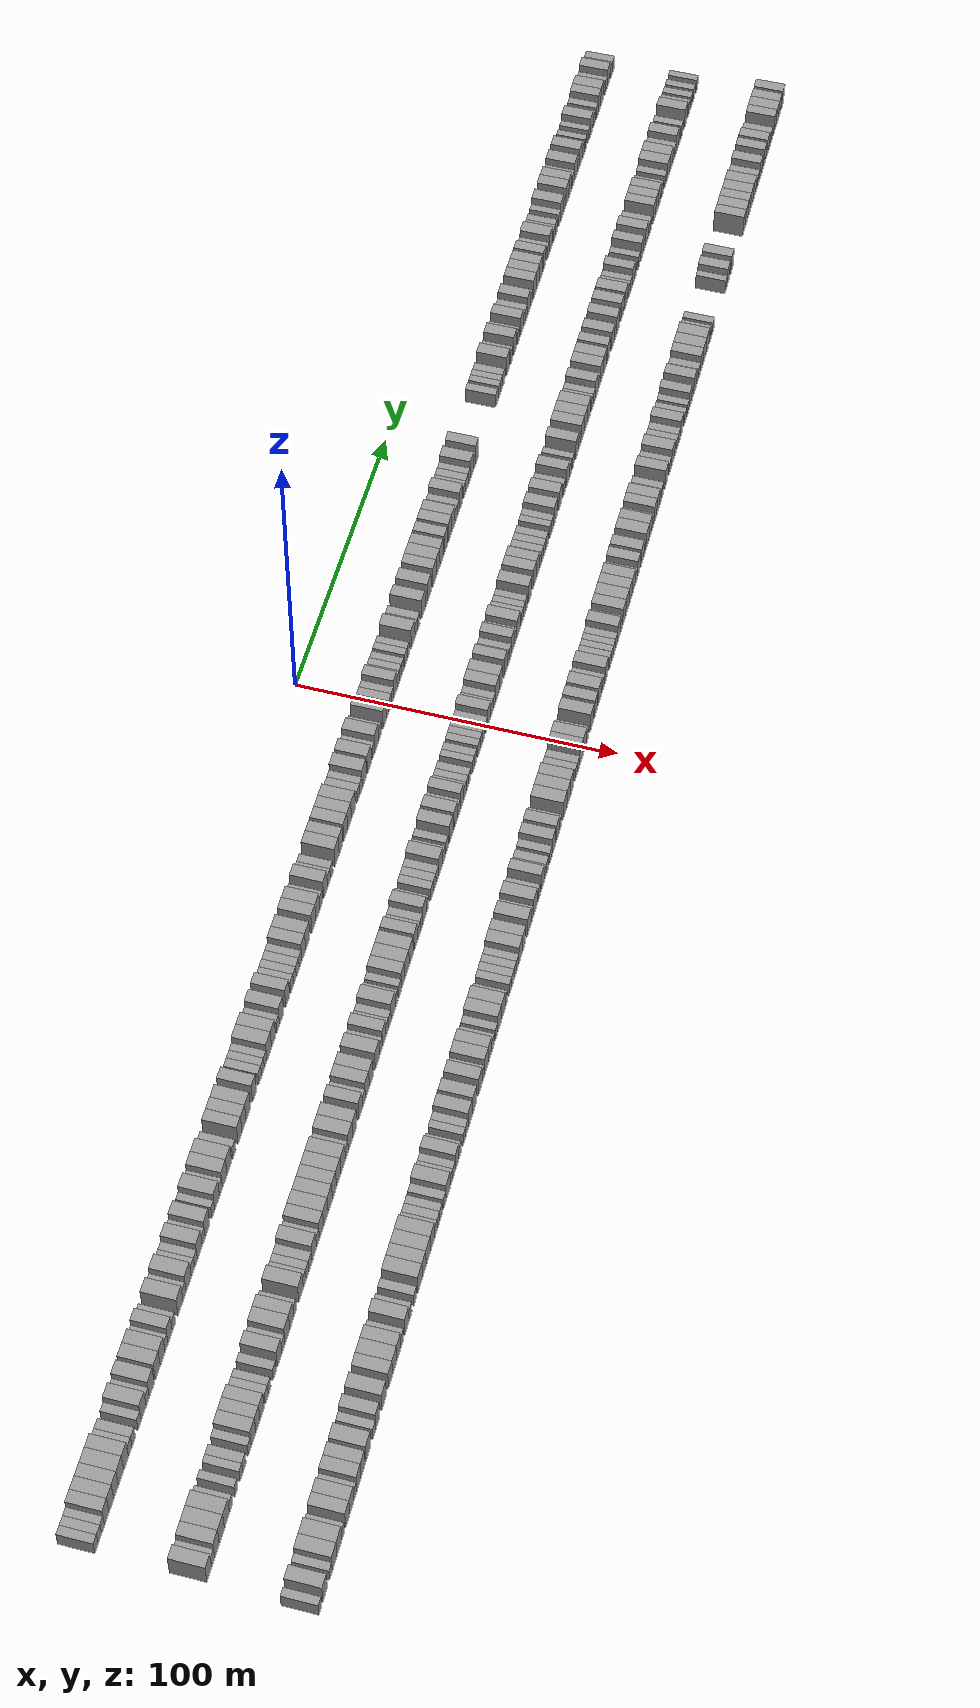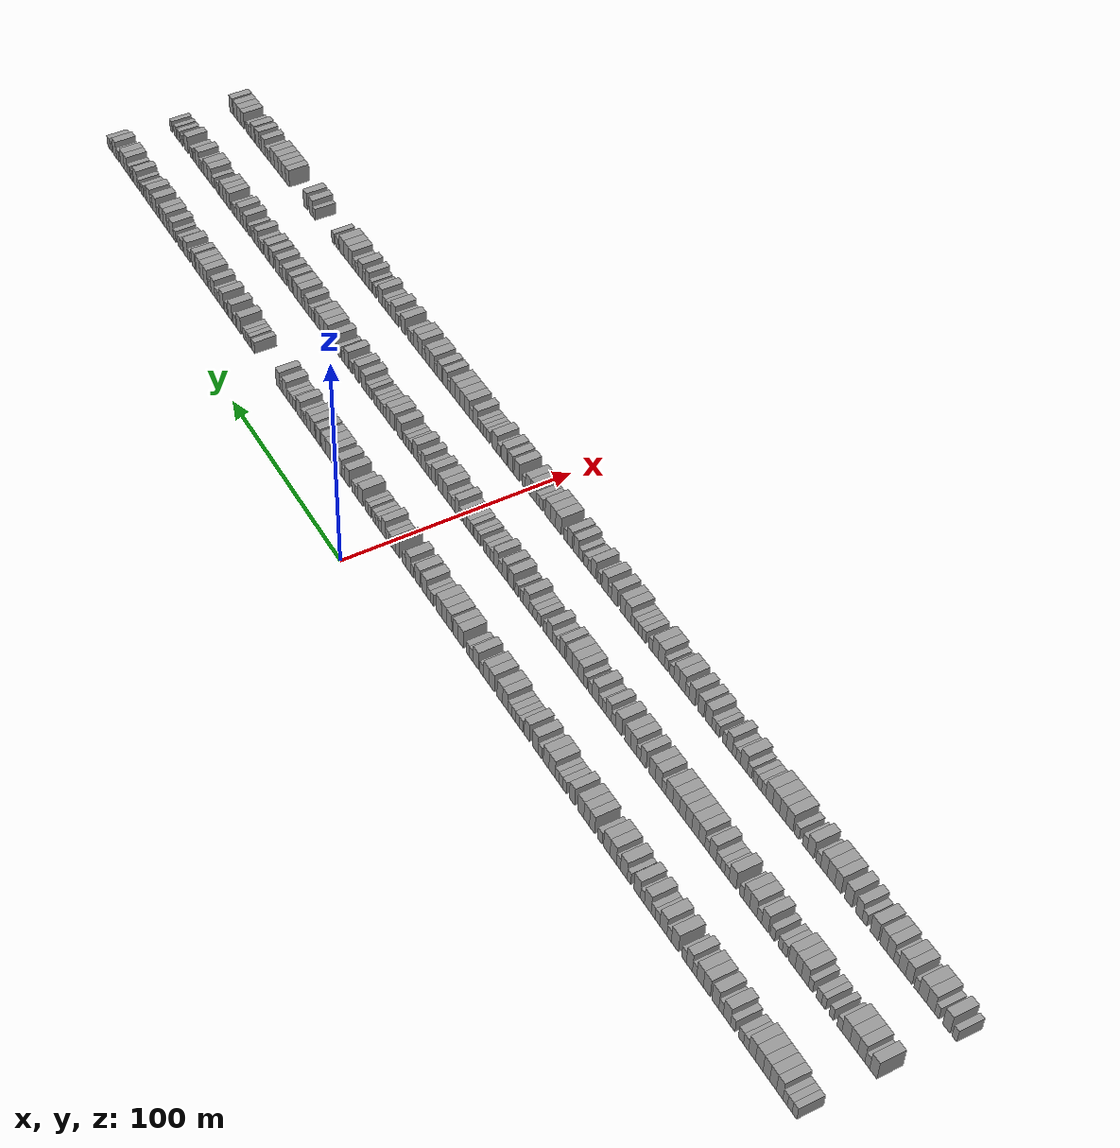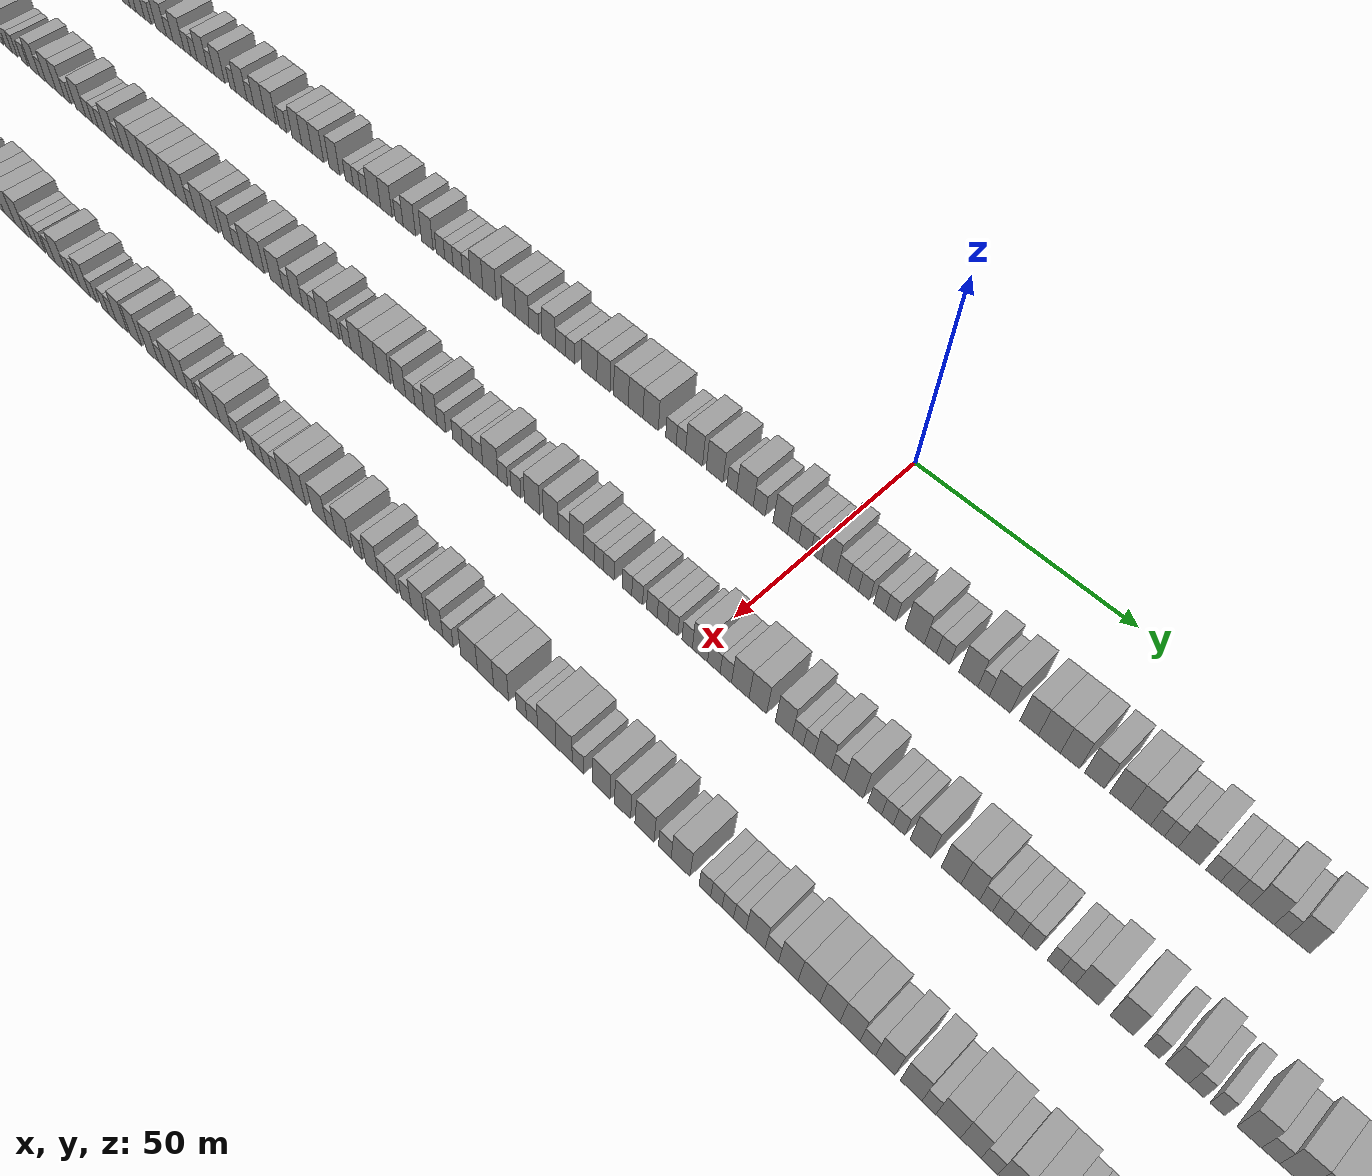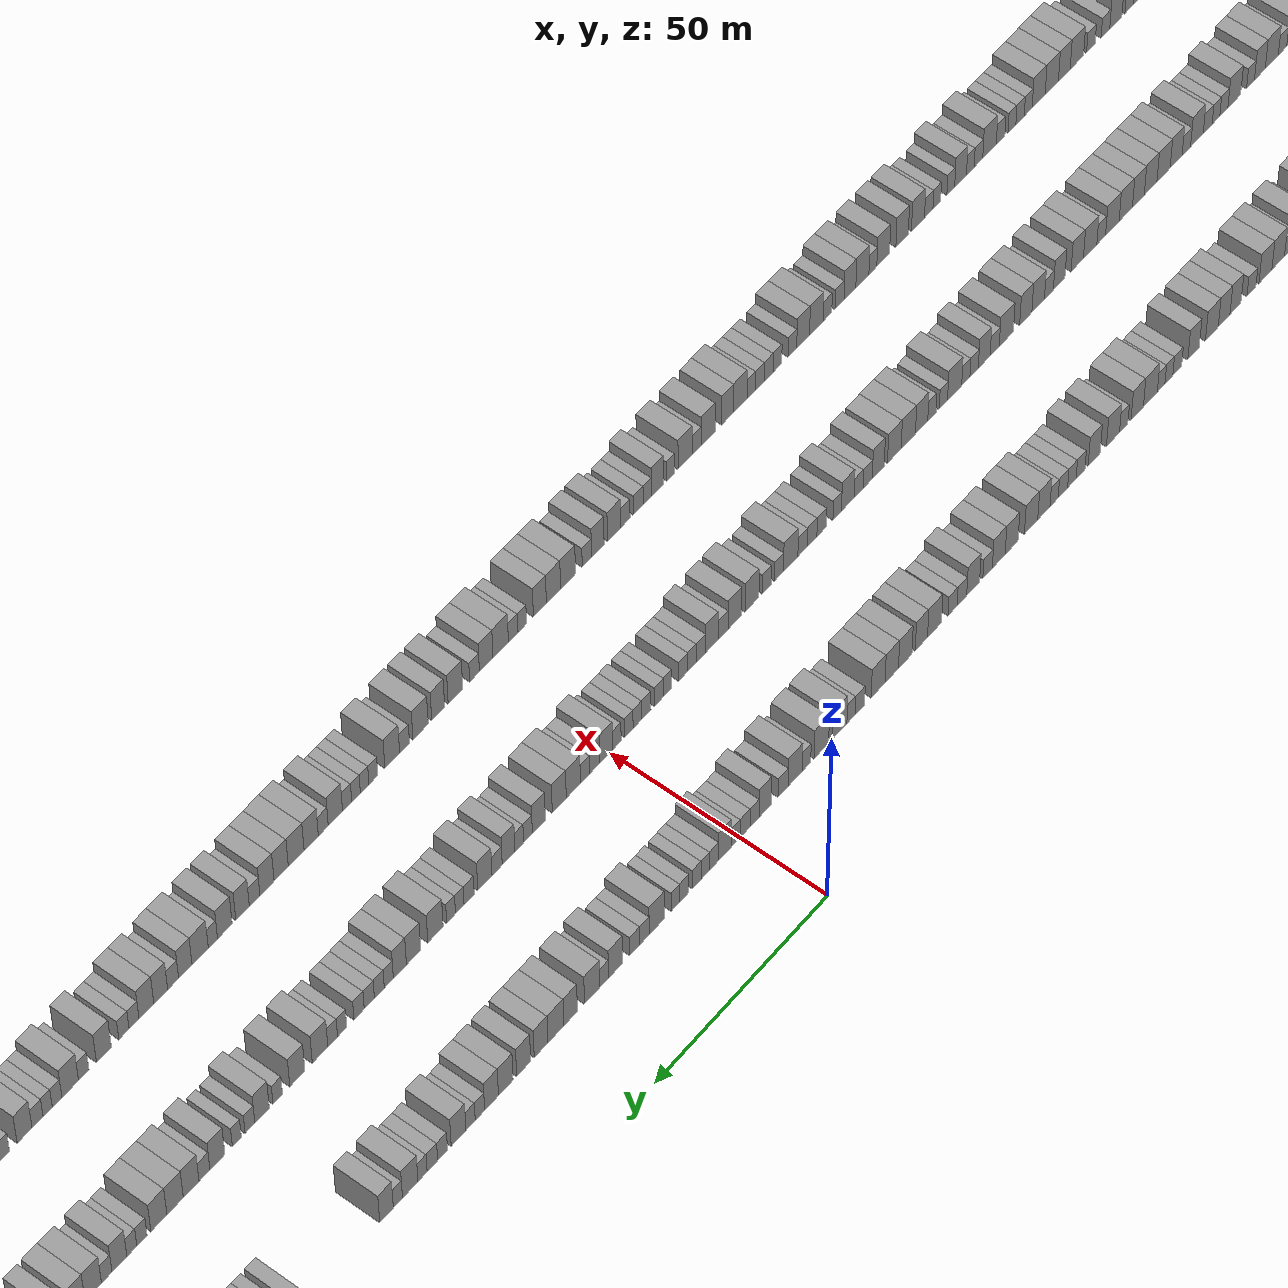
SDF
<sdf version="1.6">
 <world name="default">
  <scene>
   <sky><clouds><speed>12</speed></clouds></sky>
   <ambient>0.4 0.4 0.4 1</ambient>
   <background>0.7 0.7 0.7 1</background>
   <shadows>1</shadows>
  </scene>
  <gravity>0 0 -9.8066</gravity>
  <magnetic_field>6e-06 2.3e-05 -4.2e-05</magnetic_field>
  <physics default="0" name="default_physics" type="ode">
   <ode>
    <solver>
     <type>quick</type>
     <iters>10</iters>
     <sor>1.0</sor>
     <use_dynamic_moi_rescaling>0</use_dynamic_moi_rescaling>
    </solver>
    <constraints>
     <cfm>0</cfm>
     <erp>0.2</erp>
     <contact_max_correcting_vel>100</contact_max_correcting_vel>
     <contact_surface_layer>0.001</contact_surface_layer>
    </constraints>
   </ode>
   <max_step_size>0.004</max_step_size>
   <real_time_factor>1</real_time_factor>
   <real_time_update_rate>250</real_time_update_rate>
  </physics>
  <light name="sun" type="directional">
   <pose>0 0 10 0 0 0</pose>
   <diffuse>0.8 0.8 0.8 1</diffuse>
   <specular>0.2 0.2 0.2 1</specular>
   <attenuation>
    <range>1000</range>
    <constant>0.9</constant>
    <linear>0.01</linear>
    <quadratic>0.001</quadratic>
   </attenuation>
   <direction>-0.5 0.1 -0.9</direction>
  </light>
  <model name="building_1">
   <static>1</static>
   <pose>25.0000 -277.6752 0 0.000000 0.000000 0.000000</pose>
   <link name="link">
    <pose>0 0 3.00 0 0 0</pose>
    <collision name="collision"><geometry><box><size>10.0000 2.6495 6.0000</size></box></geometry></collision>
    <visual name="visual">
     <cast_shadows>0</cast_shadows>
     <geometry><box><size>10.0000 2.6495 6.0000</size></box></geometry>
     <material>
      <script>
       <uri>model://grey_wall/materials/scripts</uri>
       <uri>model://grey_wall/materials/textures</uri>
       <name>vrc/grey_wall</name>
      </script>
     </material>
    </visual>
   </link>
  </model>
  <model name="building_2">
   <static>1</static>
   <pose>25.0000 -274.9795 0 0.000000 0.000000 0.000000</pose>
   <link name="link">
    <pose>0 0 3.00 0 0 0</pose>
    <collision name="collision"><geometry><box><size>10.0000 2.7420 6.0000</size></box></geometry></collision>
    <visual name="visual">
     <cast_shadows>0</cast_shadows>
     <geometry><box><size>10.0000 2.7420 6.0000</size></box></geometry>
     <material>
      <script>
       <uri>model://grey_wall/materials/scripts</uri>
       <uri>model://grey_wall/materials/textures</uri>
       <name>vrc/grey_wall</name>
      </script>
     </material>
    </visual>
   </link>
  </model>
  <model name="building_3">
   <static>1</static>
   <pose>25.0000 -272.4048 0 0.000000 0.000000 0.000000</pose>
   <link name="link">
    <pose>0 0 3.00 0 0 0</pose>
    <collision name="collision"><geometry><box><size>10.0000 2.4073 6.0000</size></box></geometry></collision>
    <visual name="visual">
     <cast_shadows>0</cast_shadows>
     <geometry><box><size>10.0000 2.4073 6.0000</size></box></geometry>
     <material>
      <script>
       <uri>model://grey_wall/materials/scripts</uri>
       <uri>model://grey_wall/materials/textures</uri>
       <name>vrc/grey_wall</name>
      </script>
     </material>
    </visual>
   </link>
  </model>
  <model name="building_4">
   <static>1</static>
   <pose>25.0000 -269.3642 0 0.000000 0.000000 0.000000</pose>
   <link name="link">
    <pose>0 0 4.50 0 0 0</pose>
    <collision name="collision"><geometry><box><size>10.0000 3.6740 9.0000</size></box></geometry></collision>
    <visual name="visual">
     <cast_shadows>0</cast_shadows>
     <geometry><box><size>10.0000 3.6740 9.0000</size></box></geometry>
     <material>
      <script>
       <uri>model://grey_wall/materials/scripts</uri>
       <uri>model://grey_wall/materials/textures</uri>
       <name>vrc/grey_wall</name>
      </script>
     </material>
    </visual>
   </link>
  </model>
  <model name="building_5">
   <static>1</static>
   <pose>25.0000 -265.6011 0 0.000000 0.000000 0.000000</pose>
   <link name="link">
    <pose>0 0 4.50 0 0 0</pose>
    <collision name="collision"><geometry><box><size>10.0000 3.8522 9.0000</size></box></geometry></collision>
    <visual name="visual">
     <cast_shadows>0</cast_shadows>
     <geometry><box><size>10.0000 3.8522 9.0000</size></box></geometry>
     <material>
      <script>
       <uri>model://grey_wall/materials/scripts</uri>
       <uri>model://grey_wall/materials/textures</uri>
       <name>vrc/grey_wall</name>
      </script>
     </material>
    </visual>
   </link>
  </model>
  <model name="building_6">
   <static>1</static>
   <pose>25.0000 -261.7852 0 0.000000 0.000000 0.000000</pose>
   <link name="link">
    <pose>0 0 4.50 0 0 0</pose>
    <collision name="collision"><geometry><box><size>10.0000 3.7798 9.0000</size></box></geometry></collision>
    <visual name="visual">
     <cast_shadows>0</cast_shadows>
     <geometry><box><size>10.0000 3.7798 9.0000</size></box></geometry>
     <material>
      <script>
       <uri>model://grey_wall/materials/scripts</uri>
       <uri>model://grey_wall/materials/textures</uri>
       <name>vrc/grey_wall</name>
      </script>
     </material>
    </visual>
   </link>
  </model>
  <model name="building_7">
   <static>1</static>
   <pose>25.0000 -257.6972 0 0.000000 0.000000 0.000000</pose>
   <link name="link">
    <pose>0 0 4.50 0 0 0</pose>
    <collision name="collision"><geometry><box><size>10.0000 4.3960 9.0000</size></box></geometry></collision>
    <visual name="visual">
     <cast_shadows>0</cast_shadows>
     <geometry><box><size>10.0000 4.3960 9.0000</size></box></geometry>
     <material>
      <script>
       <uri>model://grey_wall/materials/scripts</uri>
       <uri>model://grey_wall/materials/textures</uri>
       <name>vrc/grey_wall</name>
      </script>
     </material>
    </visual>
   </link>
  </model>
  <model name="building_8">
   <static>1</static>
   <pose>25.0000 -253.5503 0 0.000000 0.000000 0.000000</pose>
   <link name="link">
    <pose>0 0 4.50 0 0 0</pose>
    <collision name="collision"><geometry><box><size>10.0000 3.8979 9.0000</size></box></geometry></collision>
    <visual name="visual">
     <cast_shadows>0</cast_shadows>
     <geometry><box><size>10.0000 3.8979 9.0000</size></box></geometry>
     <material>
      <script>
       <uri>model://grey_wall/materials/scripts</uri>
       <uri>model://grey_wall/materials/textures</uri>
       <name>vrc/grey_wall</name>
      </script>
     </material>
    </visual>
   </link>
  </model>
  <model name="building_9">
   <static>1</static>
   <pose>25.0000 -250.1390 0 0.000000 0.000000 0.000000</pose>
   <link name="link">
    <pose>0 0 3.00 0 0 0</pose>
    <collision name="collision"><geometry><box><size>10.0000 2.9247 6.0000</size></box></geometry></collision>
    <visual name="visual">
     <cast_shadows>0</cast_shadows>
     <geometry><box><size>10.0000 2.9247 6.0000</size></box></geometry>
     <material>
      <script>
       <uri>model://grey_wall/materials/scripts</uri>
       <uri>model://grey_wall/materials/textures</uri>
       <name>vrc/grey_wall</name>
      </script>
     </material>
    </visual>
   </link>
  </model>
  <model name="building_10">
   <static>1</static>
   <pose>25.0000 -247.2018 0 0.000000 0.000000 0.000000</pose>
   <link name="link">
    <pose>0 0 3.00 0 0 0</pose>
    <collision name="collision"><geometry><box><size>10.0000 2.9497 6.0000</size></box></geometry></collision>
    <visual name="visual">
     <cast_shadows>0</cast_shadows>
     <geometry><box><size>10.0000 2.9497 6.0000</size></box></geometry>
     <material>
      <script>
       <uri>model://grey_wall/materials/scripts</uri>
       <uri>model://grey_wall/materials/textures</uri>
       <name>vrc/grey_wall</name>
      </script>
     </material>
    </visual>
   </link>
  </model>
  <model name="building_11">
   <static>1</static>
   <pose>25.0000 -242.3681 0 0.000000 0.000000 0.000000</pose>
   <link name="link">
    <pose>0 0 3.00 0 0 0</pose>
    <collision name="collision"><geometry><box><size>10.0000 2.7177 6.0000</size></box></geometry></collision>
    <visual name="visual">
     <cast_shadows>0</cast_shadows>
     <geometry><box><size>10.0000 2.7177 6.0000</size></box></geometry>
     <material>
      <script>
       <uri>model://grey_wall/materials/scripts</uri>
       <uri>model://grey_wall/materials/textures</uri>
       <name>vrc/grey_wall</name>
      </script>
     </material>
    </visual>
   </link>
  </model>
  <model name="building_12">
   <static>1</static>
   <pose>25.0000 -238.8807 0 0.000000 0.000000 0.000000</pose>
   <link name="link">
    <pose>0 0 4.50 0 0 0</pose>
    <collision name="collision"><geometry><box><size>10.0000 4.2572 9.0000</size></box></geometry></collision>
    <visual name="visual">
     <cast_shadows>0</cast_shadows>
     <geometry><box><size>10.0000 4.2572 9.0000</size></box></geometry>
     <material>
      <script>
       <uri>model://grey_wall/materials/scripts</uri>
       <uri>model://grey_wall/materials/textures</uri>
       <name>vrc/grey_wall</name>
      </script>
     </material>
    </visual>
   </link>
  </model>
  <model name="building_13">
   <static>1</static>
   <pose>25.0000 -235.4139 0 0.000000 0.000000 0.000000</pose>
   <link name="link">
    <pose>0 0 3.00 0 0 0</pose>
    <collision name="collision"><geometry><box><size>10.0000 2.6763 6.0000</size></box></geometry></collision>
    <visual name="visual">
     <cast_shadows>0</cast_shadows>
     <geometry><box><size>10.0000 2.6763 6.0000</size></box></geometry>
     <material>
      <script>
       <uri>model://grey_wall/materials/scripts</uri>
       <uri>model://grey_wall/materials/textures</uri>
       <name>vrc/grey_wall</name>
      </script>
     </material>
    </visual>
   </link>
  </model>
  <model name="building_14">
   <static>1</static>
   <pose>25.0000 -232.0247 0 0.000000 0.000000 0.000000</pose>
   <link name="link">
    <pose>0 0 4.50 0 0 0</pose>
    <collision name="collision"><geometry><box><size>10.0000 4.1022 9.0000</size></box></geometry></collision>
    <visual name="visual">
     <cast_shadows>0</cast_shadows>
     <geometry><box><size>10.0000 4.1022 9.0000</size></box></geometry>
     <material>
      <script>
       <uri>model://grey_wall/materials/scripts</uri>
       <uri>model://grey_wall/materials/textures</uri>
       <name>vrc/grey_wall</name>
      </script>
     </material>
    </visual>
   </link>
  </model>
  <model name="building_15">
   <static>1</static>
   <pose>25.0000 -226.8983 0 0.000000 0.000000 0.000000</pose>
   <link name="link">
    <pose>0 0 4.50 0 0 0</pose>
    <collision name="collision"><geometry><box><size>10.0000 4.1507 9.0000</size></box></geometry></collision>
    <visual name="visual">
     <cast_shadows>0</cast_shadows>
     <geometry><box><size>10.0000 4.1507 9.0000</size></box></geometry>
     <material>
      <script>
       <uri>model://grey_wall/materials/scripts</uri>
       <uri>model://grey_wall/materials/textures</uri>
       <name>vrc/grey_wall</name>
      </script>
     </material>
    </visual>
   </link>
  </model>
  <model name="building_16">
   <static>1</static>
   <pose>25.0000 -222.7742 0 0.000000 0.000000 0.000000</pose>
   <link name="link">
    <pose>0 0 4.50 0 0 0</pose>
    <collision name="collision"><geometry><box><size>10.0000 4.0976 9.0000</size></box></geometry></collision>
    <visual name="visual">
     <cast_shadows>0</cast_shadows>
     <geometry><box><size>10.0000 4.0976 9.0000</size></box></geometry>
     <material>
      <script>
       <uri>model://grey_wall/materials/scripts</uri>
       <uri>model://grey_wall/materials/textures</uri>
       <name>vrc/grey_wall</name>
      </script>
     </material>
    </visual>
   </link>
  </model>
  <model name="building_17">
   <static>1</static>
   <pose>25.0000 -219.4389 0 0.000000 0.000000 0.000000</pose>
   <link name="link">
    <pose>0 0 3.00 0 0 0</pose>
    <collision name="collision"><geometry><box><size>10.0000 2.5729 6.0000</size></box></geometry></collision>
    <visual name="visual">
     <cast_shadows>0</cast_shadows>
     <geometry><box><size>10.0000 2.5729 6.0000</size></box></geometry>
     <material>
      <script>
       <uri>model://grey_wall/materials/scripts</uri>
       <uri>model://grey_wall/materials/textures</uri>
       <name>vrc/grey_wall</name>
      </script>
     </material>
    </visual>
   </link>
  </model>
  <model name="building_18">
   <static>1</static>
   <pose>25.0000 -216.3109 0 0.000000 0.000000 0.000000</pose>
   <link name="link">
    <pose>0 0 4.50 0 0 0</pose>
    <collision name="collision"><geometry><box><size>10.0000 3.6831 9.0000</size></box></geometry></collision>
    <visual name="visual">
     <cast_shadows>0</cast_shadows>
     <geometry><box><size>10.0000 3.6831 9.0000</size></box></geometry>
     <material>
      <script>
       <uri>model://grey_wall/materials/scripts</uri>
       <uri>model://grey_wall/materials/textures</uri>
       <name>vrc/grey_wall</name>
      </script>
     </material>
    </visual>
   </link>
  </model>
  <model name="building_19">
   <static>1</static>
   <pose>25.0000 -213.0263 0 0.000000 0.000000 0.000000</pose>
   <link name="link">
    <pose>0 0 3.00 0 0 0</pose>
    <collision name="collision"><geometry><box><size>10.0000 2.8860 6.0000</size></box></geometry></collision>
    <visual name="visual">
     <cast_shadows>0</cast_shadows>
     <geometry><box><size>10.0000 2.8860 6.0000</size></box></geometry>
     <material>
      <script>
       <uri>model://grey_wall/materials/scripts</uri>
       <uri>model://grey_wall/materials/textures</uri>
       <name>vrc/grey_wall</name>
      </script>
     </material>
    </visual>
   </link>
  </model>
  <model name="building_20">
   <static>1</static>
   <pose>25.0000 -207.3724 0 0.000000 0.000000 0.000000</pose>
   <link name="link">
    <pose>0 0 4.50 0 0 0</pose>
    <collision name="collision"><geometry><box><size>10.0000 4.4217 9.0000</size></box></geometry></collision>
    <visual name="visual">
     <cast_shadows>0</cast_shadows>
     <geometry><box><size>10.0000 4.4217 9.0000</size></box></geometry>
     <material>
      <script>
       <uri>model://grey_wall/materials/scripts</uri>
       <uri>model://grey_wall/materials/textures</uri>
       <name>vrc/grey_wall</name>
      </script>
     </material>
    </visual>
   </link>
  </model>
  <model name="building_21">
   <static>1</static>
   <pose>25.0000 -203.7728 0 0.000000 0.000000 0.000000</pose>
   <link name="link">
    <pose>0 0 3.00 0 0 0</pose>
    <collision name="collision"><geometry><box><size>10.0000 2.7775 6.0000</size></box></geometry></collision>
    <visual name="visual">
     <cast_shadows>0</cast_shadows>
     <geometry><box><size>10.0000 2.7775 6.0000</size></box></geometry>
     <material>
      <script>
       <uri>model://grey_wall/materials/scripts</uri>
       <uri>model://grey_wall/materials/textures</uri>
       <name>vrc/grey_wall</name>
      </script>
     </material>
    </visual>
   </link>
  </model>
  <model name="building_22">
   <static>1</static>
   <pose>25.0000 -200.1363 0 0.000000 0.000000 0.000000</pose>
   <link name="link">
    <pose>0 0 4.50 0 0 0</pose>
    <collision name="collision"><geometry><box><size>10.0000 4.4956 9.0000</size></box></geometry></collision>
    <visual name="visual">
     <cast_shadows>0</cast_shadows>
     <geometry><box><size>10.0000 4.4956 9.0000</size></box></geometry>
     <material>
      <script>
       <uri>model://grey_wall/materials/scripts</uri>
       <uri>model://grey_wall/materials/textures</uri>
       <name>vrc/grey_wall</name>
      </script>
     </material>
    </visual>
   </link>
  </model>
  <model name="building_23">
   <static>1</static>
   <pose>25.0000 -196.4032 0 0.000000 0.000000 0.000000</pose>
   <link name="link">
    <pose>0 0 3.00 0 0 0</pose>
    <collision name="collision"><geometry><box><size>10.0000 2.9708 6.0000</size></box></geometry></collision>
    <visual name="visual">
     <cast_shadows>0</cast_shadows>
     <geometry><box><size>10.0000 2.9708 6.0000</size></box></geometry>
     <material>
      <script>
       <uri>model://grey_wall/materials/scripts</uri>
       <uri>model://grey_wall/materials/textures</uri>
       <name>vrc/grey_wall</name>
      </script>
     </material>
    </visual>
   </link>
  </model>
  <model name="building_24">
   <static>1</static>
   <pose>25.0000 -193.6573 0 0.000000 0.000000 0.000000</pose>
   <link name="link">
    <pose>0 0 3.00 0 0 0</pose>
    <collision name="collision"><geometry><box><size>10.0000 2.5210 6.0000</size></box></geometry></collision>
    <visual name="visual">
     <cast_shadows>0</cast_shadows>
     <geometry><box><size>10.0000 2.5210 6.0000</size></box></geometry>
     <material>
      <script>
       <uri>model://grey_wall/materials/scripts</uri>
       <uri>model://grey_wall/materials/textures</uri>
       <name>vrc/grey_wall</name>
      </script>
     </material>
    </visual>
   </link>
  </model>
  <model name="building_25">
   <static>1</static>
   <pose>25.0000 -190.2645 0 0.000000 0.000000 0.000000</pose>
   <link name="link">
    <pose>0 0 4.50 0 0 0</pose>
    <collision name="collision"><geometry><box><size>10.0000 4.2645 9.0000</size></box></geometry></collision>
    <visual name="visual">
     <cast_shadows>0</cast_shadows>
     <geometry><box><size>10.0000 4.2645 9.0000</size></box></geometry>
     <material>
      <script>
       <uri>model://grey_wall/materials/scripts</uri>
       <uri>model://grey_wall/materials/textures</uri>
       <name>vrc/grey_wall</name>
      </script>
     </material>
    </visual>
   </link>
  </model>
  <model name="building_26">
   <static>1</static>
   <pose>25.0000 -186.8077 0 0.000000 0.000000 0.000000</pose>
   <link name="link">
    <pose>0 0 3.00 0 0 0</pose>
    <collision name="collision"><geometry><box><size>10.0000 2.6490 6.0000</size></box></geometry></collision>
    <visual name="visual">
     <cast_shadows>0</cast_shadows>
     <geometry><box><size>10.0000 2.6490 6.0000</size></box></geometry>
     <material>
      <script>
       <uri>model://grey_wall/materials/scripts</uri>
       <uri>model://grey_wall/materials/textures</uri>
       <name>vrc/grey_wall</name>
      </script>
     </material>
    </visual>
   </link>
  </model>
  <model name="building_27">
   <static>1</static>
   <pose>25.0000 -183.4079 0 0.000000 0.000000 0.000000</pose>
   <link name="link">
    <pose>0 0 4.50 0 0 0</pose>
    <collision name="collision"><geometry><box><size>10.0000 4.1506 9.0000</size></box></geometry></collision>
    <visual name="visual">
     <cast_shadows>0</cast_shadows>
     <geometry><box><size>10.0000 4.1506 9.0000</size></box></geometry>
     <material>
      <script>
       <uri>model://grey_wall/materials/scripts</uri>
       <uri>model://grey_wall/materials/textures</uri>
       <name>vrc/grey_wall</name>
      </script>
     </material>
    </visual>
   </link>
  </model>
  <model name="building_28">
   <static>1</static>
   <pose>25.0000 -178.1319 0 0.000000 0.000000 0.000000</pose>
   <link name="link">
    <pose>0 0 3.00 0 0 0</pose>
    <collision name="collision"><geometry><box><size>10.0000 2.4013 6.0000</size></box></geometry></collision>
    <visual name="visual">
     <cast_shadows>0</cast_shadows>
     <geometry><box><size>10.0000 2.4013 6.0000</size></box></geometry>
     <material>
      <script>
       <uri>model://grey_wall/materials/scripts</uri>
       <uri>model://grey_wall/materials/textures</uri>
       <name>vrc/grey_wall</name>
      </script>
     </material>
    </visual>
   </link>
  </model>
  <model name="building_29">
   <static>1</static>
   <pose>25.0000 -174.7251 0 0.000000 0.000000 0.000000</pose>
   <link name="link">
    <pose>0 0 4.50 0 0 0</pose>
    <collision name="collision"><geometry><box><size>10.0000 4.4124 9.0000</size></box></geometry></collision>
    <visual name="visual">
     <cast_shadows>0</cast_shadows>
     <geometry><box><size>10.0000 4.4124 9.0000</size></box></geometry>
     <material>
      <script>
       <uri>model://grey_wall/materials/scripts</uri>
       <uri>model://grey_wall/materials/textures</uri>
       <name>vrc/grey_wall</name>
      </script>
     </material>
    </visual>
   </link>
  </model>
  <model name="building_30">
   <static>1</static>
   <pose>25.0000 -171.2000 0 0.000000 0.000000 0.000000</pose>
   <link name="link">
    <pose>0 0 3.00 0 0 0</pose>
    <collision name="collision"><geometry><box><size>10.0000 2.6376 6.0000</size></box></geometry></collision>
    <visual name="visual">
     <cast_shadows>0</cast_shadows>
     <geometry><box><size>10.0000 2.6376 6.0000</size></box></geometry>
     <material>
      <script>
       <uri>model://grey_wall/materials/scripts</uri>
       <uri>model://grey_wall/materials/textures</uri>
       <name>vrc/grey_wall</name>
      </script>
     </material>
    </visual>
   </link>
  </model>
  <model name="building_31">
   <static>1</static>
   <pose>25.0000 -167.7808 0 0.000000 0.000000 0.000000</pose>
   <link name="link">
    <pose>0 0 4.50 0 0 0</pose>
    <collision name="collision"><geometry><box><size>10.0000 4.2008 9.0000</size></box></geometry></collision>
    <visual name="visual">
     <cast_shadows>0</cast_shadows>
     <geometry><box><size>10.0000 4.2008 9.0000</size></box></geometry>
     <material>
      <script>
       <uri>model://grey_wall/materials/scripts</uri>
       <uri>model://grey_wall/materials/textures</uri>
       <name>vrc/grey_wall</name>
      </script>
     </material>
    </visual>
   </link>
  </model>
  <model name="building_32">
   <static>1</static>
   <pose>25.0000 -163.5349 0 0.000000 0.000000 0.000000</pose>
   <link name="link">
    <pose>0 0 4.50 0 0 0</pose>
    <collision name="collision"><geometry><box><size>10.0000 4.2909 9.0000</size></box></geometry></collision>
    <visual name="visual">
     <cast_shadows>0</cast_shadows>
     <geometry><box><size>10.0000 4.2909 9.0000</size></box></geometry>
     <material>
      <script>
       <uri>model://grey_wall/materials/scripts</uri>
       <uri>model://grey_wall/materials/textures</uri>
       <name>vrc/grey_wall</name>
      </script>
     </material>
    </visual>
   </link>
  </model>
  <model name="building_33">
   <static>1</static>
   <pose>25.0000 -158.9349 0 0.000000 0.000000 0.000000</pose>
   <link name="link">
    <pose>0 0 3.00 0 0 0</pose>
    <collision name="collision"><geometry><box><size>10.0000 2.9093 6.0000</size></box></geometry></collision>
    <visual name="visual">
     <cast_shadows>0</cast_shadows>
     <geometry><box><size>10.0000 2.9093 6.0000</size></box></geometry>
     <material>
      <script>
       <uri>model://grey_wall/materials/scripts</uri>
       <uri>model://grey_wall/materials/textures</uri>
       <name>vrc/grey_wall</name>
      </script>
     </material>
    </visual>
   </link>
  </model>
  <model name="building_34">
   <static>1</static>
   <pose>25.0000 -153.6737 0 0.000000 0.000000 0.000000</pose>
   <link name="link">
    <pose>0 0 4.50 0 0 0</pose>
    <collision name="collision"><geometry><box><size>10.0000 3.6130 9.0000</size></box></geometry></collision>
    <visual name="visual">
     <cast_shadows>0</cast_shadows>
     <geometry><box><size>10.0000 3.6130 9.0000</size></box></geometry>
     <material>
      <script>
       <uri>model://grey_wall/materials/scripts</uri>
       <uri>model://grey_wall/materials/textures</uri>
       <name>vrc/grey_wall</name>
      </script>
     </material>
    </visual>
   </link>
  </model>
  <model name="building_35">
   <static>1</static>
   <pose>25.0000 -149.9501 0 0.000000 0.000000 0.000000</pose>
   <link name="link">
    <pose>0 0 4.50 0 0 0</pose>
    <collision name="collision"><geometry><box><size>10.0000 3.8343 9.0000</size></box></geometry></collision>
    <visual name="visual">
     <cast_shadows>0</cast_shadows>
     <geometry><box><size>10.0000 3.8343 9.0000</size></box></geometry>
     <material>
      <script>
       <uri>model://grey_wall/materials/scripts</uri>
       <uri>model://grey_wall/materials/textures</uri>
       <name>vrc/grey_wall</name>
      </script>
     </material>
    </visual>
   </link>
  </model>
  <model name="building_36">
   <static>1</static>
   <pose>25.0000 -145.9437 0 0.000000 0.000000 0.000000</pose>
   <link name="link">
    <pose>0 0 4.50 0 0 0</pose>
    <collision name="collision"><geometry><box><size>10.0000 4.1787 9.0000</size></box></geometry></collision>
    <visual name="visual">
     <cast_shadows>0</cast_shadows>
     <geometry><box><size>10.0000 4.1787 9.0000</size></box></geometry>
     <material>
      <script>
       <uri>model://grey_wall/materials/scripts</uri>
       <uri>model://grey_wall/materials/textures</uri>
       <name>vrc/grey_wall</name>
      </script>
     </material>
    </visual>
   </link>
  </model>
  <model name="building_37">
   <static>1</static>
   <pose>25.0000 -139.9916 0 0.000000 0.000000 0.000000</pose>
   <link name="link">
    <pose>0 0 4.50 0 0 0</pose>
    <collision name="collision"><geometry><box><size>10.0000 3.7255 9.0000</size></box></geometry></collision>
    <visual name="visual">
     <cast_shadows>0</cast_shadows>
     <geometry><box><size>10.0000 3.7255 9.0000</size></box></geometry>
     <material>
      <script>
       <uri>model://grey_wall/materials/scripts</uri>
       <uri>model://grey_wall/materials/textures</uri>
       <name>vrc/grey_wall</name>
      </script>
     </material>
    </visual>
   </link>
  </model>
  <model name="building_38">
   <static>1</static>
   <pose>25.0000 -134.7000 0 0.000000 0.000000 0.000000</pose>
   <link name="link">
    <pose>0 0 3.00 0 0 0</pose>
    <collision name="collision"><geometry><box><size>10.0000 2.8577 6.0000</size></box></geometry></collision>
    <visual name="visual">
     <cast_shadows>0</cast_shadows>
     <geometry><box><size>10.0000 2.8577 6.0000</size></box></geometry>
     <material>
      <script>
       <uri>model://grey_wall/materials/scripts</uri>
       <uri>model://grey_wall/materials/textures</uri>
       <name>vrc/grey_wall</name>
      </script>
     </material>
    </visual>
   </link>
  </model>
  <model name="building_39">
   <static>1</static>
   <pose>25.0000 -131.9935 0 0.000000 0.000000 0.000000</pose>
   <link name="link">
    <pose>0 0 3.00 0 0 0</pose>
    <collision name="collision"><geometry><box><size>10.0000 2.5553 6.0000</size></box></geometry></collision>
    <visual name="visual">
     <cast_shadows>0</cast_shadows>
     <geometry><box><size>10.0000 2.5553 6.0000</size></box></geometry>
     <material>
      <script>
       <uri>model://grey_wall/materials/scripts</uri>
       <uri>model://grey_wall/materials/textures</uri>
       <name>vrc/grey_wall</name>
      </script>
     </material>
    </visual>
   </link>
  </model>
  <model name="building_40">
   <static>1</static>
   <pose>25.0000 -129.4904 0 0.000000 0.000000 0.000000</pose>
   <link name="link">
    <pose>0 0 3.00 0 0 0</pose>
    <collision name="collision"><geometry><box><size>10.0000 2.4510 6.0000</size></box></geometry></collision>
    <visual name="visual">
     <cast_shadows>0</cast_shadows>
     <geometry><box><size>10.0000 2.4510 6.0000</size></box></geometry>
     <material>
      <script>
       <uri>model://grey_wall/materials/scripts</uri>
       <uri>model://grey_wall/materials/textures</uri>
       <name>vrc/grey_wall</name>
      </script>
     </material>
    </visual>
   </link>
  </model>
  <model name="building_41">
   <static>1</static>
   <pose>25.0000 -126.0280 0 0.000000 0.000000 0.000000</pose>
   <link name="link">
    <pose>0 0 4.50 0 0 0</pose>
    <collision name="collision"><geometry><box><size>10.0000 4.4737 9.0000</size></box></geometry></collision>
    <visual name="visual">
     <cast_shadows>0</cast_shadows>
     <geometry><box><size>10.0000 4.4737 9.0000</size></box></geometry>
     <material>
      <script>
       <uri>model://grey_wall/materials/scripts</uri>
       <uri>model://grey_wall/materials/textures</uri>
       <name>vrc/grey_wall</name>
      </script>
     </material>
    </visual>
   </link>
  </model>
  <model name="building_42">
   <static>1</static>
   <pose>25.0000 -121.8029 0 0.000000 0.000000 0.000000</pose>
   <link name="link">
    <pose>0 0 4.50 0 0 0</pose>
    <collision name="collision"><geometry><box><size>10.0000 3.9766 9.0000</size></box></geometry></collision>
    <visual name="visual">
     <cast_shadows>0</cast_shadows>
     <geometry><box><size>10.0000 3.9766 9.0000</size></box></geometry>
     <material>
      <script>
       <uri>model://grey_wall/materials/scripts</uri>
       <uri>model://grey_wall/materials/textures</uri>
       <name>vrc/grey_wall</name>
      </script>
     </material>
    </visual>
   </link>
  </model>
  <model name="building_43">
   <static>1</static>
   <pose>25.0000 -117.4741 0 0.000000 0.000000 0.000000</pose>
   <link name="link">
    <pose>0 0 3.00 0 0 0</pose>
    <collision name="collision"><geometry><box><size>10.0000 2.6810 6.0000</size></box></geometry></collision>
    <visual name="visual">
     <cast_shadows>0</cast_shadows>
     <geometry><box><size>10.0000 2.6810 6.0000</size></box></geometry>
     <material>
      <script>
       <uri>model://grey_wall/materials/scripts</uri>
       <uri>model://grey_wall/materials/textures</uri>
       <name>vrc/grey_wall</name>
      </script>
     </material>
    </visual>
   </link>
  </model>
  <model name="building_44">
   <static>1</static>
   <pose>25.0000 -114.0489 0 0.000000 0.000000 0.000000</pose>
   <link name="link">
    <pose>0 0 4.50 0 0 0</pose>
    <collision name="collision"><geometry><box><size>10.0000 4.1696 9.0000</size></box></geometry></collision>
    <visual name="visual">
     <cast_shadows>0</cast_shadows>
     <geometry><box><size>10.0000 4.1696 9.0000</size></box></geometry>
     <material>
      <script>
       <uri>model://grey_wall/materials/scripts</uri>
       <uri>model://grey_wall/materials/textures</uri>
       <name>vrc/grey_wall</name>
      </script>
     </material>
    </visual>
   </link>
  </model>
  <model name="building_45">
   <static>1</static>
   <pose>25.0000 -108.0677 0 0.000000 0.000000 0.000000</pose>
   <link name="link">
    <pose>0 0 4.50 0 0 0</pose>
    <collision name="collision"><geometry><box><size>10.0000 3.7928 9.0000</size></box></geometry></collision>
    <visual name="visual">
     <cast_shadows>0</cast_shadows>
     <geometry><box><size>10.0000 3.7928 9.0000</size></box></geometry>
     <material>
      <script>
       <uri>model://grey_wall/materials/scripts</uri>
       <uri>model://grey_wall/materials/textures</uri>
       <name>vrc/grey_wall</name>
      </script>
     </material>
    </visual>
   </link>
  </model>
  <model name="building_46">
   <static>1</static>
   <pose>25.0000 -103.7559 0 0.000000 0.000000 0.000000</pose>
   <link name="link">
    <pose>0 0 3.00 0 0 0</pose>
    <collision name="collision"><geometry><box><size>10.0000 2.8308 6.0000</size></box></geometry></collision>
    <visual name="visual">
     <cast_shadows>0</cast_shadows>
     <geometry><box><size>10.0000 2.8308 6.0000</size></box></geometry>
     <material>
      <script>
       <uri>model://grey_wall/materials/scripts</uri>
       <uri>model://grey_wall/materials/textures</uri>
       <name>vrc/grey_wall</name>
      </script>
     </material>
    </visual>
   </link>
  </model>
  <model name="building_47">
   <static>1</static>
   <pose>25.0000 -101.0030 0 0.000000 0.000000 0.000000</pose>
   <link name="link">
    <pose>0 0 3.00 0 0 0</pose>
    <collision name="collision"><geometry><box><size>10.0000 2.6751 6.0000</size></box></geometry></collision>
    <visual name="visual">
     <cast_shadows>0</cast_shadows>
     <geometry><box><size>10.0000 2.6751 6.0000</size></box></geometry>
     <material>
      <script>
       <uri>model://grey_wall/materials/scripts</uri>
       <uri>model://grey_wall/materials/textures</uri>
       <name>vrc/grey_wall</name>
      </script>
     </material>
    </visual>
   </link>
  </model>
  <model name="building_48">
   <static>1</static>
   <pose>25.0000 -98.1678 0 0.000000 0.000000 0.000000</pose>
   <link name="link">
    <pose>0 0 3.00 0 0 0</pose>
    <collision name="collision"><geometry><box><size>10.0000 2.9954 6.0000</size></box></geometry></collision>
    <visual name="visual">
     <cast_shadows>0</cast_shadows>
     <geometry><box><size>10.0000 2.9954 6.0000</size></box></geometry>
     <material>
      <script>
       <uri>model://grey_wall/materials/scripts</uri>
       <uri>model://grey_wall/materials/textures</uri>
       <name>vrc/grey_wall</name>
      </script>
     </material>
    </visual>
   </link>
  </model>
  <model name="building_49">
   <static>1</static>
   <pose>25.0000 -95.3936 0 0.000000 0.000000 0.000000</pose>
   <link name="link">
    <pose>0 0 3.00 0 0 0</pose>
    <collision name="collision"><geometry><box><size>10.0000 2.5530 6.0000</size></box></geometry></collision>
    <visual name="visual">
     <cast_shadows>0</cast_shadows>
     <geometry><box><size>10.0000 2.5530 6.0000</size></box></geometry>
     <material>
      <script>
       <uri>model://grey_wall/materials/scripts</uri>
       <uri>model://grey_wall/materials/textures</uri>
       <name>vrc/grey_wall</name>
      </script>
     </material>
    </visual>
   </link>
  </model>
  <model name="building_50">
   <static>1</static>
   <pose>25.0000 -92.1863 0 0.000000 0.000000 0.000000</pose>
   <link name="link">
    <pose>0 0 4.50 0 0 0</pose>
    <collision name="collision"><geometry><box><size>10.0000 3.8615 9.0000</size></box></geometry></collision>
    <visual name="visual">
     <cast_shadows>0</cast_shadows>
     <geometry><box><size>10.0000 3.8615 9.0000</size></box></geometry>
     <material>
      <script>
       <uri>model://grey_wall/materials/scripts</uri>
       <uri>model://grey_wall/materials/textures</uri>
       <name>vrc/grey_wall</name>
      </script>
     </material>
    </visual>
   </link>
  </model>
  <model name="building_51">
   <static>1</static>
   <pose>25.0000 -88.1677 0 0.000000 0.000000 0.000000</pose>
   <link name="link">
    <pose>0 0 4.50 0 0 0</pose>
    <collision name="collision"><geometry><box><size>10.0000 4.1758 9.0000</size></box></geometry></collision>
    <visual name="visual">
     <cast_shadows>0</cast_shadows>
     <geometry><box><size>10.0000 4.1758 9.0000</size></box></geometry>
     <material>
      <script>
       <uri>model://grey_wall/materials/scripts</uri>
       <uri>model://grey_wall/materials/textures</uri>
       <name>vrc/grey_wall</name>
      </script>
     </material>
    </visual>
   </link>
  </model>
  <model name="building_52">
   <static>1</static>
   <pose>25.0000 -82.0708 0 0.000000 0.000000 0.000000</pose>
   <link name="link">
    <pose>0 0 4.50 0 0 0</pose>
    <collision name="collision"><geometry><box><size>10.0000 4.0179 9.0000</size></box></geometry></collision>
    <visual name="visual">
     <cast_shadows>0</cast_shadows>
     <geometry><box><size>10.0000 4.0179 9.0000</size></box></geometry>
     <material>
      <script>
       <uri>model://grey_wall/materials/scripts</uri>
       <uri>model://grey_wall/materials/textures</uri>
       <name>vrc/grey_wall</name>
      </script>
     </material>
    </visual>
   </link>
  </model>
  <model name="building_53">
   <static>1</static>
   <pose>25.0000 -78.0774 0 0.000000 0.000000 0.000000</pose>
   <link name="link">
    <pose>0 0 4.50 0 0 0</pose>
    <collision name="collision"><geometry><box><size>10.0000 3.9689 9.0000</size></box></geometry></collision>
    <visual name="visual">
     <cast_shadows>0</cast_shadows>
     <geometry><box><size>10.0000 3.9689 9.0000</size></box></geometry>
     <material>
      <script>
       <uri>model://grey_wall/materials/scripts</uri>
       <uri>model://grey_wall/materials/textures</uri>
       <name>vrc/grey_wall</name>
      </script>
     </material>
    </visual>
   </link>
  </model>
  <model name="building_54">
   <static>1</static>
   <pose>25.0000 -74.6206 0 0.000000 0.000000 0.000000</pose>
   <link name="link">
    <pose>0 0 3.00 0 0 0</pose>
    <collision name="collision"><geometry><box><size>10.0000 2.9447 6.0000</size></box></geometry></collision>
    <visual name="visual">
     <cast_shadows>0</cast_shadows>
     <geometry><box><size>10.0000 2.9447 6.0000</size></box></geometry>
     <material>
      <script>
       <uri>model://grey_wall/materials/scripts</uri>
       <uri>model://grey_wall/materials/textures</uri>
       <name>vrc/grey_wall</name>
      </script>
     </material>
    </visual>
   </link>
  </model>
  <model name="building_55">
   <static>1</static>
   <pose>25.0000 -70.1564 0 0.000000 0.000000 0.000000</pose>
   <link name="link">
    <pose>0 0 4.50 0 0 0</pose>
    <collision name="collision"><geometry><box><size>10.0000 3.9838 9.0000</size></box></geometry></collision>
    <visual name="visual">
     <cast_shadows>0</cast_shadows>
     <geometry><box><size>10.0000 3.9838 9.0000</size></box></geometry>
     <material>
      <script>
       <uri>model://grey_wall/materials/scripts</uri>
       <uri>model://grey_wall/materials/textures</uri>
       <name>vrc/grey_wall</name>
      </script>
     </material>
    </visual>
   </link>
  </model>
  <model name="building_56">
   <static>1</static>
   <pose>25.0000 -66.6888 0 0.000000 0.000000 0.000000</pose>
   <link name="link">
    <pose>0 0 3.00 0 0 0</pose>
    <collision name="collision"><geometry><box><size>10.0000 2.9513 6.0000</size></box></geometry></collision>
    <visual name="visual">
     <cast_shadows>0</cast_shadows>
     <geometry><box><size>10.0000 2.9513 6.0000</size></box></geometry>
     <material>
      <script>
       <uri>model://grey_wall/materials/scripts</uri>
       <uri>model://grey_wall/materials/textures</uri>
       <name>vrc/grey_wall</name>
      </script>
     </material>
    </visual>
   </link>
  </model>
  <model name="building_57">
   <static>1</static>
   <pose>25.0000 -63.8267 0 0.000000 0.000000 0.000000</pose>
   <link name="link">
    <pose>0 0 3.00 0 0 0</pose>
    <collision name="collision"><geometry><box><size>10.0000 2.7731 6.0000</size></box></geometry></collision>
    <visual name="visual">
     <cast_shadows>0</cast_shadows>
     <geometry><box><size>10.0000 2.7731 6.0000</size></box></geometry>
     <material>
      <script>
       <uri>model://grey_wall/materials/scripts</uri>
       <uri>model://grey_wall/materials/textures</uri>
       <name>vrc/grey_wall</name>
      </script>
     </material>
    </visual>
   </link>
  </model>
  <model name="building_58">
   <static>1</static>
   <pose>25.0000 -58.2879 0 0.000000 0.000000 0.000000</pose>
   <link name="link">
    <pose>0 0 4.50 0 0 0</pose>
    <collision name="collision"><geometry><box><size>10.0000 4.3045 9.0000</size></box></geometry></collision>
    <visual name="visual">
     <cast_shadows>0</cast_shadows>
     <geometry><box><size>10.0000 4.3045 9.0000</size></box></geometry>
     <material>
      <script>
       <uri>model://grey_wall/materials/scripts</uri>
       <uri>model://grey_wall/materials/textures</uri>
       <name>vrc/grey_wall</name>
      </script>
     </material>
    </visual>
   </link>
  </model>
  <model name="building_59">
   <static>1</static>
   <pose>25.0000 -54.2696 0 0.000000 0.000000 0.000000</pose>
   <link name="link">
    <pose>0 0 4.50 0 0 0</pose>
    <collision name="collision"><geometry><box><size>10.0000 3.7320 9.0000</size></box></geometry></collision>
    <visual name="visual">
     <cast_shadows>0</cast_shadows>
     <geometry><box><size>10.0000 3.7320 9.0000</size></box></geometry>
     <material>
      <script>
       <uri>model://grey_wall/materials/scripts</uri>
       <uri>model://grey_wall/materials/textures</uri>
       <name>vrc/grey_wall</name>
      </script>
     </material>
    </visual>
   </link>
  </model>
  <model name="building_60">
   <static>1</static>
   <pose>25.0000 -49.3523 0 0.000000 0.000000 0.000000</pose>
   <link name="link">
    <pose>0 0 4.50 0 0 0</pose>
    <collision name="collision"><geometry><box><size>10.0000 4.1026 9.0000</size></box></geometry></collision>
    <visual name="visual">
     <cast_shadows>0</cast_shadows>
     <geometry><box><size>10.0000 4.1026 9.0000</size></box></geometry>
     <material>
      <script>
       <uri>model://grey_wall/materials/scripts</uri>
       <uri>model://grey_wall/materials/textures</uri>
       <name>vrc/grey_wall</name>
      </script>
     </material>
    </visual>
   </link>
  </model>
  <model name="building_61">
   <static>1</static>
   <pose>25.0000 -45.2732 0 0.000000 0.000000 0.000000</pose>
   <link name="link">
    <pose>0 0 4.50 0 0 0</pose>
    <collision name="collision"><geometry><box><size>10.0000 4.0556 9.0000</size></box></geometry></collision>
    <visual name="visual">
     <cast_shadows>0</cast_shadows>
     <geometry><box><size>10.0000 4.0556 9.0000</size></box></geometry>
     <material>
      <script>
       <uri>model://grey_wall/materials/scripts</uri>
       <uri>model://grey_wall/materials/textures</uri>
       <name>vrc/grey_wall</name>
      </script>
     </material>
    </visual>
   </link>
  </model>
  <model name="building_62">
   <static>1</static>
   <pose>25.0000 -41.1452 0 0.000000 0.000000 0.000000</pose>
   <link name="link">
    <pose>0 0 4.50 0 0 0</pose>
    <collision name="collision"><geometry><box><size>10.0000 4.2004 9.0000</size></box></geometry></collision>
    <visual name="visual">
     <cast_shadows>0</cast_shadows>
     <geometry><box><size>10.0000 4.2004 9.0000</size></box></geometry>
     <material>
      <script>
       <uri>model://grey_wall/materials/scripts</uri>
       <uri>model://grey_wall/materials/textures</uri>
       <name>vrc/grey_wall</name>
      </script>
     </material>
    </visual>
   </link>
  </model>
  <model name="building_63">
   <static>1</static>
   <pose>25.0000 -35.6454 0 0.000000 0.000000 0.000000</pose>
   <link name="link">
    <pose>0 0 3.00 0 0 0</pose>
    <collision name="collision"><geometry><box><size>10.0000 2.7993 6.0000</size></box></geometry></collision>
    <visual name="visual">
     <cast_shadows>0</cast_shadows>
     <geometry><box><size>10.0000 2.7993 6.0000</size></box></geometry>
     <material>
      <script>
       <uri>model://grey_wall/materials/scripts</uri>
       <uri>model://grey_wall/materials/textures</uri>
       <name>vrc/grey_wall</name>
      </script>
     </material>
    </visual>
   </link>
  </model>
  <model name="building_64">
   <static>1</static>
   <pose>25.0000 -32.9862 0 0.000000 0.000000 0.000000</pose>
   <link name="link">
    <pose>0 0 3.00 0 0 0</pose>
    <collision name="collision"><geometry><box><size>10.0000 2.5192 6.0000</size></box></geometry></collision>
    <visual name="visual">
     <cast_shadows>0</cast_shadows>
     <geometry><box><size>10.0000 2.5192 6.0000</size></box></geometry>
     <material>
      <script>
       <uri>model://grey_wall/materials/scripts</uri>
       <uri>model://grey_wall/materials/textures</uri>
       <name>vrc/grey_wall</name>
      </script>
     </material>
    </visual>
   </link>
  </model>
  <model name="building_65">
   <static>1</static>
   <pose>25.0000 -29.4968 0 0.000000 0.000000 0.000000</pose>
   <link name="link">
    <pose>0 0 4.50 0 0 0</pose>
    <collision name="collision"><geometry><box><size>10.0000 4.4595 9.0000</size></box></geometry></collision>
    <visual name="visual">
     <cast_shadows>0</cast_shadows>
     <geometry><box><size>10.0000 4.4595 9.0000</size></box></geometry>
     <material>
      <script>
       <uri>model://grey_wall/materials/scripts</uri>
       <uri>model://grey_wall/materials/textures</uri>
       <name>vrc/grey_wall</name>
      </script>
     </material>
    </visual>
   </link>
  </model>
  <model name="building_66">
   <static>1</static>
   <pose>25.0000 -24.0957 0 0.000000 0.000000 0.000000</pose>
   <link name="link">
    <pose>0 0 4.50 0 0 0</pose>
    <collision name="collision"><geometry><box><size>10.0000 4.3427 9.0000</size></box></geometry></collision>
    <visual name="visual">
     <cast_shadows>0</cast_shadows>
     <geometry><box><size>10.0000 4.3427 9.0000</size></box></geometry>
     <material>
      <script>
       <uri>model://grey_wall/materials/scripts</uri>
       <uri>model://grey_wall/materials/textures</uri>
       <name>vrc/grey_wall</name>
      </script>
     </material>
    </visual>
   </link>
  </model>
  <model name="building_67">
   <static>1</static>
   <pose>25.0000 -19.6788 0 0.000000 0.000000 0.000000</pose>
   <link name="link">
    <pose>0 0 3.00 0 0 0</pose>
    <collision name="collision"><geometry><box><size>10.0000 2.4911 6.0000</size></box></geometry></collision>
    <visual name="visual">
     <cast_shadows>0</cast_shadows>
     <geometry><box><size>10.0000 2.4911 6.0000</size></box></geometry>
     <material>
      <script>
       <uri>model://grey_wall/materials/scripts</uri>
       <uri>model://grey_wall/materials/textures</uri>
       <name>vrc/grey_wall</name>
      </script>
     </material>
    </visual>
   </link>
  </model>
  <model name="building_68">
   <static>1</static>
   <pose>25.0000 -16.3097 0 0.000000 0.000000 0.000000</pose>
   <link name="link">
    <pose>0 0 4.50 0 0 0</pose>
    <collision name="collision"><geometry><box><size>10.0000 4.2470 9.0000</size></box></geometry></collision>
    <visual name="visual">
     <cast_shadows>0</cast_shadows>
     <geometry><box><size>10.0000 4.2470 9.0000</size></box></geometry>
     <material>
      <script>
       <uri>model://grey_wall/materials/scripts</uri>
       <uri>model://grey_wall/materials/textures</uri>
       <name>vrc/grey_wall</name>
      </script>
     </material>
    </visual>
   </link>
  </model>
  <model name="building_69">
   <static>1</static>
   <pose>25.0000 -12.7154 0 0.000000 0.000000 0.000000</pose>
   <link name="link">
    <pose>0 0 3.00 0 0 0</pose>
    <collision name="collision"><geometry><box><size>10.0000 2.9417 6.0000</size></box></geometry></collision>
    <visual name="visual">
     <cast_shadows>0</cast_shadows>
     <geometry><box><size>10.0000 2.9417 6.0000</size></box></geometry>
     <material>
      <script>
       <uri>model://grey_wall/materials/scripts</uri>
       <uri>model://grey_wall/materials/textures</uri>
       <name>vrc/grey_wall</name>
      </script>
     </material>
    </visual>
   </link>
  </model>
  <model name="building_70">
   <static>1</static>
   <pose>25.0000 -7.4252 0 0.000000 0.000000 0.000000</pose>
   <link name="link">
    <pose>0 0 4.50 0 0 0</pose>
    <collision name="collision"><geometry><box><size>10.0000 3.6388 9.0000</size></box></geometry></collision>
    <visual name="visual">
     <cast_shadows>0</cast_shadows>
     <geometry><box><size>10.0000 3.6388 9.0000</size></box></geometry>
     <material>
      <script>
       <uri>model://grey_wall/materials/scripts</uri>
       <uri>model://grey_wall/materials/textures</uri>
       <name>vrc/grey_wall</name>
      </script>
     </material>
    </visual>
   </link>
  </model>
  <model name="building_71">
   <static>1</static>
   <pose>25.0000 -4.2784 0 0.000000 0.000000 0.000000</pose>
   <link name="link">
    <pose>0 0 3.00 0 0 0</pose>
    <collision name="collision"><geometry><box><size>10.0000 2.6548 6.0000</size></box></geometry></collision>
    <visual name="visual">
     <cast_shadows>0</cast_shadows>
     <geometry><box><size>10.0000 2.6548 6.0000</size></box></geometry>
     <material>
      <script>
       <uri>model://grey_wall/materials/scripts</uri>
       <uri>model://grey_wall/materials/textures</uri>
       <name>vrc/grey_wall</name>
      </script>
     </material>
    </visual>
   </link>
  </model>
  <model name="building_72">
   <static>1</static>
   <pose>25.0000 -1.5049 0 0.000000 0.000000 0.000000</pose>
   <link name="link">
    <pose>0 0 3.00 0 0 0</pose>
    <collision name="collision"><geometry><box><size>10.0000 2.8922 6.0000</size></box></geometry></collision>
    <visual name="visual">
     <cast_shadows>0</cast_shadows>
     <geometry><box><size>10.0000 2.8922 6.0000</size></box></geometry>
     <material>
      <script>
       <uri>model://grey_wall/materials/scripts</uri>
       <uri>model://grey_wall/materials/textures</uri>
       <name>vrc/grey_wall</name>
      </script>
     </material>
    </visual>
   </link>
  </model>
  <model name="building_73">
   <static>1</static>
   <pose>25.0000 1.2152 0 0.000000 0.000000 0.000000</pose>
   <link name="link">
    <pose>0 0 3.00 0 0 0</pose>
    <collision name="collision"><geometry><box><size>10.0000 2.5478 6.0000</size></box></geometry></collision>
    <visual name="visual">
     <cast_shadows>0</cast_shadows>
     <geometry><box><size>10.0000 2.5478 6.0000</size></box></geometry>
     <material>
      <script>
       <uri>model://grey_wall/materials/scripts</uri>
       <uri>model://grey_wall/materials/textures</uri>
       <name>vrc/grey_wall</name>
      </script>
     </material>
    </visual>
   </link>
  </model>
  <model name="building_74">
   <static>1</static>
   <pose>25.0000 4.3278 0 0.000000 0.000000 0.000000</pose>
   <link name="link">
    <pose>0 0 4.50 0 0 0</pose>
    <collision name="collision"><geometry><box><size>10.0000 3.6774 9.0000</size></box></geometry></collision>
    <visual name="visual">
     <cast_shadows>0</cast_shadows>
     <geometry><box><size>10.0000 3.6774 9.0000</size></box></geometry>
     <material>
      <script>
       <uri>model://grey_wall/materials/scripts</uri>
       <uri>model://grey_wall/materials/textures</uri>
       <name>vrc/grey_wall</name>
      </script>
     </material>
    </visual>
   </link>
  </model>
  <model name="building_75">
   <static>1</static>
   <pose>25.0000 7.5017 0 0.000000 0.000000 0.000000</pose>
   <link name="link">
    <pose>0 0 3.00 0 0 0</pose>
    <collision name="collision"><geometry><box><size>10.0000 2.6704 6.0000</size></box></geometry></collision>
    <visual name="visual">
     <cast_shadows>0</cast_shadows>
     <geometry><box><size>10.0000 2.6704 6.0000</size></box></geometry>
     <material>
      <script>
       <uri>model://grey_wall/materials/scripts</uri>
       <uri>model://grey_wall/materials/textures</uri>
       <name>vrc/grey_wall</name>
      </script>
     </material>
    </visual>
   </link>
  </model>
  <model name="building_76">
   <static>1</static>
   <pose>25.0000 10.0723 0 0.000000 0.000000 0.000000</pose>
   <link name="link">
    <pose>0 0 3.00 0 0 0</pose>
    <collision name="collision"><geometry><box><size>10.0000 2.4708 6.0000</size></box></geometry></collision>
    <visual name="visual">
     <cast_shadows>0</cast_shadows>
     <geometry><box><size>10.0000 2.4708 6.0000</size></box></geometry>
     <material>
      <script>
       <uri>model://grey_wall/materials/scripts</uri>
       <uri>model://grey_wall/materials/textures</uri>
       <name>vrc/grey_wall</name>
      </script>
     </material>
    </visual>
   </link>
  </model>
  <model name="building_77">
   <static>1</static>
   <pose>25.0000 12.5815 0 0.000000 0.000000 0.000000</pose>
   <link name="link">
    <pose>0 0 3.00 0 0 0</pose>
    <collision name="collision"><geometry><box><size>10.0000 2.5476 6.0000</size></box></geometry></collision>
    <visual name="visual">
     <cast_shadows>0</cast_shadows>
     <geometry><box><size>10.0000 2.5476 6.0000</size></box></geometry>
     <material>
      <script>
       <uri>model://grey_wall/materials/scripts</uri>
       <uri>model://grey_wall/materials/textures</uri>
       <name>vrc/grey_wall</name>
      </script>
     </material>
    </visual>
   </link>
  </model>
  <model name="building_78">
   <static>1</static>
   <pose>25.0000 16.1793 0 0.000000 0.000000 0.000000</pose>
   <link name="link">
    <pose>0 0 3.00 0 0 0</pose>
    <collision name="collision"><geometry><box><size>10.0000 2.6479 6.0000</size></box></geometry></collision>
    <visual name="visual">
     <cast_shadows>0</cast_shadows>
     <geometry><box><size>10.0000 2.6479 6.0000</size></box></geometry>
     <material>
      <script>
       <uri>model://grey_wall/materials/scripts</uri>
       <uri>model://grey_wall/materials/textures</uri>
       <name>vrc/grey_wall</name>
      </script>
     </material>
    </visual>
   </link>
  </model>
  <model name="building_79">
   <static>1</static>
   <pose>25.0000 18.7318 0 0.000000 0.000000 0.000000</pose>
   <link name="link">
    <pose>0 0 3.00 0 0 0</pose>
    <collision name="collision"><geometry><box><size>10.0000 2.4572 6.0000</size></box></geometry></collision>
    <visual name="visual">
     <cast_shadows>0</cast_shadows>
     <geometry><box><size>10.0000 2.4572 6.0000</size></box></geometry>
     <material>
      <script>
       <uri>model://grey_wall/materials/scripts</uri>
       <uri>model://grey_wall/materials/textures</uri>
       <name>vrc/grey_wall</name>
      </script>
     </material>
    </visual>
   </link>
  </model>
  <model name="building_80">
   <static>1</static>
   <pose>25.0000 24.1392 0 0.000000 0.000000 0.000000</pose>
   <link name="link">
    <pose>0 0 4.50 0 0 0</pose>
    <collision name="collision"><geometry><box><size>10.0000 4.3575 9.0000</size></box></geometry></collision>
    <visual name="visual">
     <cast_shadows>0</cast_shadows>
     <geometry><box><size>10.0000 4.3575 9.0000</size></box></geometry>
     <material>
      <script>
       <uri>model://grey_wall/materials/scripts</uri>
       <uri>model://grey_wall/materials/textures</uri>
       <name>vrc/grey_wall</name>
      </script>
     </material>
    </visual>
   </link>
  </model>
  <model name="building_81">
   <static>1</static>
   <pose>25.0000 27.6455 0 0.000000 0.000000 0.000000</pose>
   <link name="link">
    <pose>0 0 3.00 0 0 0</pose>
    <collision name="collision"><geometry><box><size>10.0000 2.6552 6.0000</size></box></geometry></collision>
    <visual name="visual">
     <cast_shadows>0</cast_shadows>
     <geometry><box><size>10.0000 2.6552 6.0000</size></box></geometry>
     <material>
      <script>
       <uri>model://grey_wall/materials/scripts</uri>
       <uri>model://grey_wall/materials/textures</uri>
       <name>vrc/grey_wall</name>
      </script>
     </material>
    </visual>
   </link>
  </model>
  <model name="building_82">
   <static>1</static>
   <pose>25.0000 30.4266 0 0.000000 0.000000 0.000000</pose>
   <link name="link">
    <pose>0 0 3.00 0 0 0</pose>
    <collision name="collision"><geometry><box><size>10.0000 2.9068 6.0000</size></box></geometry></collision>
    <visual name="visual">
     <cast_shadows>0</cast_shadows>
     <geometry><box><size>10.0000 2.9068 6.0000</size></box></geometry>
     <material>
      <script>
       <uri>model://grey_wall/materials/scripts</uri>
       <uri>model://grey_wall/materials/textures</uri>
       <name>vrc/grey_wall</name>
      </script>
     </material>
    </visual>
   </link>
  </model>
  <model name="building_83">
   <static>1</static>
   <pose>25.0000 35.9176 0 0.000000 0.000000 0.000000</pose>
   <link name="link">
    <pose>0 0 4.50 0 0 0</pose>
    <collision name="collision"><geometry><box><size>10.0000 4.0753 9.0000</size></box></geometry></collision>
    <visual name="visual">
     <cast_shadows>0</cast_shadows>
     <geometry><box><size>10.0000 4.0753 9.0000</size></box></geometry>
     <material>
      <script>
       <uri>model://grey_wall/materials/scripts</uri>
       <uri>model://grey_wall/materials/textures</uri>
       <name>vrc/grey_wall</name>
      </script>
     </material>
    </visual>
   </link>
  </model>
  <model name="building_84">
   <static>1</static>
   <pose>25.0000 39.1796 0 0.000000 0.000000 0.000000</pose>
   <link name="link">
    <pose>0 0 3.00 0 0 0</pose>
    <collision name="collision"><geometry><box><size>10.0000 2.4487 6.0000</size></box></geometry></collision>
    <visual name="visual">
     <cast_shadows>0</cast_shadows>
     <geometry><box><size>10.0000 2.4487 6.0000</size></box></geometry>
     <material>
      <script>
       <uri>model://grey_wall/materials/scripts</uri>
       <uri>model://grey_wall/materials/textures</uri>
       <name>vrc/grey_wall</name>
      </script>
     </material>
    </visual>
   </link>
  </model>
  <model name="building_85">
   <static>1</static>
   <pose>25.0000 42.5928 0 0.000000 0.000000 0.000000</pose>
   <link name="link">
    <pose>0 0 4.50 0 0 0</pose>
    <collision name="collision"><geometry><box><size>10.0000 4.3776 9.0000</size></box></geometry></collision>
    <visual name="visual">
     <cast_shadows>0</cast_shadows>
     <geometry><box><size>10.0000 4.3776 9.0000</size></box></geometry>
     <material>
      <script>
       <uri>model://grey_wall/materials/scripts</uri>
       <uri>model://grey_wall/materials/textures</uri>
       <name>vrc/grey_wall</name>
      </script>
     </material>
    </visual>
   </link>
  </model>
  <model name="building_86">
   <static>1</static>
   <pose>25.0000 48.6928 0 0.000000 0.000000 0.000000</pose>
   <link name="link">
    <pose>0 0 4.50 0 0 0</pose>
    <collision name="collision"><geometry><box><size>10.0000 3.8224 9.0000</size></box></geometry></collision>
    <visual name="visual">
     <cast_shadows>0</cast_shadows>
     <geometry><box><size>10.0000 3.8224 9.0000</size></box></geometry>
     <material>
      <script>
       <uri>model://grey_wall/materials/scripts</uri>
       <uri>model://grey_wall/materials/textures</uri>
       <name>vrc/grey_wall</name>
      </script>
     </material>
    </visual>
   </link>
  </model>
  <model name="building_87">
   <static>1</static>
   <pose>25.0000 52.8372 0 0.000000 0.000000 0.000000</pose>
   <link name="link">
    <pose>0 0 4.50 0 0 0</pose>
    <collision name="collision"><geometry><box><size>10.0000 4.4663 9.0000</size></box></geometry></collision>
    <visual name="visual">
     <cast_shadows>0</cast_shadows>
     <geometry><box><size>10.0000 4.4663 9.0000</size></box></geometry>
     <material>
      <script>
       <uri>model://grey_wall/materials/scripts</uri>
       <uri>model://grey_wall/materials/textures</uri>
       <name>vrc/grey_wall</name>
      </script>
     </material>
    </visual>
   </link>
  </model>
  <model name="building_88">
   <static>1</static>
   <pose>25.0000 57.0022 0 0.000000 0.000000 0.000000</pose>
   <link name="link">
    <pose>0 0 4.50 0 0 0</pose>
    <collision name="collision"><geometry><box><size>10.0000 3.8636 9.0000</size></box></geometry></collision>
    <visual name="visual">
     <cast_shadows>0</cast_shadows>
     <geometry><box><size>10.0000 3.8636 9.0000</size></box></geometry>
     <material>
      <script>
       <uri>model://grey_wall/materials/scripts</uri>
       <uri>model://grey_wall/materials/textures</uri>
       <name>vrc/grey_wall</name>
      </script>
     </material>
    </visual>
   </link>
  </model>
  <model name="building_89">
   <static>1</static>
   <pose>25.0000 61.8881 0 0.000000 0.000000 0.000000</pose>
   <link name="link">
    <pose>0 0 4.50 0 0 0</pose>
    <collision name="collision"><geometry><box><size>10.0000 3.9083 9.0000</size></box></geometry></collision>
    <visual name="visual">
     <cast_shadows>0</cast_shadows>
     <geometry><box><size>10.0000 3.9083 9.0000</size></box></geometry>
     <material>
      <script>
       <uri>model://grey_wall/materials/scripts</uri>
       <uri>model://grey_wall/materials/textures</uri>
       <name>vrc/grey_wall</name>
      </script>
     </material>
    </visual>
   </link>
  </model>
  <model name="building_90">
   <static>1</static>
   <pose>25.0000 66.8742 0 0.000000 0.000000 0.000000</pose>
   <link name="link">
    <pose>0 0 4.50 0 0 0</pose>
    <collision name="collision"><geometry><box><size>10.0000 4.0639 9.0000</size></box></geometry></collision>
    <visual name="visual">
     <cast_shadows>0</cast_shadows>
     <geometry><box><size>10.0000 4.0639 9.0000</size></box></geometry>
     <material>
      <script>
       <uri>model://grey_wall/materials/scripts</uri>
       <uri>model://grey_wall/materials/textures</uri>
       <name>vrc/grey_wall</name>
      </script>
     </material>
    </visual>
   </link>
  </model>
  <model name="building_91">
   <static>1</static>
   <pose>25.0000 70.8223 0 0.000000 0.000000 0.000000</pose>
   <link name="link">
    <pose>0 0 4.50 0 0 0</pose>
    <collision name="collision"><geometry><box><size>10.0000 3.8323 9.0000</size></box></geometry></collision>
    <visual name="visual">
     <cast_shadows>0</cast_shadows>
     <geometry><box><size>10.0000 3.8323 9.0000</size></box></geometry>
     <material>
      <script>
       <uri>model://grey_wall/materials/scripts</uri>
       <uri>model://grey_wall/materials/textures</uri>
       <name>vrc/grey_wall</name>
      </script>
     </material>
    </visual>
   </link>
  </model>
  <model name="building_92">
   <static>1</static>
   <pose>25.0000 74.0421 0 0.000000 0.000000 0.000000</pose>
   <link name="link">
    <pose>0 0 3.00 0 0 0</pose>
    <collision name="collision"><geometry><box><size>10.0000 2.6072 6.0000</size></box></geometry></collision>
    <visual name="visual">
     <cast_shadows>0</cast_shadows>
     <geometry><box><size>10.0000 2.6072 6.0000</size></box></geometry>
     <material>
      <script>
       <uri>model://grey_wall/materials/scripts</uri>
       <uri>model://grey_wall/materials/textures</uri>
       <name>vrc/grey_wall</name>
      </script>
     </material>
    </visual>
   </link>
  </model>
  <model name="building_93">
   <static>1</static>
   <pose>25.0000 76.6273 0 0.000000 0.000000 0.000000</pose>
   <link name="link">
    <pose>0 0 3.00 0 0 0</pose>
    <collision name="collision"><geometry><box><size>10.0000 2.5631 6.0000</size></box></geometry></collision>
    <visual name="visual">
     <cast_shadows>0</cast_shadows>
     <geometry><box><size>10.0000 2.5631 6.0000</size></box></geometry>
     <material>
      <script>
       <uri>model://grey_wall/materials/scripts</uri>
       <uri>model://grey_wall/materials/textures</uri>
       <name>vrc/grey_wall</name>
      </script>
     </material>
    </visual>
   </link>
  </model>
  <model name="building_94">
   <static>1</static>
   <pose>25.0000 79.9446 0 0.000000 0.000000 0.000000</pose>
   <link name="link">
    <pose>0 0 4.50 0 0 0</pose>
    <collision name="collision"><geometry><box><size>10.0000 4.0716 9.0000</size></box></geometry></collision>
    <visual name="visual">
     <cast_shadows>0</cast_shadows>
     <geometry><box><size>10.0000 4.0716 9.0000</size></box></geometry>
     <material>
      <script>
       <uri>model://grey_wall/materials/scripts</uri>
       <uri>model://grey_wall/materials/textures</uri>
       <name>vrc/grey_wall</name>
      </script>
     </material>
    </visual>
   </link>
  </model>
  <model name="building_95">
   <static>1</static>
   <pose>25.0000 84.3382 0 0.000000 0.000000 0.000000</pose>
   <link name="link">
    <pose>0 0 3.00 0 0 0</pose>
    <collision name="collision"><geometry><box><size>10.0000 2.7156 6.0000</size></box></geometry></collision>
    <visual name="visual">
     <cast_shadows>0</cast_shadows>
     <geometry><box><size>10.0000 2.7156 6.0000</size></box></geometry>
     <material>
      <script>
       <uri>model://grey_wall/materials/scripts</uri>
       <uri>model://grey_wall/materials/textures</uri>
       <name>vrc/grey_wall</name>
      </script>
     </material>
    </visual>
   </link>
  </model>
  <model name="building_96">
   <static>1</static>
   <pose>25.0000 87.1358 0 0.000000 0.000000 0.000000</pose>
   <link name="link">
    <pose>0 0 3.00 0 0 0</pose>
    <collision name="collision"><geometry><box><size>10.0000 2.8794 6.0000</size></box></geometry></collision>
    <visual name="visual">
     <cast_shadows>0</cast_shadows>
     <geometry><box><size>10.0000 2.8794 6.0000</size></box></geometry>
     <material>
      <script>
       <uri>model://grey_wall/materials/scripts</uri>
       <uri>model://grey_wall/materials/textures</uri>
       <name>vrc/grey_wall</name>
      </script>
     </material>
    </visual>
   </link>
  </model>
  <model name="building_97">
   <static>1</static>
   <pose>25.0000 89.8253 0 0.000000 0.000000 0.000000</pose>
   <link name="link">
    <pose>0 0 3.00 0 0 0</pose>
    <collision name="collision"><geometry><box><size>10.0000 2.4997 6.0000</size></box></geometry></collision>
    <visual name="visual">
     <cast_shadows>0</cast_shadows>
     <geometry><box><size>10.0000 2.4997 6.0000</size></box></geometry>
     <material>
      <script>
       <uri>model://grey_wall/materials/scripts</uri>
       <uri>model://grey_wall/materials/textures</uri>
       <name>vrc/grey_wall</name>
      </script>
     </material>
    </visual>
   </link>
  </model>
  <model name="building_98">
   <static>1</static>
   <pose>25.0000 93.1867 0 0.000000 0.000000 0.000000</pose>
   <link name="link">
    <pose>0 0 4.50 0 0 0</pose>
    <collision name="collision"><geometry><box><size>10.0000 4.2230 9.0000</size></box></geometry></collision>
    <visual name="visual">
     <cast_shadows>0</cast_shadows>
     <geometry><box><size>10.0000 4.2230 9.0000</size></box></geometry>
     <material>
      <script>
       <uri>model://grey_wall/materials/scripts</uri>
       <uri>model://grey_wall/materials/textures</uri>
       <name>vrc/grey_wall</name>
      </script>
     </material>
    </visual>
   </link>
  </model>
  <model name="building_99">
   <static>1</static>
   <pose>25.0000 96.5442 0 0.000000 0.000000 0.000000</pose>
   <link name="link">
    <pose>0 0 3.00 0 0 0</pose>
    <collision name="collision"><geometry><box><size>10.0000 2.4920 6.0000</size></box></geometry></collision>
    <visual name="visual">
     <cast_shadows>0</cast_shadows>
     <geometry><box><size>10.0000 2.4920 6.0000</size></box></geometry>
     <material>
      <script>
       <uri>model://grey_wall/materials/scripts</uri>
       <uri>model://grey_wall/materials/textures</uri>
       <name>vrc/grey_wall</name>
      </script>
     </material>
    </visual>
   </link>
  </model>
  <model name="building_100">
   <static>1</static>
   <pose>25.0000 99.6324 0 0.000000 0.000000 0.000000</pose>
   <link name="link">
    <pose>0 0 4.50 0 0 0</pose>
    <collision name="collision"><geometry><box><size>10.0000 3.6843 9.0000</size></box></geometry></collision>
    <visual name="visual">
     <cast_shadows>0</cast_shadows>
     <geometry><box><size>10.0000 3.6843 9.0000</size></box></geometry>
     <material>
      <script>
       <uri>model://grey_wall/materials/scripts</uri>
       <uri>model://grey_wall/materials/textures</uri>
       <name>vrc/grey_wall</name>
      </script>
     </material>
    </visual>
   </link>
  </model>
  <model name="building_101">
   <static>1</static>
   <pose>25.0000 123.9019 0 0.000000 0.000000 0.000000</pose>
   <link name="link">
    <pose>0 0 3.00 0 0 0</pose>
    <collision name="collision"><geometry><box><size>10.0000 2.9516 6.0000</size></box></geometry></collision>
    <visual name="visual">
     <cast_shadows>0</cast_shadows>
     <geometry><box><size>10.0000 2.9516 6.0000</size></box></geometry>
     <material>
      <script>
       <uri>model://grey_wall/materials/scripts</uri>
       <uri>model://grey_wall/materials/textures</uri>
       <name>vrc/grey_wall</name>
      </script>
     </material>
    </visual>
   </link>
  </model>
  <model name="building_102">
   <static>1</static>
   <pose>25.0000 127.6319 0 0.000000 0.000000 0.000000</pose>
   <link name="link">
    <pose>0 0 3.00 0 0 0</pose>
    <collision name="collision"><geometry><box><size>10.0000 2.5082 6.0000</size></box></geometry></collision>
    <visual name="visual">
     <cast_shadows>0</cast_shadows>
     <geometry><box><size>10.0000 2.5082 6.0000</size></box></geometry>
     <material>
      <script>
       <uri>model://grey_wall/materials/scripts</uri>
       <uri>model://grey_wall/materials/textures</uri>
       <name>vrc/grey_wall</name>
      </script>
     </material>
    </visual>
   </link>
  </model>
  <model name="building_103">
   <static>1</static>
   <pose>25.0000 130.0934 0 0.000000 0.000000 0.000000</pose>
   <link name="link">
    <pose>0 0 3.00 0 0 0</pose>
    <collision name="collision"><geometry><box><size>10.0000 2.4148 6.0000</size></box></geometry></collision>
    <visual name="visual">
     <cast_shadows>0</cast_shadows>
     <geometry><box><size>10.0000 2.4148 6.0000</size></box></geometry>
     <material>
      <script>
       <uri>model://grey_wall/materials/scripts</uri>
       <uri>model://grey_wall/materials/textures</uri>
       <name>vrc/grey_wall</name>
      </script>
     </material>
    </visual>
   </link>
  </model>
  <model name="building_104">
   <static>1</static>
   <pose>25.0000 132.7229 0 0.000000 0.000000 0.000000</pose>
   <link name="link">
    <pose>0 0 3.00 0 0 0</pose>
    <collision name="collision"><geometry><box><size>10.0000 2.8443 6.0000</size></box></geometry></collision>
    <visual name="visual">
     <cast_shadows>0</cast_shadows>
     <geometry><box><size>10.0000 2.8443 6.0000</size></box></geometry>
     <material>
      <script>
       <uri>model://grey_wall/materials/scripts</uri>
       <uri>model://grey_wall/materials/textures</uri>
       <name>vrc/grey_wall</name>
      </script>
     </material>
    </visual>
   </link>
  </model>
  <model name="building_105">
   <static>1</static>
   <pose>25.0000 138.2189 0 0.000000 0.000000 0.000000</pose>
   <link name="link">
    <pose>0 0 4.50 0 0 0</pose>
    <collision name="collision"><geometry><box><size>10.0000 4.1476 9.0000</size></box></geometry></collision>
    <visual name="visual">
     <cast_shadows>0</cast_shadows>
     <geometry><box><size>10.0000 4.1476 9.0000</size></box></geometry>
     <material>
      <script>
       <uri>model://grey_wall/materials/scripts</uri>
       <uri>model://grey_wall/materials/textures</uri>
       <name>vrc/grey_wall</name>
      </script>
     </material>
    </visual>
   </link>
  </model>
  <model name="building_106">
   <static>1</static>
   <pose>25.0000 142.6856 0 0.000000 0.000000 0.000000</pose>
   <link name="link">
    <pose>0 0 3.00 0 0 0</pose>
    <collision name="collision"><geometry><box><size>10.0000 2.7859 6.0000</size></box></geometry></collision>
    <visual name="visual">
     <cast_shadows>0</cast_shadows>
     <geometry><box><size>10.0000 2.7859 6.0000</size></box></geometry>
     <material>
      <script>
       <uri>model://grey_wall/materials/scripts</uri>
       <uri>model://grey_wall/materials/textures</uri>
       <name>vrc/grey_wall</name>
      </script>
     </material>
    </visual>
   </link>
  </model>
  <model name="building_107">
   <static>1</static>
   <pose>25.0000 147.1460 0 0.000000 0.000000 0.000000</pose>
   <link name="link">
    <pose>0 0 4.50 0 0 0</pose>
    <collision name="collision"><geometry><box><size>10.0000 4.1347 9.0000</size></box></geometry></collision>
    <visual name="visual">
     <cast_shadows>0</cast_shadows>
     <geometry><box><size>10.0000 4.1347 9.0000</size></box></geometry>
     <material>
      <script>
       <uri>model://grey_wall/materials/scripts</uri>
       <uri>model://grey_wall/materials/textures</uri>
       <name>vrc/grey_wall</name>
      </script>
     </material>
    </visual>
   </link>
  </model>
  <model name="building_108">
   <static>1</static>
   <pose>25.0000 151.5055 0 0.000000 0.000000 0.000000</pose>
   <link name="link">
    <pose>0 0 3.00 0 0 0</pose>
    <collision name="collision"><geometry><box><size>10.0000 2.5843 6.0000</size></box></geometry></collision>
    <visual name="visual">
     <cast_shadows>0</cast_shadows>
     <geometry><box><size>10.0000 2.5843 6.0000</size></box></geometry>
     <material>
      <script>
       <uri>model://grey_wall/materials/scripts</uri>
       <uri>model://grey_wall/materials/textures</uri>
       <name>vrc/grey_wall</name>
      </script>
     </material>
    </visual>
   </link>
  </model>
  <model name="building_109">
   <static>1</static>
   <pose>25.0000 155.7648 0 0.000000 0.000000 0.000000</pose>
   <link name="link">
    <pose>0 0 4.50 0 0 0</pose>
    <collision name="collision"><geometry><box><size>10.0000 3.9345 9.0000</size></box></geometry></collision>
    <visual name="visual">
     <cast_shadows>0</cast_shadows>
     <geometry><box><size>10.0000 3.9345 9.0000</size></box></geometry>
     <material>
      <script>
       <uri>model://grey_wall/materials/scripts</uri>
       <uri>model://grey_wall/materials/textures</uri>
       <name>vrc/grey_wall</name>
      </script>
     </material>
    </visual>
   </link>
  </model>
  <model name="building_110">
   <static>1</static>
   <pose>25.0000 159.0579 0 0.000000 0.000000 0.000000</pose>
   <link name="link">
    <pose>0 0 3.00 0 0 0</pose>
    <collision name="collision"><geometry><box><size>10.0000 2.6517 6.0000</size></box></geometry></collision>
    <visual name="visual">
     <cast_shadows>0</cast_shadows>
     <geometry><box><size>10.0000 2.6517 6.0000</size></box></geometry>
     <material>
      <script>
       <uri>model://grey_wall/materials/scripts</uri>
       <uri>model://grey_wall/materials/textures</uri>
       <name>vrc/grey_wall</name>
      </script>
     </material>
    </visual>
   </link>
  </model>
  <model name="building_111">
   <static>1</static>
   <pose>25.0000 161.7019 0 0.000000 0.000000 0.000000</pose>
   <link name="link">
    <pose>0 0 3.00 0 0 0</pose>
    <collision name="collision"><geometry><box><size>10.0000 2.6363 6.0000</size></box></geometry></collision>
    <visual name="visual">
     <cast_shadows>0</cast_shadows>
     <geometry><box><size>10.0000 2.6363 6.0000</size></box></geometry>
     <material>
      <script>
       <uri>model://grey_wall/materials/scripts</uri>
       <uri>model://grey_wall/materials/textures</uri>
       <name>vrc/grey_wall</name>
      </script>
     </material>
    </visual>
   </link>
  </model>
  <model name="building_112">
   <static>1</static>
   <pose>25.0000 165.0151 0 0.000000 0.000000 0.000000</pose>
   <link name="link">
    <pose>0 0 4.50 0 0 0</pose>
    <collision name="collision"><geometry><box><size>10.0000 3.9900 9.0000</size></box></geometry></collision>
    <visual name="visual">
     <cast_shadows>0</cast_shadows>
     <geometry><box><size>10.0000 3.9900 9.0000</size></box></geometry>
     <material>
      <script>
       <uri>model://grey_wall/materials/scripts</uri>
       <uri>model://grey_wall/materials/textures</uri>
       <name>vrc/grey_wall</name>
      </script>
     </material>
    </visual>
   </link>
  </model>
  <model name="building_113">
   <static>1</static>
   <pose>25.0000 168.3456 0 0.000000 0.000000 0.000000</pose>
   <link name="link">
    <pose>0 0 3.00 0 0 0</pose>
    <collision name="collision"><geometry><box><size>10.0000 2.6710 6.0000</size></box></geometry></collision>
    <visual name="visual">
     <cast_shadows>0</cast_shadows>
     <geometry><box><size>10.0000 2.6710 6.0000</size></box></geometry>
     <material>
      <script>
       <uri>model://grey_wall/materials/scripts</uri>
       <uri>model://grey_wall/materials/textures</uri>
       <name>vrc/grey_wall</name>
      </script>
     </material>
    </visual>
   </link>
  </model>
  <model name="building_114">
   <static>1</static>
   <pose>25.0000 172.7113 0 0.000000 0.000000 0.000000</pose>
   <link name="link">
    <pose>0 0 4.50 0 0 0</pose>
    <collision name="collision"><geometry><box><size>10.0000 4.0604 9.0000</size></box></geometry></collision>
    <visual name="visual">
     <cast_shadows>0</cast_shadows>
     <geometry><box><size>10.0000 4.0604 9.0000</size></box></geometry>
     <material>
      <script>
       <uri>model://grey_wall/materials/scripts</uri>
       <uri>model://grey_wall/materials/textures</uri>
       <name>vrc/grey_wall</name>
      </script>
     </material>
    </visual>
   </link>
  </model>
  <model name="building_115">
   <static>1</static>
   <pose>25.0000 176.6737 0 0.000000 0.000000 0.000000</pose>
   <link name="link">
    <pose>0 0 4.50 0 0 0</pose>
    <collision name="collision"><geometry><box><size>10.0000 3.8644 9.0000</size></box></geometry></collision>
    <visual name="visual">
     <cast_shadows>0</cast_shadows>
     <geometry><box><size>10.0000 3.8644 9.0000</size></box></geometry>
     <material>
      <script>
       <uri>model://grey_wall/materials/scripts</uri>
       <uri>model://grey_wall/materials/textures</uri>
       <name>vrc/grey_wall</name>
      </script>
     </material>
    </visual>
   </link>
  </model>
  <model name="building_116">
   <static>1</static>
   <pose>25.0000 180.5719 0 0.000000 0.000000 0.000000</pose>
   <link name="link">
    <pose>0 0 4.50 0 0 0</pose>
    <collision name="collision"><geometry><box><size>10.0000 3.9322 9.0000</size></box></geometry></collision>
    <visual name="visual">
     <cast_shadows>0</cast_shadows>
     <geometry><box><size>10.0000 3.9322 9.0000</size></box></geometry>
     <material>
      <script>
       <uri>model://grey_wall/materials/scripts</uri>
       <uri>model://grey_wall/materials/textures</uri>
       <name>vrc/grey_wall</name>
      </script>
     </material>
    </visual>
   </link>
  </model>
  <model name="building_117">
   <static>1</static>
   <pose>25.0000 185.3387 0 0.000000 0.000000 0.000000</pose>
   <link name="link">
    <pose>0 0 4.50 0 0 0</pose>
    <collision name="collision"><geometry><box><size>10.0000 3.6014 9.0000</size></box></geometry></collision>
    <visual name="visual">
     <cast_shadows>0</cast_shadows>
     <geometry><box><size>10.0000 3.6014 9.0000</size></box></geometry>
     <material>
      <script>
       <uri>model://grey_wall/materials/scripts</uri>
       <uri>model://grey_wall/materials/textures</uri>
       <name>vrc/grey_wall</name>
      </script>
     </material>
    </visual>
   </link>
  </model>
  <model name="building_118">
   <static>1</static>
   <pose>25.0000 190.3803 0 0.000000 0.000000 0.000000</pose>
   <link name="link">
    <pose>0 0 3.00 0 0 0</pose>
    <collision name="collision"><geometry><box><size>10.0000 2.4819 6.0000</size></box></geometry></collision>
    <visual name="visual">
     <cast_shadows>0</cast_shadows>
     <geometry><box><size>10.0000 2.4819 6.0000</size></box></geometry>
     <material>
      <script>
       <uri>model://grey_wall/materials/scripts</uri>
       <uri>model://grey_wall/materials/textures</uri>
       <name>vrc/grey_wall</name>
      </script>
     </material>
    </visual>
   </link>
  </model>
  <model name="building_119">
   <static>1</static>
   <pose>25.0000 193.8289 0 0.000000 0.000000 0.000000</pose>
   <link name="link">
    <pose>0 0 4.50 0 0 0</pose>
    <collision name="collision"><geometry><box><size>10.0000 4.4153 9.0000</size></box></geometry></collision>
    <visual name="visual">
     <cast_shadows>0</cast_shadows>
     <geometry><box><size>10.0000 4.4153 9.0000</size></box></geometry>
     <material>
      <script>
       <uri>model://grey_wall/materials/scripts</uri>
       <uri>model://grey_wall/materials/textures</uri>
       <name>vrc/grey_wall</name>
      </script>
     </material>
    </visual>
   </link>
  </model>
  <model name="building_120">
   <static>1</static>
   <pose>25.0000 198.4600 0 0.000000 0.000000 0.000000</pose>
   <link name="link">
    <pose>0 0 3.00 0 0 0</pose>
    <collision name="collision"><geometry><box><size>10.0000 2.8469 6.0000</size></box></geometry></collision>
    <visual name="visual">
     <cast_shadows>0</cast_shadows>
     <geometry><box><size>10.0000 2.8469 6.0000</size></box></geometry>
     <material>
      <script>
       <uri>model://grey_wall/materials/scripts</uri>
       <uri>model://grey_wall/materials/textures</uri>
       <name>vrc/grey_wall</name>
      </script>
     </material>
    </visual>
   </link>
  </model>
  <model name="building_121">
   <static>1</static>
   <pose>25.0000 201.2084 0 0.000000 0.000000 0.000000</pose>
   <link name="link">
    <pose>0 0 3.00 0 0 0</pose>
    <collision name="collision"><geometry><box><size>10.0000 2.6499 6.0000</size></box></geometry></collision>
    <visual name="visual">
     <cast_shadows>0</cast_shadows>
     <geometry><box><size>10.0000 2.6499 6.0000</size></box></geometry>
     <material>
      <script>
       <uri>model://grey_wall/materials/scripts</uri>
       <uri>model://grey_wall/materials/textures</uri>
       <name>vrc/grey_wall</name>
      </script>
     </material>
    </visual>
   </link>
  </model>
  <model name="building_122">
   <static>1</static>
   <pose>25.0000 205.8074 0 0.000000 0.000000 0.000000</pose>
   <link name="link">
    <pose>0 0 3.00 0 0 0</pose>
    <collision name="collision"><geometry><box><size>10.0000 2.5482 6.0000</size></box></geometry></collision>
    <visual name="visual">
     <cast_shadows>0</cast_shadows>
     <geometry><box><size>10.0000 2.5482 6.0000</size></box></geometry>
     <material>
      <script>
       <uri>model://grey_wall/materials/scripts</uri>
       <uri>model://grey_wall/materials/textures</uri>
       <name>vrc/grey_wall</name>
      </script>
     </material>
    </visual>
   </link>
  </model>
  <model name="building_123">
   <static>1</static>
   <pose>25.0000 209.2179 0 0.000000 0.000000 0.000000</pose>
   <link name="link">
    <pose>0 0 4.50 0 0 0</pose>
    <collision name="collision"><geometry><box><size>10.0000 4.2728 9.0000</size></box></geometry></collision>
    <visual name="visual">
     <cast_shadows>0</cast_shadows>
     <geometry><box><size>10.0000 4.2728 9.0000</size></box></geometry>
     <material>
      <script>
       <uri>model://grey_wall/materials/scripts</uri>
       <uri>model://grey_wall/materials/textures</uri>
       <name>vrc/grey_wall</name>
      </script>
     </material>
    </visual>
   </link>
  </model>
  <model name="building_124">
   <static>1</static>
   <pose>25.0000 212.7921 0 0.000000 0.000000 0.000000</pose>
   <link name="link">
    <pose>0 0 3.00 0 0 0</pose>
    <collision name="collision"><geometry><box><size>10.0000 2.8754 6.0000</size></box></geometry></collision>
    <visual name="visual">
     <cast_shadows>0</cast_shadows>
     <geometry><box><size>10.0000 2.8754 6.0000</size></box></geometry>
     <material>
      <script>
       <uri>model://grey_wall/materials/scripts</uri>
       <uri>model://grey_wall/materials/textures</uri>
       <name>vrc/grey_wall</name>
      </script>
     </material>
    </visual>
   </link>
  </model>
  <model name="building_125">
   <static>1</static>
   <pose>25.0000 216.2802 0 0.000000 0.000000 0.000000</pose>
   <link name="link">
    <pose>0 0 4.50 0 0 0</pose>
    <collision name="collision"><geometry><box><size>10.0000 4.1009 9.0000</size></box></geometry></collision>
    <visual name="visual">
     <cast_shadows>0</cast_shadows>
     <geometry><box><size>10.0000 4.1009 9.0000</size></box></geometry>
     <material>
      <script>
       <uri>model://grey_wall/materials/scripts</uri>
       <uri>model://grey_wall/materials/textures</uri>
       <name>vrc/grey_wall</name>
      </script>
     </material>
    </visual>
   </link>
  </model>
  <model name="building_126">
   <static>1</static>
   <pose>25.0000 220.2173 0 0.000000 0.000000 0.000000</pose>
   <link name="link">
    <pose>0 0 4.50 0 0 0</pose>
    <collision name="collision"><geometry><box><size>10.0000 3.7733 9.0000</size></box></geometry></collision>
    <visual name="visual">
     <cast_shadows>0</cast_shadows>
     <geometry><box><size>10.0000 3.7733 9.0000</size></box></geometry>
     <material>
      <script>
       <uri>model://grey_wall/materials/scripts</uri>
       <uri>model://grey_wall/materials/textures</uri>
       <name>vrc/grey_wall</name>
      </script>
     </material>
    </visual>
   </link>
  </model>
  <model name="building_127">
   <static>1</static>
   <pose>25.0000 224.5908 0 0.000000 0.000000 0.000000</pose>
   <link name="link">
    <pose>0 0 3.00 0 0 0</pose>
    <collision name="collision"><geometry><box><size>10.0000 2.9738 6.0000</size></box></geometry></collision>
    <visual name="visual">
     <cast_shadows>0</cast_shadows>
     <geometry><box><size>10.0000 2.9738 6.0000</size></box></geometry>
     <material>
      <script>
       <uri>model://grey_wall/materials/scripts</uri>
       <uri>model://grey_wall/materials/textures</uri>
       <name>vrc/grey_wall</name>
      </script>
     </material>
    </visual>
   </link>
  </model>
  <model name="building_128">
   <static>1</static>
   <pose>25.0000 228.2738 0 0.000000 0.000000 0.000000</pose>
   <link name="link">
    <pose>0 0 4.50 0 0 0</pose>
    <collision name="collision"><geometry><box><size>10.0000 4.3921 9.0000</size></box></geometry></collision>
    <visual name="visual">
     <cast_shadows>0</cast_shadows>
     <geometry><box><size>10.0000 4.3921 9.0000</size></box></geometry>
     <material>
      <script>
       <uri>model://grey_wall/materials/scripts</uri>
       <uri>model://grey_wall/materials/textures</uri>
       <name>vrc/grey_wall</name>
      </script>
     </material>
    </visual>
   </link>
  </model>
  <model name="building_129">
   <static>1</static>
   <pose>25.0000 231.6826 0 0.000000 0.000000 0.000000</pose>
   <link name="link">
    <pose>0 0 3.00 0 0 0</pose>
    <collision name="collision"><geometry><box><size>10.0000 2.4256 6.0000</size></box></geometry></collision>
    <visual name="visual">
     <cast_shadows>0</cast_shadows>
     <geometry><box><size>10.0000 2.4256 6.0000</size></box></geometry>
     <material>
      <script>
       <uri>model://grey_wall/materials/scripts</uri>
       <uri>model://grey_wall/materials/textures</uri>
       <name>vrc/grey_wall</name>
      </script>
     </material>
    </visual>
   </link>
  </model>
  <model name="building_130">
   <static>1</static>
   <pose>25.0000 235.0462 0 0.000000 0.000000 0.000000</pose>
   <link name="link">
    <pose>0 0 4.50 0 0 0</pose>
    <collision name="collision"><geometry><box><size>10.0000 4.3017 9.0000</size></box></geometry></collision>
    <visual name="visual">
     <cast_shadows>0</cast_shadows>
     <geometry><box><size>10.0000 4.3017 9.0000</size></box></geometry>
     <material>
      <script>
       <uri>model://grey_wall/materials/scripts</uri>
       <uri>model://grey_wall/materials/textures</uri>
       <name>vrc/grey_wall</name>
      </script>
     </material>
    </visual>
   </link>
  </model>
  <model name="building_131">
   <static>1</static>
   <pose>25.0000 238.5152 0 0.000000 0.000000 0.000000</pose>
   <link name="link">
    <pose>0 0 3.00 0 0 0</pose>
    <collision name="collision"><geometry><box><size>10.0000 2.6362 6.0000</size></box></geometry></collision>
    <visual name="visual">
     <cast_shadows>0</cast_shadows>
     <geometry><box><size>10.0000 2.6362 6.0000</size></box></geometry>
     <material>
      <script>
       <uri>model://grey_wall/materials/scripts</uri>
       <uri>model://grey_wall/materials/textures</uri>
       <name>vrc/grey_wall</name>
      </script>
     </material>
    </visual>
   </link>
  </model>
  <model name="building_132">
   <static>1</static>
   <pose>25.0000 242.0603 0 0.000000 0.000000 0.000000</pose>
   <link name="link">
    <pose>0 0 3.00 0 0 0</pose>
    <collision name="collision"><geometry><box><size>10.0000 2.4539 6.0000</size></box></geometry></collision>
    <visual name="visual">
     <cast_shadows>0</cast_shadows>
     <geometry><box><size>10.0000 2.4539 6.0000</size></box></geometry>
     <material>
      <script>
       <uri>model://grey_wall/materials/scripts</uri>
       <uri>model://grey_wall/materials/textures</uri>
       <name>vrc/grey_wall</name>
      </script>
     </material>
    </visual>
   </link>
  </model>
  <model name="building_133">
   <static>1</static>
   <pose>25.0000 246.5607 0 0.000000 0.000000 0.000000</pose>
   <link name="link">
    <pose>0 0 3.00 0 0 0</pose>
    <collision name="collision"><geometry><box><size>10.0000 2.5470 6.0000</size></box></geometry></collision>
    <visual name="visual">
     <cast_shadows>0</cast_shadows>
     <geometry><box><size>10.0000 2.5470 6.0000</size></box></geometry>
     <material>
      <script>
       <uri>model://grey_wall/materials/scripts</uri>
       <uri>model://grey_wall/materials/textures</uri>
       <name>vrc/grey_wall</name>
      </script>
     </material>
    </visual>
   </link>
  </model>
  <model name="building_134">
   <static>1</static>
   <pose>25.0000 249.9377 0 0.000000 0.000000 0.000000</pose>
   <link name="link">
    <pose>0 0 4.50 0 0 0</pose>
    <collision name="collision"><geometry><box><size>10.0000 4.2069 9.0000</size></box></geometry></collision>
    <visual name="visual">
     <cast_shadows>0</cast_shadows>
     <geometry><box><size>10.0000 4.2069 9.0000</size></box></geometry>
     <material>
      <script>
       <uri>model://grey_wall/materials/scripts</uri>
       <uri>model://grey_wall/materials/textures</uri>
       <name>vrc/grey_wall</name>
      </script>
     </material>
    </visual>
   </link>
  </model>
  <model name="building_135">
   <static>1</static>
   <pose>25.0000 254.2659 0 0.000000 0.000000 0.000000</pose>
   <link name="link">
    <pose>0 0 3.00 0 0 0</pose>
    <collision name="collision"><geometry><box><size>10.0000 2.4493 6.0000</size></box></geometry></collision>
    <visual name="visual">
     <cast_shadows>0</cast_shadows>
     <geometry><box><size>10.0000 2.4493 6.0000</size></box></geometry>
     <material>
      <script>
       <uri>model://grey_wall/materials/scripts</uri>
       <uri>model://grey_wall/materials/textures</uri>
       <name>vrc/grey_wall</name>
      </script>
     </material>
    </visual>
   </link>
  </model>
  <model name="building_136">
   <static>1</static>
   <pose>25.0000 257.9143 0 0.000000 0.000000 0.000000</pose>
   <link name="link">
    <pose>0 0 3.00 0 0 0</pose>
    <collision name="collision"><geometry><box><size>10.0000 2.8474 6.0000</size></box></geometry></collision>
    <visual name="visual">
     <cast_shadows>0</cast_shadows>
     <geometry><box><size>10.0000 2.8474 6.0000</size></box></geometry>
     <material>
      <script>
       <uri>model://grey_wall/materials/scripts</uri>
       <uri>model://grey_wall/materials/textures</uri>
       <name>vrc/grey_wall</name>
      </script>
     </material>
    </visual>
   </link>
  </model>
  <model name="building_137">
   <static>1</static>
   <pose>25.0000 261.2220 0 0.000000 0.000000 0.000000</pose>
   <link name="link">
    <pose>0 0 4.50 0 0 0</pose>
    <collision name="collision"><geometry><box><size>10.0000 3.7680 9.0000</size></box></geometry></collision>
    <visual name="visual">
     <cast_shadows>0</cast_shadows>
     <geometry><box><size>10.0000 3.7680 9.0000</size></box></geometry>
     <material>
      <script>
       <uri>model://grey_wall/materials/scripts</uri>
       <uri>model://grey_wall/materials/textures</uri>
       <name>vrc/grey_wall</name>
      </script>
     </material>
    </visual>
   </link>
  </model>
  <model name="building_138">
   <static>1</static>
   <pose>25.0000 265.2028 0 0.000000 0.000000 0.000000</pose>
   <link name="link">
    <pose>0 0 4.50 0 0 0</pose>
    <collision name="collision"><geometry><box><size>10.0000 4.1938 9.0000</size></box></geometry></collision>
    <visual name="visual">
     <cast_shadows>0</cast_shadows>
     <geometry><box><size>10.0000 4.1938 9.0000</size></box></geometry>
     <material>
      <script>
       <uri>model://grey_wall/materials/scripts</uri>
       <uri>model://grey_wall/materials/textures</uri>
       <name>vrc/grey_wall</name>
      </script>
     </material>
    </visual>
   </link>
  </model>
  <model name="building_139">
   <static>1</static>
   <pose>25.0000 270.7852 0 0.000000 0.000000 0.000000</pose>
   <link name="link">
    <pose>0 0 3.00 0 0 0</pose>
    <collision name="collision"><geometry><box><size>10.0000 2.9710 6.0000</size></box></geometry></collision>
    <visual name="visual">
     <cast_shadows>0</cast_shadows>
     <geometry><box><size>10.0000 2.9710 6.0000</size></box></geometry>
     <material>
      <script>
       <uri>model://grey_wall/materials/scripts</uri>
       <uri>model://grey_wall/materials/textures</uri>
       <name>vrc/grey_wall</name>
      </script>
     </material>
    </visual>
   </link>
  </model>
  <model name="building_140">
   <static>1</static>
   <pose>25.0000 274.2705 0 0.000000 0.000000 0.000000</pose>
   <link name="link">
    <pose>0 0 4.50 0 0 0</pose>
    <collision name="collision"><geometry><box><size>10.0000 3.9996 9.0000</size></box></geometry></collision>
    <visual name="visual">
     <cast_shadows>0</cast_shadows>
     <geometry><box><size>10.0000 3.9996 9.0000</size></box></geometry>
     <material>
      <script>
       <uri>model://grey_wall/materials/scripts</uri>
       <uri>model://grey_wall/materials/textures</uri>
       <name>vrc/grey_wall</name>
      </script>
     </material>
    </visual>
   </link>
  </model>
  <model name="building_141">
   <static>1</static>
   <pose>25.0000 278.5704 0 0.000000 0.000000 0.000000</pose>
   <link name="link">
    <pose>0 0 3.00 0 0 0</pose>
    <collision name="collision"><geometry><box><size>10.0000 2.6001 6.0000</size></box></geometry></collision>
    <visual name="visual">
     <cast_shadows>0</cast_shadows>
     <geometry><box><size>10.0000 2.6001 6.0000</size></box></geometry>
     <material>
      <script>
       <uri>model://grey_wall/materials/scripts</uri>
       <uri>model://grey_wall/materials/textures</uri>
       <name>vrc/grey_wall</name>
      </script>
     </material>
    </visual>
   </link>
  </model>
  <model name="building_142">
   <static>1</static>
   <pose>25.0000 281.3389 0 0.000000 0.000000 0.000000</pose>
   <link name="link">
    <pose>0 0 3.00 0 0 0</pose>
    <collision name="collision"><geometry><box><size>10.0000 2.9369 6.0000</size></box></geometry></collision>
    <visual name="visual">
     <cast_shadows>0</cast_shadows>
     <geometry><box><size>10.0000 2.9369 6.0000</size></box></geometry>
     <material>
      <script>
       <uri>model://grey_wall/materials/scripts</uri>
       <uri>model://grey_wall/materials/textures</uri>
       <name>vrc/grey_wall</name>
      </script>
     </material>
    </visual>
   </link>
  </model>
  <model name="building_143">
   <static>1</static>
   <pose>55.0000 -277.0145 0 0.000000 0.000000 0.000000</pose>
   <link name="link">
    <pose>0 0 4.50 0 0 0</pose>
    <collision name="collision"><geometry><box><size>10.0000 3.9711 9.0000</size></box></geometry></collision>
    <visual name="visual">
     <cast_shadows>0</cast_shadows>
     <geometry><box><size>10.0000 3.9711 9.0000</size></box></geometry>
     <material>
      <script>
       <uri>model://grey_wall/materials/scripts</uri>
       <uri>model://grey_wall/materials/textures</uri>
       <name>vrc/grey_wall</name>
      </script>
     </material>
    </visual>
   </link>
  </model>
  <model name="building_144">
   <static>1</static>
   <pose>55.0000 -273.6829 0 0.000000 0.000000 0.000000</pose>
   <link name="link">
    <pose>0 0 3.00 0 0 0</pose>
    <collision name="collision"><geometry><box><size>10.0000 2.6921 6.0000</size></box></geometry></collision>
    <visual name="visual">
     <cast_shadows>0</cast_shadows>
     <geometry><box><size>10.0000 2.6921 6.0000</size></box></geometry>
     <material>
      <script>
       <uri>model://grey_wall/materials/scripts</uri>
       <uri>model://grey_wall/materials/textures</uri>
       <name>vrc/grey_wall</name>
      </script>
     </material>
    </visual>
   </link>
  </model>
  <model name="building_145">
   <static>1</static>
   <pose>55.0000 -270.3876 0 0.000000 0.000000 0.000000</pose>
   <link name="link">
    <pose>0 0 4.50 0 0 0</pose>
    <collision name="collision"><geometry><box><size>10.0000 3.8984 9.0000</size></box></geometry></collision>
    <visual name="visual">
     <cast_shadows>0</cast_shadows>
     <geometry><box><size>10.0000 3.8984 9.0000</size></box></geometry>
     <material>
      <script>
       <uri>model://grey_wall/materials/scripts</uri>
       <uri>model://grey_wall/materials/textures</uri>
       <name>vrc/grey_wall</name>
      </script>
     </material>
    </visual>
   </link>
  </model>
  <model name="building_146">
   <static>1</static>
   <pose>55.0000 -266.2411 0 0.000000 0.000000 0.000000</pose>
   <link name="link">
    <pose>0 0 4.50 0 0 0</pose>
    <collision name="collision"><geometry><box><size>10.0000 4.3944 9.0000</size></box></geometry></collision>
    <visual name="visual">
     <cast_shadows>0</cast_shadows>
     <geometry><box><size>10.0000 4.3944 9.0000</size></box></geometry>
     <material>
      <script>
       <uri>model://grey_wall/materials/scripts</uri>
       <uri>model://grey_wall/materials/textures</uri>
       <name>vrc/grey_wall</name>
      </script>
     </material>
    </visual>
   </link>
  </model>
  <model name="building_147">
   <static>1</static>
   <pose>55.0000 -261.8593 0 0.000000 0.000000 0.000000</pose>
   <link name="link">
    <pose>0 0 4.50 0 0 0</pose>
    <collision name="collision"><geometry><box><size>10.0000 4.3693 9.0000</size></box></geometry></collision>
    <visual name="visual">
     <cast_shadows>0</cast_shadows>
     <geometry><box><size>10.0000 4.3693 9.0000</size></box></geometry>
     <material>
      <script>
       <uri>model://grey_wall/materials/scripts</uri>
       <uri>model://grey_wall/materials/textures</uri>
       <name>vrc/grey_wall</name>
      </script>
     </material>
    </visual>
   </link>
  </model>
  <model name="building_148">
   <static>1</static>
   <pose>55.0000 -258.3265 0 0.000000 0.000000 0.000000</pose>
   <link name="link">
    <pose>0 0 3.00 0 0 0</pose>
    <collision name="collision"><geometry><box><size>10.0000 2.6963 6.0000</size></box></geometry></collision>
    <visual name="visual">
     <cast_shadows>0</cast_shadows>
     <geometry><box><size>10.0000 2.6963 6.0000</size></box></geometry>
     <material>
      <script>
       <uri>model://grey_wall/materials/scripts</uri>
       <uri>model://grey_wall/materials/textures</uri>
       <name>vrc/grey_wall</name>
      </script>
     </material>
    </visual>
   </link>
  </model>
  <model name="building_149">
   <static>1</static>
   <pose>55.0000 -253.7390 0 0.000000 0.000000 0.000000</pose>
   <link name="link">
    <pose>0 0 3.00 0 0 0</pose>
    <collision name="collision"><geometry><box><size>10.0000 2.4786 6.0000</size></box></geometry></collision>
    <visual name="visual">
     <cast_shadows>0</cast_shadows>
     <geometry><box><size>10.0000 2.4786 6.0000</size></box></geometry>
     <material>
      <script>
       <uri>model://grey_wall/materials/scripts</uri>
       <uri>model://grey_wall/materials/textures</uri>
       <name>vrc/grey_wall</name>
      </script>
     </material>
    </visual>
   </link>
  </model>
  <model name="building_150">
   <static>1</static>
   <pose>55.0000 -249.2992 0 0.000000 0.000000 0.000000</pose>
   <link name="link">
    <pose>0 0 3.00 0 0 0</pose>
    <collision name="collision"><geometry><box><size>10.0000 2.4010 6.0000</size></box></geometry></collision>
    <visual name="visual">
     <cast_shadows>0</cast_shadows>
     <geometry><box><size>10.0000 2.4010 6.0000</size></box></geometry>
     <material>
      <script>
       <uri>model://grey_wall/materials/scripts</uri>
       <uri>model://grey_wall/materials/textures</uri>
       <name>vrc/grey_wall</name>
      </script>
     </material>
    </visual>
   </link>
  </model>
  <model name="building_151">
   <static>1</static>
   <pose>55.0000 -246.6325 0 0.000000 0.000000 0.000000</pose>
   <link name="link">
    <pose>0 0 3.00 0 0 0</pose>
    <collision name="collision"><geometry><box><size>10.0000 2.9324 6.0000</size></box></geometry></collision>
    <visual name="visual">
     <cast_shadows>0</cast_shadows>
     <geometry><box><size>10.0000 2.9324 6.0000</size></box></geometry>
     <material>
      <script>
       <uri>model://grey_wall/materials/scripts</uri>
       <uri>model://grey_wall/materials/textures</uri>
       <name>vrc/grey_wall</name>
      </script>
     </material>
    </visual>
   </link>
  </model>
  <model name="building_152">
   <static>1</static>
   <pose>55.0000 -241.8961 0 0.000000 0.000000 0.000000</pose>
   <link name="link">
    <pose>0 0 3.00 0 0 0</pose>
    <collision name="collision"><geometry><box><size>10.0000 2.5404 6.0000</size></box></geometry></collision>
    <visual name="visual">
     <cast_shadows>0</cast_shadows>
     <geometry><box><size>10.0000 2.5404 6.0000</size></box></geometry>
     <material>
      <script>
       <uri>model://grey_wall/materials/scripts</uri>
       <uri>model://grey_wall/materials/textures</uri>
       <name>vrc/grey_wall</name>
      </script>
     </material>
    </visual>
   </link>
  </model>
  <model name="building_153">
   <static>1</static>
   <pose>55.0000 -238.5752 0 0.000000 0.000000 0.000000</pose>
   <link name="link">
    <pose>0 0 4.50 0 0 0</pose>
    <collision name="collision"><geometry><box><size>10.0000 4.1012 9.0000</size></box></geometry></collision>
    <visual name="visual">
     <cast_shadows>0</cast_shadows>
     <geometry><box><size>10.0000 4.1012 9.0000</size></box></geometry>
     <material>
      <script>
       <uri>model://grey_wall/materials/scripts</uri>
       <uri>model://grey_wall/materials/textures</uri>
       <name>vrc/grey_wall</name>
      </script>
     </material>
    </visual>
   </link>
  </model>
  <model name="building_154">
   <static>1</static>
   <pose>55.0000 -234.7156 0 0.000000 0.000000 0.000000</pose>
   <link name="link">
    <pose>0 0 4.50 0 0 0</pose>
    <collision name="collision"><geometry><box><size>10.0000 3.6181 9.0000</size></box></geometry></collision>
    <visual name="visual">
     <cast_shadows>0</cast_shadows>
     <geometry><box><size>10.0000 3.6181 9.0000</size></box></geometry>
     <material>
      <script>
       <uri>model://grey_wall/materials/scripts</uri>
       <uri>model://grey_wall/materials/textures</uri>
       <name>vrc/grey_wall</name>
      </script>
     </material>
    </visual>
   </link>
  </model>
  <model name="building_155">
   <static>1</static>
   <pose>55.0000 -231.0455 0 0.000000 0.000000 0.000000</pose>
   <link name="link">
    <pose>0 0 4.50 0 0 0</pose>
    <collision name="collision"><geometry><box><size>10.0000 3.7221 9.0000</size></box></geometry></collision>
    <visual name="visual">
     <cast_shadows>0</cast_shadows>
     <geometry><box><size>10.0000 3.7221 9.0000</size></box></geometry>
     <material>
      <script>
       <uri>model://grey_wall/materials/scripts</uri>
       <uri>model://grey_wall/materials/textures</uri>
       <name>vrc/grey_wall</name>
      </script>
     </material>
    </visual>
   </link>
  </model>
  <model name="building_156">
   <static>1</static>
   <pose>55.0000 -226.8008 0 0.000000 0.000000 0.000000</pose>
   <link name="link">
    <pose>0 0 3.00 0 0 0</pose>
    <collision name="collision"><geometry><box><size>10.0000 2.7672 6.0000</size></box></geometry></collision>
    <visual name="visual">
     <cast_shadows>0</cast_shadows>
     <geometry><box><size>10.0000 2.7672 6.0000</size></box></geometry>
     <material>
      <script>
       <uri>model://grey_wall/materials/scripts</uri>
       <uri>model://grey_wall/materials/textures</uri>
       <name>vrc/grey_wall</name>
      </script>
     </material>
    </visual>
   </link>
  </model>
  <model name="building_157">
   <static>1</static>
   <pose>55.0000 -224.1991 0 0.000000 0.000000 0.000000</pose>
   <link name="link">
    <pose>0 0 3.00 0 0 0</pose>
    <collision name="collision"><geometry><box><size>10.0000 2.4362 6.0000</size></box></geometry></collision>
    <visual name="visual">
     <cast_shadows>0</cast_shadows>
     <geometry><box><size>10.0000 2.4362 6.0000</size></box></geometry>
     <material>
      <script>
       <uri>model://grey_wall/materials/scripts</uri>
       <uri>model://grey_wall/materials/textures</uri>
       <name>vrc/grey_wall</name>
      </script>
     </material>
    </visual>
   </link>
  </model>
  <model name="building_158">
   <static>1</static>
   <pose>55.0000 -219.5702 0 0.000000 0.000000 0.000000</pose>
   <link name="link">
    <pose>0 0 3.00 0 0 0</pose>
    <collision name="collision"><geometry><box><size>10.0000 2.8216 6.0000</size></box></geometry></collision>
    <visual name="visual">
     <cast_shadows>0</cast_shadows>
     <geometry><box><size>10.0000 2.8216 6.0000</size></box></geometry>
     <material>
      <script>
       <uri>model://grey_wall/materials/scripts</uri>
       <uri>model://grey_wall/materials/textures</uri>
       <name>vrc/grey_wall</name>
      </script>
     </material>
    </visual>
   </link>
  </model>
  <model name="building_159">
   <static>1</static>
   <pose>55.0000 -215.1419 0 0.000000 0.000000 0.000000</pose>
   <link name="link">
    <pose>0 0 4.50 0 0 0</pose>
    <collision name="collision"><geometry><box><size>10.0000 4.0351 9.0000</size></box></geometry></collision>
    <visual name="visual">
     <cast_shadows>0</cast_shadows>
     <geometry><box><size>10.0000 4.0351 9.0000</size></box></geometry>
     <material>
      <script>
       <uri>model://grey_wall/materials/scripts</uri>
       <uri>model://grey_wall/materials/textures</uri>
       <name>vrc/grey_wall</name>
      </script>
     </material>
    </visual>
   </link>
  </model>
  <model name="building_160">
   <static>1</static>
   <pose>55.0000 -211.6876 0 0.000000 0.000000 0.000000</pose>
   <link name="link">
    <pose>0 0 3.00 0 0 0</pose>
    <collision name="collision"><geometry><box><size>10.0000 2.8734 6.0000</size></box></geometry></collision>
    <visual name="visual">
     <cast_shadows>0</cast_shadows>
     <geometry><box><size>10.0000 2.8734 6.0000</size></box></geometry>
     <material>
      <script>
       <uri>model://grey_wall/materials/scripts</uri>
       <uri>model://grey_wall/materials/textures</uri>
       <name>vrc/grey_wall</name>
      </script>
     </material>
    </visual>
   </link>
  </model>
  <model name="building_161">
   <static>1</static>
   <pose>55.0000 -208.0436 0 0.000000 0.000000 0.000000</pose>
   <link name="link">
    <pose>0 0 4.50 0 0 0</pose>
    <collision name="collision"><geometry><box><size>10.0000 4.4147 9.0000</size></box></geometry></collision>
    <visual name="visual">
     <cast_shadows>0</cast_shadows>
     <geometry><box><size>10.0000 4.4147 9.0000</size></box></geometry>
     <material>
      <script>
       <uri>model://grey_wall/materials/scripts</uri>
       <uri>model://grey_wall/materials/textures</uri>
       <name>vrc/grey_wall</name>
      </script>
     </material>
    </visual>
   </link>
  </model>
  <model name="building_162">
   <static>1</static>
   <pose>55.0000 -204.0038 0 0.000000 0.000000 0.000000</pose>
   <link name="link">
    <pose>0 0 4.50 0 0 0</pose>
    <collision name="collision"><geometry><box><size>10.0000 3.6650 9.0000</size></box></geometry></collision>
    <visual name="visual">
     <cast_shadows>0</cast_shadows>
     <geometry><box><size>10.0000 3.6650 9.0000</size></box></geometry>
     <material>
      <script>
       <uri>model://grey_wall/materials/scripts</uri>
       <uri>model://grey_wall/materials/textures</uri>
       <name>vrc/grey_wall</name>
      </script>
     </material>
    </visual>
   </link>
  </model>
  <model name="building_163">
   <static>1</static>
   <pose>55.0000 -200.8587 0 0.000000 0.000000 0.000000</pose>
   <link name="link">
    <pose>0 0 3.00 0 0 0</pose>
    <collision name="collision"><geometry><box><size>10.0000 2.6252 6.0000</size></box></geometry></collision>
    <visual name="visual">
     <cast_shadows>0</cast_shadows>
     <geometry><box><size>10.0000 2.6252 6.0000</size></box></geometry>
     <material>
      <script>
       <uri>model://grey_wall/materials/scripts</uri>
       <uri>model://grey_wall/materials/textures</uri>
       <name>vrc/grey_wall</name>
      </script>
     </material>
    </visual>
   </link>
  </model>
  <model name="building_164">
   <static>1</static>
   <pose>55.0000 -195.3943 0 0.000000 0.000000 0.000000</pose>
   <link name="link">
    <pose>0 0 4.50 0 0 0</pose>
    <collision name="collision"><geometry><box><size>10.0000 4.3035 9.0000</size></box></geometry></collision>
    <visual name="visual">
     <cast_shadows>0</cast_shadows>
     <geometry><box><size>10.0000 4.3035 9.0000</size></box></geometry>
     <material>
      <script>
       <uri>model://grey_wall/materials/scripts</uri>
       <uri>model://grey_wall/materials/textures</uri>
       <name>vrc/grey_wall</name>
      </script>
     </material>
    </visual>
   </link>
  </model>
  <model name="building_165">
   <static>1</static>
   <pose>55.0000 -191.8955 0 0.000000 0.000000 0.000000</pose>
   <link name="link">
    <pose>0 0 3.00 0 0 0</pose>
    <collision name="collision"><geometry><box><size>10.0000 2.6940 6.0000</size></box></geometry></collision>
    <visual name="visual">
     <cast_shadows>0</cast_shadows>
     <geometry><box><size>10.0000 2.6940 6.0000</size></box></geometry>
     <material>
      <script>
       <uri>model://grey_wall/materials/scripts</uri>
       <uri>model://grey_wall/materials/textures</uri>
       <name>vrc/grey_wall</name>
      </script>
     </material>
    </visual>
   </link>
  </model>
  <model name="building_166">
   <static>1</static>
   <pose>55.0000 -189.2742 0 0.000000 0.000000 0.000000</pose>
   <link name="link">
    <pose>0 0 3.00 0 0 0</pose>
    <collision name="collision"><geometry><box><size>10.0000 2.5487 6.0000</size></box></geometry></collision>
    <visual name="visual">
     <cast_shadows>0</cast_shadows>
     <geometry><box><size>10.0000 2.5487 6.0000</size></box></geometry>
     <material>
      <script>
       <uri>model://grey_wall/materials/scripts</uri>
       <uri>model://grey_wall/materials/textures</uri>
       <name>vrc/grey_wall</name>
      </script>
     </material>
    </visual>
   </link>
  </model>
  <model name="building_167">
   <static>1</static>
   <pose>55.0000 -186.5059 0 0.000000 0.000000 0.000000</pose>
   <link name="link">
    <pose>0 0 3.00 0 0 0</pose>
    <collision name="collision"><geometry><box><size>10.0000 2.9878 6.0000</size></box></geometry></collision>
    <visual name="visual">
     <cast_shadows>0</cast_shadows>
     <geometry><box><size>10.0000 2.9878 6.0000</size></box></geometry>
     <material>
      <script>
       <uri>model://grey_wall/materials/scripts</uri>
       <uri>model://grey_wall/materials/textures</uri>
       <name>vrc/grey_wall</name>
      </script>
     </material>
    </visual>
   </link>
  </model>
  <model name="building_168">
   <static>1</static>
   <pose>55.0000 -182.9022 0 0.000000 0.000000 0.000000</pose>
   <link name="link">
    <pose>0 0 4.50 0 0 0</pose>
    <collision name="collision"><geometry><box><size>10.0000 4.2195 9.0000</size></box></geometry></collision>
    <visual name="visual">
     <cast_shadows>0</cast_shadows>
     <geometry><box><size>10.0000 4.2195 9.0000</size></box></geometry>
     <material>
      <script>
       <uri>model://grey_wall/materials/scripts</uri>
       <uri>model://grey_wall/materials/textures</uri>
       <name>vrc/grey_wall</name>
      </script>
     </material>
    </visual>
   </link>
  </model>
  <model name="building_169">
   <static>1</static>
   <pose>55.0000 -179.3797 0 0.000000 0.000000 0.000000</pose>
   <link name="link">
    <pose>0 0 3.00 0 0 0</pose>
    <collision name="collision"><geometry><box><size>10.0000 2.8256 6.0000</size></box></geometry></collision>
    <visual name="visual">
     <cast_shadows>0</cast_shadows>
     <geometry><box><size>10.0000 2.8256 6.0000</size></box></geometry>
     <material>
      <script>
       <uri>model://grey_wall/materials/scripts</uri>
       <uri>model://grey_wall/materials/textures</uri>
       <name>vrc/grey_wall</name>
      </script>
     </material>
    </visual>
   </link>
  </model>
  <model name="building_170">
   <static>1</static>
   <pose>55.0000 -175.9947 0 0.000000 0.000000 0.000000</pose>
   <link name="link">
    <pose>0 0 4.50 0 0 0</pose>
    <collision name="collision"><geometry><box><size>10.0000 3.9444 9.0000</size></box></geometry></collision>
    <visual name="visual">
     <cast_shadows>0</cast_shadows>
     <geometry><box><size>10.0000 3.9444 9.0000</size></box></geometry>
     <material>
      <script>
       <uri>model://grey_wall/materials/scripts</uri>
       <uri>model://grey_wall/materials/textures</uri>
       <name>vrc/grey_wall</name>
      </script>
     </material>
    </visual>
   </link>
  </model>
  <model name="building_171">
   <static>1</static>
   <pose>55.0000 -171.8400 0 0.000000 0.000000 0.000000</pose>
   <link name="link">
    <pose>0 0 4.50 0 0 0</pose>
    <collision name="collision"><geometry><box><size>10.0000 4.3650 9.0000</size></box></geometry></collision>
    <visual name="visual">
     <cast_shadows>0</cast_shadows>
     <geometry><box><size>10.0000 4.3650 9.0000</size></box></geometry>
     <material>
      <script>
       <uri>model://grey_wall/materials/scripts</uri>
       <uri>model://grey_wall/materials/textures</uri>
       <name>vrc/grey_wall</name>
      </script>
     </material>
    </visual>
   </link>
  </model>
  <model name="building_172">
   <static>1</static>
   <pose>55.0000 -167.5754 0 0.000000 0.000000 0.000000</pose>
   <link name="link">
    <pose>0 0 4.50 0 0 0</pose>
    <collision name="collision"><geometry><box><size>10.0000 4.1642 9.0000</size></box></geometry></collision>
    <visual name="visual">
     <cast_shadows>0</cast_shadows>
     <geometry><box><size>10.0000 4.1642 9.0000</size></box></geometry>
     <material>
      <script>
       <uri>model://grey_wall/materials/scripts</uri>
       <uri>model://grey_wall/materials/textures</uri>
       <name>vrc/grey_wall</name>
      </script>
     </material>
    </visual>
   </link>
  </model>
  <model name="building_173">
   <static>1</static>
   <pose>55.0000 -163.5399 0 0.000000 0.000000 0.000000</pose>
   <link name="link">
    <pose>0 0 4.50 0 0 0</pose>
    <collision name="collision"><geometry><box><size>10.0000 3.9069 9.0000</size></box></geometry></collision>
    <visual name="visual">
     <cast_shadows>0</cast_shadows>
     <geometry><box><size>10.0000 3.9069 9.0000</size></box></geometry>
     <material>
      <script>
       <uri>model://grey_wall/materials/scripts</uri>
       <uri>model://grey_wall/materials/textures</uri>
       <name>vrc/grey_wall</name>
      </script>
     </material>
    </visual>
   </link>
  </model>
  <model name="building_174">
   <static>1</static>
   <pose>55.0000 -159.4107 0 0.000000 0.000000 0.000000</pose>
   <link name="link">
    <pose>0 0 4.50 0 0 0</pose>
    <collision name="collision"><geometry><box><size>10.0000 4.3513 9.0000</size></box></geometry></collision>
    <visual name="visual">
     <cast_shadows>0</cast_shadows>
     <geometry><box><size>10.0000 4.3513 9.0000</size></box></geometry>
     <material>
      <script>
       <uri>model://grey_wall/materials/scripts</uri>
       <uri>model://grey_wall/materials/textures</uri>
       <name>vrc/grey_wall</name>
      </script>
     </material>
    </visual>
   </link>
  </model>
  <model name="building_175">
   <static>1</static>
   <pose>55.0000 -155.0255 0 0.000000 0.000000 0.000000</pose>
   <link name="link">
    <pose>0 0 4.50 0 0 0</pose>
    <collision name="collision"><geometry><box><size>10.0000 4.4191 9.0000</size></box></geometry></collision>
    <visual name="visual">
     <cast_shadows>0</cast_shadows>
     <geometry><box><size>10.0000 4.4191 9.0000</size></box></geometry>
     <material>
      <script>
       <uri>model://grey_wall/materials/scripts</uri>
       <uri>model://grey_wall/materials/textures</uri>
       <name>vrc/grey_wall</name>
      </script>
     </material>
    </visual>
   </link>
  </model>
  <model name="building_176">
   <static>1</static>
   <pose>55.0000 -151.3942 0 0.000000 0.000000 0.000000</pose>
   <link name="link">
    <pose>0 0 3.00 0 0 0</pose>
    <collision name="collision"><geometry><box><size>10.0000 2.8435 6.0000</size></box></geometry></collision>
    <visual name="visual">
     <cast_shadows>0</cast_shadows>
     <geometry><box><size>10.0000 2.8435 6.0000</size></box></geometry>
     <material>
      <script>
       <uri>model://grey_wall/materials/scripts</uri>
       <uri>model://grey_wall/materials/textures</uri>
       <name>vrc/grey_wall</name>
      </script>
     </material>
    </visual>
   </link>
  </model>
  <model name="building_177">
   <static>1</static>
   <pose>55.0000 -147.7896 0 0.000000 0.000000 0.000000</pose>
   <link name="link">
    <pose>0 0 4.50 0 0 0</pose>
    <collision name="collision"><geometry><box><size>10.0000 4.3657 9.0000</size></box></geometry></collision>
    <visual name="visual">
     <cast_shadows>0</cast_shadows>
     <geometry><box><size>10.0000 4.3657 9.0000</size></box></geometry>
     <material>
      <script>
       <uri>model://grey_wall/materials/scripts</uri>
       <uri>model://grey_wall/materials/textures</uri>
       <name>vrc/grey_wall</name>
      </script>
     </material>
    </visual>
   </link>
  </model>
  <model name="building_178">
   <static>1</static>
   <pose>55.0000 -143.6169 0 0.000000 0.000000 0.000000</pose>
   <link name="link">
    <pose>0 0 4.50 0 0 0</pose>
    <collision name="collision"><geometry><box><size>10.0000 3.9798 9.0000</size></box></geometry></collision>
    <visual name="visual">
     <cast_shadows>0</cast_shadows>
     <geometry><box><size>10.0000 3.9798 9.0000</size></box></geometry>
     <material>
      <script>
       <uri>model://grey_wall/materials/scripts</uri>
       <uri>model://grey_wall/materials/textures</uri>
       <name>vrc/grey_wall</name>
      </script>
     </material>
    </visual>
   </link>
  </model>
  <model name="building_179">
   <static>1</static>
   <pose>55.0000 -137.7647 0 0.000000 0.000000 0.000000</pose>
   <link name="link">
    <pose>0 0 4.50 0 0 0</pose>
    <collision name="collision"><geometry><box><size>10.0000 3.7246 9.0000</size></box></geometry></collision>
    <visual name="visual">
     <cast_shadows>0</cast_shadows>
     <geometry><box><size>10.0000 3.7246 9.0000</size></box></geometry>
     <material>
      <script>
       <uri>model://grey_wall/materials/scripts</uri>
       <uri>model://grey_wall/materials/textures</uri>
       <name>vrc/grey_wall</name>
      </script>
     </material>
    </visual>
   </link>
  </model>
  <model name="building_180">
   <static>1</static>
   <pose>55.0000 -134.4614 0 0.000000 0.000000 0.000000</pose>
   <link name="link">
    <pose>0 0 3.00 0 0 0</pose>
    <collision name="collision"><geometry><box><size>10.0000 2.8820 6.0000</size></box></geometry></collision>
    <visual name="visual">
     <cast_shadows>0</cast_shadows>
     <geometry><box><size>10.0000 2.8820 6.0000</size></box></geometry>
     <material>
      <script>
       <uri>model://grey_wall/materials/scripts</uri>
       <uri>model://grey_wall/materials/textures</uri>
       <name>vrc/grey_wall</name>
      </script>
     </material>
    </visual>
   </link>
  </model>
  <model name="building_181">
   <static>1</static>
   <pose>55.0000 -131.0078 0 0.000000 0.000000 0.000000</pose>
   <link name="link">
    <pose>0 0 4.50 0 0 0</pose>
    <collision name="collision"><geometry><box><size>10.0000 4.0253 9.0000</size></box></geometry></collision>
    <visual name="visual">
     <cast_shadows>0</cast_shadows>
     <geometry><box><size>10.0000 4.0253 9.0000</size></box></geometry>
     <material>
      <script>
       <uri>model://grey_wall/materials/scripts</uri>
       <uri>model://grey_wall/materials/textures</uri>
       <name>vrc/grey_wall</name>
      </script>
     </material>
    </visual>
   </link>
  </model>
  <model name="building_182">
   <static>1</static>
   <pose>55.0000 -127.0380 0 0.000000 0.000000 0.000000</pose>
   <link name="link">
    <pose>0 0 4.50 0 0 0</pose>
    <collision name="collision"><geometry><box><size>10.0000 3.9142 9.0000</size></box></geometry></collision>
    <visual name="visual">
     <cast_shadows>0</cast_shadows>
     <geometry><box><size>10.0000 3.9142 9.0000</size></box></geometry>
     <material>
      <script>
       <uri>model://grey_wall/materials/scripts</uri>
       <uri>model://grey_wall/materials/textures</uri>
       <name>vrc/grey_wall</name>
      </script>
     </material>
    </visual>
   </link>
  </model>
  <model name="building_183">
   <static>1</static>
   <pose>55.0000 -120.8321 0 0.000000 0.000000 0.000000</pose>
   <link name="link">
    <pose>0 0 4.50 0 0 0</pose>
    <collision name="collision"><geometry><box><size>10.0000 4.4977 9.0000</size></box></geometry></collision>
    <visual name="visual">
     <cast_shadows>0</cast_shadows>
     <geometry><box><size>10.0000 4.4977 9.0000</size></box></geometry>
     <material>
      <script>
       <uri>model://grey_wall/materials/scripts</uri>
       <uri>model://grey_wall/materials/textures</uri>
       <name>vrc/grey_wall</name>
      </script>
     </material>
    </visual>
   </link>
  </model>
  <model name="building_184">
   <static>1</static>
   <pose>55.0000 -117.1335 0 0.000000 0.000000 0.000000</pose>
   <link name="link">
    <pose>0 0 3.00 0 0 0</pose>
    <collision name="collision"><geometry><box><size>10.0000 2.8994 6.0000</size></box></geometry></collision>
    <visual name="visual">
     <cast_shadows>0</cast_shadows>
     <geometry><box><size>10.0000 2.8994 6.0000</size></box></geometry>
     <material>
      <script>
       <uri>model://grey_wall/materials/scripts</uri>
       <uri>model://grey_wall/materials/textures</uri>
       <name>vrc/grey_wall</name>
      </script>
     </material>
    </visual>
   </link>
  </model>
  <model name="building_185">
   <static>1</static>
   <pose>55.0000 -113.8133 0 0.000000 0.000000 0.000000</pose>
   <link name="link">
    <pose>0 0 4.50 0 0 0</pose>
    <collision name="collision"><geometry><box><size>10.0000 3.7410 9.0000</size></box></geometry></collision>
    <visual name="visual">
     <cast_shadows>0</cast_shadows>
     <geometry><box><size>10.0000 3.7410 9.0000</size></box></geometry>
     <material>
      <script>
       <uri>model://grey_wall/materials/scripts</uri>
       <uri>model://grey_wall/materials/textures</uri>
       <name>vrc/grey_wall</name>
      </script>
     </material>
    </visual>
   </link>
  </model>
  <model name="building_186">
   <static>1</static>
   <pose>55.0000 -110.6123 0 0.000000 0.000000 0.000000</pose>
   <link name="link">
    <pose>0 0 3.00 0 0 0</pose>
    <collision name="collision"><geometry><box><size>10.0000 2.6611 6.0000</size></box></geometry></collision>
    <visual name="visual">
     <cast_shadows>0</cast_shadows>
     <geometry><box><size>10.0000 2.6611 6.0000</size></box></geometry>
     <material>
      <script>
       <uri>model://grey_wall/materials/scripts</uri>
       <uri>model://grey_wall/materials/textures</uri>
       <name>vrc/grey_wall</name>
      </script>
     </material>
    </visual>
   </link>
  </model>
  <model name="building_187">
   <static>1</static>
   <pose>55.0000 -107.9812 0 0.000000 0.000000 0.000000</pose>
   <link name="link">
    <pose>0 0 3.00 0 0 0</pose>
    <collision name="collision"><geometry><box><size>10.0000 2.6011 6.0000</size></box></geometry></collision>
    <visual name="visual">
     <cast_shadows>0</cast_shadows>
     <geometry><box><size>10.0000 2.6011 6.0000</size></box></geometry>
     <material>
      <script>
       <uri>model://grey_wall/materials/scripts</uri>
       <uri>model://grey_wall/materials/textures</uri>
       <name>vrc/grey_wall</name>
      </script>
     </material>
    </visual>
   </link>
  </model>
  <model name="building_188">
   <static>1</static>
   <pose>55.0000 -104.4562 0 0.000000 0.000000 0.000000</pose>
   <link name="link">
    <pose>0 0 4.50 0 0 0</pose>
    <collision name="collision"><geometry><box><size>10.0000 4.4488 9.0000</size></box></geometry></collision>
    <visual name="visual">
     <cast_shadows>0</cast_shadows>
     <geometry><box><size>10.0000 4.4488 9.0000</size></box></geometry>
     <material>
      <script>
       <uri>model://grey_wall/materials/scripts</uri>
       <uri>model://grey_wall/materials/textures</uri>
       <name>vrc/grey_wall</name>
      </script>
     </material>
    </visual>
   </link>
  </model>
  <model name="building_189">
   <static>1</static>
   <pose>55.0000 -100.9292 0 0.000000 0.000000 0.000000</pose>
   <link name="link">
    <pose>0 0 3.00 0 0 0</pose>
    <collision name="collision"><geometry><box><size>10.0000 2.6051 6.0000</size></box></geometry></collision>
    <visual name="visual">
     <cast_shadows>0</cast_shadows>
     <geometry><box><size>10.0000 2.6051 6.0000</size></box></geometry>
     <material>
      <script>
       <uri>model://grey_wall/materials/scripts</uri>
       <uri>model://grey_wall/materials/textures</uri>
       <name>vrc/grey_wall</name>
      </script>
     </material>
    </visual>
   </link>
  </model>
  <model name="building_190">
   <static>1</static>
   <pose>55.0000 -97.3282 0 0.000000 0.000000 0.000000</pose>
   <link name="link">
    <pose>0 0 3.00 0 0 0</pose>
    <collision name="collision"><geometry><box><size>10.0000 2.5970 6.0000</size></box></geometry></collision>
    <visual name="visual">
     <cast_shadows>0</cast_shadows>
     <geometry><box><size>10.0000 2.5970 6.0000</size></box></geometry>
     <material>
      <script>
       <uri>model://grey_wall/materials/scripts</uri>
       <uri>model://grey_wall/materials/textures</uri>
       <name>vrc/grey_wall</name>
      </script>
     </material>
    </visual>
   </link>
  </model>
  <model name="building_191">
   <static>1</static>
   <pose>55.0000 -94.1088 0 0.000000 0.000000 0.000000</pose>
   <link name="link">
    <pose>0 0 4.50 0 0 0</pose>
    <collision name="collision"><geometry><box><size>10.0000 3.8417 9.0000</size></box></geometry></collision>
    <visual name="visual">
     <cast_shadows>0</cast_shadows>
     <geometry><box><size>10.0000 3.8417 9.0000</size></box></geometry>
     <material>
      <script>
       <uri>model://grey_wall/materials/scripts</uri>
       <uri>model://grey_wall/materials/textures</uri>
       <name>vrc/grey_wall</name>
      </script>
     </material>
    </visual>
   </link>
  </model>
  <model name="building_192">
   <static>1</static>
   <pose>55.0000 -89.9693 0 0.000000 0.000000 0.000000</pose>
   <link name="link">
    <pose>0 0 4.50 0 0 0</pose>
    <collision name="collision"><geometry><box><size>10.0000 4.4374 9.0000</size></box></geometry></collision>
    <visual name="visual">
     <cast_shadows>0</cast_shadows>
     <geometry><box><size>10.0000 4.4374 9.0000</size></box></geometry>
     <material>
      <script>
       <uri>model://grey_wall/materials/scripts</uri>
       <uri>model://grey_wall/materials/textures</uri>
       <name>vrc/grey_wall</name>
      </script>
     </material>
    </visual>
   </link>
  </model>
  <model name="building_193">
   <static>1</static>
   <pose>55.0000 -85.6271 0 0.000000 0.000000 0.000000</pose>
   <link name="link">
    <pose>0 0 4.50 0 0 0</pose>
    <collision name="collision"><geometry><box><size>10.0000 4.2471 9.0000</size></box></geometry></collision>
    <visual name="visual">
     <cast_shadows>0</cast_shadows>
     <geometry><box><size>10.0000 4.2471 9.0000</size></box></geometry>
     <material>
      <script>
       <uri>model://grey_wall/materials/scripts</uri>
       <uri>model://grey_wall/materials/textures</uri>
       <name>vrc/grey_wall</name>
      </script>
     </material>
    </visual>
   </link>
  </model>
  <model name="building_194">
   <static>1</static>
   <pose>55.0000 -80.6569 0 0.000000 0.000000 0.000000</pose>
   <link name="link">
    <pose>0 0 4.50 0 0 0</pose>
    <collision name="collision"><geometry><box><size>10.0000 3.6933 9.0000</size></box></geometry></collision>
    <visual name="visual">
     <cast_shadows>0</cast_shadows>
     <geometry><box><size>10.0000 3.6933 9.0000</size></box></geometry>
     <material>
      <script>
       <uri>model://grey_wall/materials/scripts</uri>
       <uri>model://grey_wall/materials/textures</uri>
       <name>vrc/grey_wall</name>
      </script>
     </material>
    </visual>
   </link>
  </model>
  <model name="building_195">
   <static>1</static>
   <pose>55.0000 -77.3791 0 0.000000 0.000000 0.000000</pose>
   <link name="link">
    <pose>0 0 3.00 0 0 0</pose>
    <collision name="collision"><geometry><box><size>10.0000 2.8623 6.0000</size></box></geometry></collision>
    <visual name="visual">
     <cast_shadows>0</cast_shadows>
     <geometry><box><size>10.0000 2.8623 6.0000</size></box></geometry>
     <material>
      <script>
       <uri>model://grey_wall/materials/scripts</uri>
       <uri>model://grey_wall/materials/textures</uri>
       <name>vrc/grey_wall</name>
      </script>
     </material>
    </visual>
   </link>
  </model>
  <model name="building_196">
   <static>1</static>
   <pose>55.0000 -74.5722 0 0.000000 0.000000 0.000000</pose>
   <link name="link">
    <pose>0 0 3.00 0 0 0</pose>
    <collision name="collision"><geometry><box><size>10.0000 2.7514 6.0000</size></box></geometry></collision>
    <visual name="visual">
     <cast_shadows>0</cast_shadows>
     <geometry><box><size>10.0000 2.7514 6.0000</size></box></geometry>
     <material>
      <script>
       <uri>model://grey_wall/materials/scripts</uri>
       <uri>model://grey_wall/materials/textures</uri>
       <name>vrc/grey_wall</name>
      </script>
     </material>
    </visual>
   </link>
  </model>
  <model name="building_197">
   <static>1</static>
   <pose>55.0000 -71.2522 0 0.000000 0.000000 0.000000</pose>
   <link name="link">
    <pose>0 0 4.50 0 0 0</pose>
    <collision name="collision"><geometry><box><size>10.0000 3.8885 9.0000</size></box></geometry></collision>
    <visual name="visual">
     <cast_shadows>0</cast_shadows>
     <geometry><box><size>10.0000 3.8885 9.0000</size></box></geometry>
     <material>
      <script>
       <uri>model://grey_wall/materials/scripts</uri>
       <uri>model://grey_wall/materials/textures</uri>
       <name>vrc/grey_wall</name>
      </script>
     </material>
    </visual>
   </link>
  </model>
  <model name="building_198">
   <static>1</static>
   <pose>55.0000 -67.9946 0 0.000000 0.000000 0.000000</pose>
   <link name="link">
    <pose>0 0 3.00 0 0 0</pose>
    <collision name="collision"><geometry><box><size>10.0000 2.6268 6.0000</size></box></geometry></collision>
    <visual name="visual">
     <cast_shadows>0</cast_shadows>
     <geometry><box><size>10.0000 2.6268 6.0000</size></box></geometry>
     <material>
      <script>
       <uri>model://grey_wall/materials/scripts</uri>
       <uri>model://grey_wall/materials/textures</uri>
       <name>vrc/grey_wall</name>
      </script>
     </material>
    </visual>
   </link>
  </model>
  <model name="building_199">
   <static>1</static>
   <pose>55.0000 -63.2270 0 0.000000 0.000000 0.000000</pose>
   <link name="link">
    <pose>0 0 3.00 0 0 0</pose>
    <collision name="collision"><geometry><box><size>10.0000 2.9083 6.0000</size></box></geometry></collision>
    <visual name="visual">
     <cast_shadows>0</cast_shadows>
     <geometry><box><size>10.0000 2.9083 6.0000</size></box></geometry>
     <material>
      <script>
       <uri>model://grey_wall/materials/scripts</uri>
       <uri>model://grey_wall/materials/textures</uri>
       <name>vrc/grey_wall</name>
      </script>
     </material>
    </visual>
   </link>
  </model>
  <model name="building_200">
   <static>1</static>
   <pose>55.0000 -60.3225 0 0.000000 0.000000 0.000000</pose>
   <link name="link">
    <pose>0 0 3.00 0 0 0</pose>
    <collision name="collision"><geometry><box><size>10.0000 2.9006 6.0000</size></box></geometry></collision>
    <visual name="visual">
     <cast_shadows>0</cast_shadows>
     <geometry><box><size>10.0000 2.9006 6.0000</size></box></geometry>
     <material>
      <script>
       <uri>model://grey_wall/materials/scripts</uri>
       <uri>model://grey_wall/materials/textures</uri>
       <name>vrc/grey_wall</name>
      </script>
     </material>
    </visual>
   </link>
  </model>
  <model name="building_201">
   <static>1</static>
   <pose>55.0000 -57.4290 0 0.000000 0.000000 0.000000</pose>
   <link name="link">
    <pose>0 0 3.00 0 0 0</pose>
    <collision name="collision"><geometry><box><size>10.0000 2.8864 6.0000</size></box></geometry></collision>
    <visual name="visual">
     <cast_shadows>0</cast_shadows>
     <geometry><box><size>10.0000 2.8864 6.0000</size></box></geometry>
     <material>
      <script>
       <uri>model://grey_wall/materials/scripts</uri>
       <uri>model://grey_wall/materials/textures</uri>
       <name>vrc/grey_wall</name>
      </script>
     </material>
    </visual>
   </link>
  </model>
  <model name="building_202">
   <static>1</static>
   <pose>55.0000 -53.8174 0 0.000000 0.000000 0.000000</pose>
   <link name="link">
    <pose>0 0 4.50 0 0 0</pose>
    <collision name="collision"><geometry><box><size>10.0000 4.3368 9.0000</size></box></geometry></collision>
    <visual name="visual">
     <cast_shadows>0</cast_shadows>
     <geometry><box><size>10.0000 4.3368 9.0000</size></box></geometry>
     <material>
      <script>
       <uri>model://grey_wall/materials/scripts</uri>
       <uri>model://grey_wall/materials/textures</uri>
       <name>vrc/grey_wall</name>
      </script>
     </material>
    </visual>
   </link>
  </model>
  <model name="building_203">
   <static>1</static>
   <pose>55.0000 -50.2923 0 0.000000 0.000000 0.000000</pose>
   <link name="link">
    <pose>0 0 3.00 0 0 0</pose>
    <collision name="collision"><geometry><box><size>10.0000 2.7134 6.0000</size></box></geometry></collision>
    <visual name="visual">
     <cast_shadows>0</cast_shadows>
     <geometry><box><size>10.0000 2.7134 6.0000</size></box></geometry>
     <material>
      <script>
       <uri>model://grey_wall/materials/scripts</uri>
       <uri>model://grey_wall/materials/textures</uri>
       <name>vrc/grey_wall</name>
      </script>
     </material>
    </visual>
   </link>
  </model>
  <model name="building_204">
   <static>1</static>
   <pose>55.0000 -46.5699 0 0.000000 0.000000 0.000000</pose>
   <link name="link">
    <pose>0 0 3.00 0 0 0</pose>
    <collision name="collision"><geometry><box><size>10.0000 2.7314 6.0000</size></box></geometry></collision>
    <visual name="visual">
     <cast_shadows>0</cast_shadows>
     <geometry><box><size>10.0000 2.7314 6.0000</size></box></geometry>
     <material>
      <script>
       <uri>model://grey_wall/materials/scripts</uri>
       <uri>model://grey_wall/materials/textures</uri>
       <name>vrc/grey_wall</name>
      </script>
     </material>
    </visual>
   </link>
  </model>
  <model name="building_205">
   <static>1</static>
   <pose>55.0000 -42.1099 0 0.000000 0.000000 0.000000</pose>
   <link name="link">
    <pose>0 0 4.50 0 0 0</pose>
    <collision name="collision"><geometry><box><size>10.0000 4.1886 9.0000</size></box></geometry></collision>
    <visual name="visual">
     <cast_shadows>0</cast_shadows>
     <geometry><box><size>10.0000 4.1886 9.0000</size></box></geometry>
     <material>
      <script>
       <uri>model://grey_wall/materials/scripts</uri>
       <uri>model://grey_wall/materials/textures</uri>
       <name>vrc/grey_wall</name>
      </script>
     </material>
    </visual>
   </link>
  </model>
  <model name="building_206">
   <static>1</static>
   <pose>55.0000 -36.9923 0 0.000000 0.000000 0.000000</pose>
   <link name="link">
    <pose>0 0 4.50 0 0 0</pose>
    <collision name="collision"><geometry><box><size>10.0000 4.0466 9.0000</size></box></geometry></collision>
    <visual name="visual">
     <cast_shadows>0</cast_shadows>
     <geometry><box><size>10.0000 4.0466 9.0000</size></box></geometry>
     <material>
      <script>
       <uri>model://grey_wall/materials/scripts</uri>
       <uri>model://grey_wall/materials/textures</uri>
       <name>vrc/grey_wall</name>
      </script>
     </material>
    </visual>
   </link>
  </model>
  <model name="building_207">
   <static>1</static>
   <pose>55.0000 -33.4766 0 0.000000 0.000000 0.000000</pose>
   <link name="link">
    <pose>0 0 3.00 0 0 0</pose>
    <collision name="collision"><geometry><box><size>10.0000 2.9849 6.0000</size></box></geometry></collision>
    <visual name="visual">
     <cast_shadows>0</cast_shadows>
     <geometry><box><size>10.0000 2.9849 6.0000</size></box></geometry>
     <material>
      <script>
       <uri>model://grey_wall/materials/scripts</uri>
       <uri>model://grey_wall/materials/textures</uri>
       <name>vrc/grey_wall</name>
      </script>
     </material>
    </visual>
   </link>
  </model>
  <model name="building_208">
   <static>1</static>
   <pose>55.0000 -30.1558 0 0.000000 0.000000 0.000000</pose>
   <link name="link">
    <pose>0 0 4.50 0 0 0</pose>
    <collision name="collision"><geometry><box><size>10.0000 3.6567 9.0000</size></box></geometry></collision>
    <visual name="visual">
     <cast_shadows>0</cast_shadows>
     <geometry><box><size>10.0000 3.6567 9.0000</size></box></geometry>
     <material>
      <script>
       <uri>model://grey_wall/materials/scripts</uri>
       <uri>model://grey_wall/materials/textures</uri>
       <name>vrc/grey_wall</name>
      </script>
     </material>
    </visual>
   </link>
  </model>
  <model name="building_209">
   <static>1</static>
   <pose>55.0000 -26.8970 0 0.000000 0.000000 0.000000</pose>
   <link name="link">
    <pose>0 0 3.00 0 0 0</pose>
    <collision name="collision"><geometry><box><size>10.0000 2.8609 6.0000</size></box></geometry></collision>
    <visual name="visual">
     <cast_shadows>0</cast_shadows>
     <geometry><box><size>10.0000 2.8609 6.0000</size></box></geometry>
     <material>
      <script>
       <uri>model://grey_wall/materials/scripts</uri>
       <uri>model://grey_wall/materials/textures</uri>
       <name>vrc/grey_wall</name>
      </script>
     </material>
    </visual>
   </link>
  </model>
  <model name="building_210">
   <static>1</static>
   <pose>55.0000 -24.2312 0 0.000000 0.000000 0.000000</pose>
   <link name="link">
    <pose>0 0 3.00 0 0 0</pose>
    <collision name="collision"><geometry><box><size>10.0000 2.4706 6.0000</size></box></geometry></collision>
    <visual name="visual">
     <cast_shadows>0</cast_shadows>
     <geometry><box><size>10.0000 2.4706 6.0000</size></box></geometry>
     <material>
      <script>
       <uri>model://grey_wall/materials/scripts</uri>
       <uri>model://grey_wall/materials/textures</uri>
       <name>vrc/grey_wall</name>
      </script>
     </material>
    </visual>
   </link>
  </model>
  <model name="building_211">
   <static>1</static>
   <pose>55.0000 -21.6189 0 0.000000 0.000000 0.000000</pose>
   <link name="link">
    <pose>0 0 3.00 0 0 0</pose>
    <collision name="collision"><geometry><box><size>10.0000 2.7541 6.0000</size></box></geometry></collision>
    <visual name="visual">
     <cast_shadows>0</cast_shadows>
     <geometry><box><size>10.0000 2.7541 6.0000</size></box></geometry>
     <material>
      <script>
       <uri>model://grey_wall/materials/scripts</uri>
       <uri>model://grey_wall/materials/textures</uri>
       <name>vrc/grey_wall</name>
      </script>
     </material>
    </visual>
   </link>
  </model>
  <model name="building_212">
   <static>1</static>
   <pose>55.0000 -17.0191 0 0.000000 0.000000 0.000000</pose>
   <link name="link">
    <pose>0 0 3.00 0 0 0</pose>
    <collision name="collision"><geometry><box><size>10.0000 2.4455 6.0000</size></box></geometry></collision>
    <visual name="visual">
     <cast_shadows>0</cast_shadows>
     <geometry><box><size>10.0000 2.4455 6.0000</size></box></geometry>
     <material>
      <script>
       <uri>model://grey_wall/materials/scripts</uri>
       <uri>model://grey_wall/materials/textures</uri>
       <name>vrc/grey_wall</name>
      </script>
     </material>
    </visual>
   </link>
  </model>
  <model name="building_213">
   <static>1</static>
   <pose>55.0000 -14.4348 0 0.000000 0.000000 0.000000</pose>
   <link name="link">
    <pose>0 0 3.00 0 0 0</pose>
    <collision name="collision"><geometry><box><size>10.0000 2.7231 6.0000</size></box></geometry></collision>
    <visual name="visual">
     <cast_shadows>0</cast_shadows>
     <geometry><box><size>10.0000 2.7231 6.0000</size></box></geometry>
     <material>
      <script>
       <uri>model://grey_wall/materials/scripts</uri>
       <uri>model://grey_wall/materials/textures</uri>
       <name>vrc/grey_wall</name>
      </script>
     </material>
    </visual>
   </link>
  </model>
  <model name="building_214">
   <static>1</static>
   <pose>55.0000 -10.7396 0 0.000000 0.000000 0.000000</pose>
   <link name="link">
    <pose>0 0 3.00 0 0 0</pose>
    <collision name="collision"><geometry><box><size>10.0000 2.6674 6.0000</size></box></geometry></collision>
    <visual name="visual">
     <cast_shadows>0</cast_shadows>
     <geometry><box><size>10.0000 2.6674 6.0000</size></box></geometry>
     <material>
      <script>
       <uri>model://grey_wall/materials/scripts</uri>
       <uri>model://grey_wall/materials/textures</uri>
       <name>vrc/grey_wall</name>
      </script>
     </material>
    </visual>
   </link>
  </model>
  <model name="building_215">
   <static>1</static>
   <pose>55.0000 -8.1157 0 0.000000 0.000000 0.000000</pose>
   <link name="link">
    <pose>0 0 3.00 0 0 0</pose>
    <collision name="collision"><geometry><box><size>10.0000 2.5802 6.0000</size></box></geometry></collision>
    <visual name="visual">
     <cast_shadows>0</cast_shadows>
     <geometry><box><size>10.0000 2.5802 6.0000</size></box></geometry>
     <material>
      <script>
       <uri>model://grey_wall/materials/scripts</uri>
       <uri>model://grey_wall/materials/textures</uri>
       <name>vrc/grey_wall</name>
      </script>
     </material>
    </visual>
   </link>
  </model>
  <model name="building_216">
   <static>1</static>
   <pose>55.0000 -5.5767 0 0.000000 0.000000 0.000000</pose>
   <link name="link">
    <pose>0 0 3.00 0 0 0</pose>
    <collision name="collision"><geometry><box><size>10.0000 2.4977 6.0000</size></box></geometry></collision>
    <visual name="visual">
     <cast_shadows>0</cast_shadows>
     <geometry><box><size>10.0000 2.4977 6.0000</size></box></geometry>
     <material>
      <script>
       <uri>model://grey_wall/materials/scripts</uri>
       <uri>model://grey_wall/materials/textures</uri>
       <name>vrc/grey_wall</name>
      </script>
     </material>
    </visual>
   </link>
  </model>
  <model name="building_217">
   <static>1</static>
   <pose>55.0000 -2.0683 0 0.000000 0.000000 0.000000</pose>
   <link name="link">
    <pose>0 0 3.00 0 0 0</pose>
    <collision name="collision"><geometry><box><size>10.0000 2.5191 6.0000</size></box></geometry></collision>
    <visual name="visual">
     <cast_shadows>0</cast_shadows>
     <geometry><box><size>10.0000 2.5191 6.0000</size></box></geometry>
     <material>
      <script>
       <uri>model://grey_wall/materials/scripts</uri>
       <uri>model://grey_wall/materials/textures</uri>
       <name>vrc/grey_wall</name>
      </script>
     </material>
    </visual>
   </link>
  </model>
  <model name="building_218">
   <static>1</static>
   <pose>55.0000 1.0301 0 0.000000 0.000000 0.000000</pose>
   <link name="link">
    <pose>0 0 4.50 0 0 0</pose>
    <collision name="collision"><geometry><box><size>10.0000 3.6776 9.0000</size></box></geometry></collision>
    <visual name="visual">
     <cast_shadows>0</cast_shadows>
     <geometry><box><size>10.0000 3.6776 9.0000</size></box></geometry>
     <material>
      <script>
       <uri>model://grey_wall/materials/scripts</uri>
       <uri>model://grey_wall/materials/textures</uri>
       <name>vrc/grey_wall</name>
      </script>
     </material>
    </visual>
   </link>
  </model>
  <model name="building_219">
   <static>1</static>
   <pose>55.0000 4.3570 0 0.000000 0.000000 0.000000</pose>
   <link name="link">
    <pose>0 0 3.00 0 0 0</pose>
    <collision name="collision"><geometry><box><size>10.0000 2.9763 6.0000</size></box></geometry></collision>
    <visual name="visual">
     <cast_shadows>0</cast_shadows>
     <geometry><box><size>10.0000 2.9763 6.0000</size></box></geometry>
     <material>
      <script>
       <uri>model://grey_wall/materials/scripts</uri>
       <uri>model://grey_wall/materials/textures</uri>
       <name>vrc/grey_wall</name>
      </script>
     </material>
    </visual>
   </link>
  </model>
  <model name="building_220">
   <static>1</static>
   <pose>55.0000 7.1787 0 0.000000 0.000000 0.000000</pose>
   <link name="link">
    <pose>0 0 3.00 0 0 0</pose>
    <collision name="collision"><geometry><box><size>10.0000 2.6672 6.0000</size></box></geometry></collision>
    <visual name="visual">
     <cast_shadows>0</cast_shadows>
     <geometry><box><size>10.0000 2.6672 6.0000</size></box></geometry>
     <material>
      <script>
       <uri>model://grey_wall/materials/scripts</uri>
       <uri>model://grey_wall/materials/textures</uri>
       <name>vrc/grey_wall</name>
      </script>
     </material>
    </visual>
   </link>
  </model>
  <model name="building_221">
   <static>1</static>
   <pose>55.0000 10.5613 0 0.000000 0.000000 0.000000</pose>
   <link name="link">
    <pose>0 0 4.50 0 0 0</pose>
    <collision name="collision"><geometry><box><size>10.0000 4.0979 9.0000</size></box></geometry></collision>
    <visual name="visual">
     <cast_shadows>0</cast_shadows>
     <geometry><box><size>10.0000 4.0979 9.0000</size></box></geometry>
     <material>
      <script>
       <uri>model://grey_wall/materials/scripts</uri>
       <uri>model://grey_wall/materials/textures</uri>
       <name>vrc/grey_wall</name>
      </script>
     </material>
    </visual>
   </link>
  </model>
  <model name="building_222">
   <static>1</static>
   <pose>55.0000 14.6250 0 0.000000 0.000000 0.000000</pose>
   <link name="link">
    <pose>0 0 4.50 0 0 0</pose>
    <collision name="collision"><geometry><box><size>10.0000 4.0296 9.0000</size></box></geometry></collision>
    <visual name="visual">
     <cast_shadows>0</cast_shadows>
     <geometry><box><size>10.0000 4.0296 9.0000</size></box></geometry>
     <material>
      <script>
       <uri>model://grey_wall/materials/scripts</uri>
       <uri>model://grey_wall/materials/textures</uri>
       <name>vrc/grey_wall</name>
      </script>
     </material>
    </visual>
   </link>
  </model>
  <model name="building_223">
   <static>1</static>
   <pose>55.0000 20.5006 0 0.000000 0.000000 0.000000</pose>
   <link name="link">
    <pose>0 0 4.50 0 0 0</pose>
    <collision name="collision"><geometry><box><size>10.0000 3.7215 9.0000</size></box></geometry></collision>
    <visual name="visual">
     <cast_shadows>0</cast_shadows>
     <geometry><box><size>10.0000 3.7215 9.0000</size></box></geometry>
     <material>
      <script>
       <uri>model://grey_wall/materials/scripts</uri>
       <uri>model://grey_wall/materials/textures</uri>
       <name>vrc/grey_wall</name>
      </script>
     </material>
    </visual>
   </link>
  </model>
  <model name="building_224">
   <static>1</static>
   <pose>55.0000 23.6199 0 0.000000 0.000000 0.000000</pose>
   <link name="link">
    <pose>0 0 3.00 0 0 0</pose>
    <collision name="collision"><geometry><box><size>10.0000 2.5172 6.0000</size></box></geometry></collision>
    <visual name="visual">
     <cast_shadows>0</cast_shadows>
     <geometry><box><size>10.0000 2.5172 6.0000</size></box></geometry>
     <material>
      <script>
       <uri>model://grey_wall/materials/scripts</uri>
       <uri>model://grey_wall/materials/textures</uri>
       <name>vrc/grey_wall</name>
      </script>
     </material>
    </visual>
   </link>
  </model>
  <model name="building_225">
   <static>1</static>
   <pose>55.0000 26.1059 0 0.000000 0.000000 0.000000</pose>
   <link name="link">
    <pose>0 0 3.00 0 0 0</pose>
    <collision name="collision"><geometry><box><size>10.0000 2.4548 6.0000</size></box></geometry></collision>
    <visual name="visual">
     <cast_shadows>0</cast_shadows>
     <geometry><box><size>10.0000 2.4548 6.0000</size></box></geometry>
     <material>
      <script>
       <uri>model://grey_wall/materials/scripts</uri>
       <uri>model://grey_wall/materials/textures</uri>
       <name>vrc/grey_wall</name>
      </script>
     </material>
    </visual>
   </link>
  </model>
  <model name="building_226">
   <static>1</static>
   <pose>55.0000 29.1507 0 0.000000 0.000000 0.000000</pose>
   <link name="link">
    <pose>0 0 4.50 0 0 0</pose>
    <collision name="collision"><geometry><box><size>10.0000 3.6347 9.0000</size></box></geometry></collision>
    <visual name="visual">
     <cast_shadows>0</cast_shadows>
     <geometry><box><size>10.0000 3.6347 9.0000</size></box></geometry>
     <material>
      <script>
       <uri>model://grey_wall/materials/scripts</uri>
       <uri>model://grey_wall/materials/textures</uri>
       <name>vrc/grey_wall</name>
      </script>
     </material>
    </visual>
   </link>
  </model>
  <model name="building_227">
   <static>1</static>
   <pose>55.0000 32.4168 0 0.000000 0.000000 0.000000</pose>
   <link name="link">
    <pose>0 0 3.00 0 0 0</pose>
    <collision name="collision"><geometry><box><size>10.0000 2.8976 6.0000</size></box></geometry></collision>
    <visual name="visual">
     <cast_shadows>0</cast_shadows>
     <geometry><box><size>10.0000 2.8976 6.0000</size></box></geometry>
     <material>
      <script>
       <uri>model://grey_wall/materials/scripts</uri>
       <uri>model://grey_wall/materials/textures</uri>
       <name>vrc/grey_wall</name>
      </script>
     </material>
    </visual>
   </link>
  </model>
  <model name="building_228">
   <static>1</static>
   <pose>55.0000 35.8851 0 0.000000 0.000000 0.000000</pose>
   <link name="link">
    <pose>0 0 4.50 0 0 0</pose>
    <collision name="collision"><geometry><box><size>10.0000 4.0390 9.0000</size></box></geometry></collision>
    <visual name="visual">
     <cast_shadows>0</cast_shadows>
     <geometry><box><size>10.0000 4.0390 9.0000</size></box></geometry>
     <material>
      <script>
       <uri>model://grey_wall/materials/scripts</uri>
       <uri>model://grey_wall/materials/textures</uri>
       <name>vrc/grey_wall</name>
      </script>
     </material>
    </visual>
   </link>
  </model>
  <model name="building_229">
   <static>1</static>
   <pose>55.0000 40.3475 0 0.000000 0.000000 0.000000</pose>
   <link name="link">
    <pose>0 0 3.00 0 0 0</pose>
    <collision name="collision"><geometry><box><size>10.0000 2.8857 6.0000</size></box></geometry></collision>
    <visual name="visual">
     <cast_shadows>0</cast_shadows>
     <geometry><box><size>10.0000 2.8857 6.0000</size></box></geometry>
     <material>
      <script>
       <uri>model://grey_wall/materials/scripts</uri>
       <uri>model://grey_wall/materials/textures</uri>
       <name>vrc/grey_wall</name>
      </script>
     </material>
    </visual>
   </link>
  </model>
  <model name="building_230">
   <static>1</static>
   <pose>55.0000 43.0012 0 0.000000 0.000000 0.000000</pose>
   <link name="link">
    <pose>0 0 3.00 0 0 0</pose>
    <collision name="collision"><geometry><box><size>10.0000 2.4218 6.0000</size></box></geometry></collision>
    <visual name="visual">
     <cast_shadows>0</cast_shadows>
     <geometry><box><size>10.0000 2.4218 6.0000</size></box></geometry>
     <material>
      <script>
       <uri>model://grey_wall/materials/scripts</uri>
       <uri>model://grey_wall/materials/textures</uri>
       <name>vrc/grey_wall</name>
      </script>
     </material>
    </visual>
   </link>
  </model>
  <model name="building_231">
   <static>1</static>
   <pose>55.0000 45.4485 0 0.000000 0.000000 0.000000</pose>
   <link name="link">
    <pose>0 0 3.00 0 0 0</pose>
    <collision name="collision"><geometry><box><size>10.0000 2.4726 6.0000</size></box></geometry></collision>
    <visual name="visual">
     <cast_shadows>0</cast_shadows>
     <geometry><box><size>10.0000 2.4726 6.0000</size></box></geometry>
     <material>
      <script>
       <uri>model://grey_wall/materials/scripts</uri>
       <uri>model://grey_wall/materials/textures</uri>
       <name>vrc/grey_wall</name>
      </script>
     </material>
    </visual>
   </link>
  </model>
  <model name="building_232">
   <static>1</static>
   <pose>55.0000 49.8302 0 0.000000 0.000000 0.000000</pose>
   <link name="link">
    <pose>0 0 4.50 0 0 0</pose>
    <collision name="collision"><geometry><box><size>10.0000 4.2908 9.0000</size></box></geometry></collision>
    <visual name="visual">
     <cast_shadows>0</cast_shadows>
     <geometry><box><size>10.0000 4.2908 9.0000</size></box></geometry>
     <material>
      <script>
       <uri>model://grey_wall/materials/scripts</uri>
       <uri>model://grey_wall/materials/textures</uri>
       <name>vrc/grey_wall</name>
      </script>
     </material>
    </visual>
   </link>
  </model>
  <model name="building_233">
   <static>1</static>
   <pose>55.0000 55.9651 0 0.000000 0.000000 0.000000</pose>
   <link name="link">
    <pose>0 0 4.50 0 0 0</pose>
    <collision name="collision"><geometry><box><size>10.0000 3.9792 9.0000</size></box></geometry></collision>
    <visual name="visual">
     <cast_shadows>0</cast_shadows>
     <geometry><box><size>10.0000 3.9792 9.0000</size></box></geometry>
     <material>
      <script>
       <uri>model://grey_wall/materials/scripts</uri>
       <uri>model://grey_wall/materials/textures</uri>
       <name>vrc/grey_wall</name>
      </script>
     </material>
    </visual>
   </link>
  </model>
  <model name="building_234">
   <static>1</static>
   <pose>55.0000 59.7705 0 0.000000 0.000000 0.000000</pose>
   <link name="link">
    <pose>0 0 4.50 0 0 0</pose>
    <collision name="collision"><geometry><box><size>10.0000 3.6314 9.0000</size></box></geometry></collision>
    <visual name="visual">
     <cast_shadows>0</cast_shadows>
     <geometry><box><size>10.0000 3.6314 9.0000</size></box></geometry>
     <material>
      <script>
       <uri>model://grey_wall/materials/scripts</uri>
       <uri>model://grey_wall/materials/textures</uri>
       <name>vrc/grey_wall</name>
      </script>
     </material>
    </visual>
   </link>
  </model>
  <model name="building_235">
   <static>1</static>
   <pose>55.0000 62.8514 0 0.000000 0.000000 0.000000</pose>
   <link name="link">
    <pose>0 0 3.00 0 0 0</pose>
    <collision name="collision"><geometry><box><size>10.0000 2.5305 6.0000</size></box></geometry></collision>
    <visual name="visual">
     <cast_shadows>0</cast_shadows>
     <geometry><box><size>10.0000 2.5305 6.0000</size></box></geometry>
     <material>
      <script>
       <uri>model://grey_wall/materials/scripts</uri>
       <uri>model://grey_wall/materials/textures</uri>
       <name>vrc/grey_wall</name>
      </script>
     </material>
    </visual>
   </link>
  </model>
  <model name="building_236">
   <static>1</static>
   <pose>55.0000 65.4903 0 0.000000 0.000000 0.000000</pose>
   <link name="link">
    <pose>0 0 3.00 0 0 0</pose>
    <collision name="collision"><geometry><box><size>10.0000 2.7474 6.0000</size></box></geometry></collision>
    <visual name="visual">
     <cast_shadows>0</cast_shadows>
     <geometry><box><size>10.0000 2.7474 6.0000</size></box></geometry>
     <material>
      <script>
       <uri>model://grey_wall/materials/scripts</uri>
       <uri>model://grey_wall/materials/textures</uri>
       <name>vrc/grey_wall</name>
      </script>
     </material>
    </visual>
   </link>
  </model>
  <model name="building_237">
   <static>1</static>
   <pose>55.0000 68.2674 0 0.000000 0.000000 0.000000</pose>
   <link name="link">
    <pose>0 0 3.00 0 0 0</pose>
    <collision name="collision"><geometry><box><size>10.0000 2.8067 6.0000</size></box></geometry></collision>
    <visual name="visual">
     <cast_shadows>0</cast_shadows>
     <geometry><box><size>10.0000 2.8067 6.0000</size></box></geometry>
     <material>
      <script>
       <uri>model://grey_wall/materials/scripts</uri>
       <uri>model://grey_wall/materials/textures</uri>
       <name>vrc/grey_wall</name>
      </script>
     </material>
    </visual>
   </link>
  </model>
  <model name="building_238">
   <static>1</static>
   <pose>55.0000 71.0810 0 0.000000 0.000000 0.000000</pose>
   <link name="link">
    <pose>0 0 3.00 0 0 0</pose>
    <collision name="collision"><geometry><box><size>10.0000 2.8206 6.0000</size></box></geometry></collision>
    <visual name="visual">
     <cast_shadows>0</cast_shadows>
     <geometry><box><size>10.0000 2.8206 6.0000</size></box></geometry>
     <material>
      <script>
       <uri>model://grey_wall/materials/scripts</uri>
       <uri>model://grey_wall/materials/textures</uri>
       <name>vrc/grey_wall</name>
      </script>
     </material>
    </visual>
   </link>
  </model>
  <model name="building_239">
   <static>1</static>
   <pose>55.0000 75.7540 0 0.000000 0.000000 0.000000</pose>
   <link name="link">
    <pose>0 0 3.00 0 0 0</pose>
    <collision name="collision"><geometry><box><size>10.0000 2.5253 6.0000</size></box></geometry></collision>
    <visual name="visual">
     <cast_shadows>0</cast_shadows>
     <geometry><box><size>10.0000 2.5253 6.0000</size></box></geometry>
     <material>
      <script>
       <uri>model://grey_wall/materials/scripts</uri>
       <uri>model://grey_wall/materials/textures</uri>
       <name>vrc/grey_wall</name>
      </script>
     </material>
    </visual>
   </link>
  </model>
  <model name="building_240">
   <static>1</static>
   <pose>55.0000 78.3491 0 0.000000 0.000000 0.000000</pose>
   <link name="link">
    <pose>0 0 3.00 0 0 0</pose>
    <collision name="collision"><geometry><box><size>10.0000 2.6649 6.0000</size></box></geometry></collision>
    <visual name="visual">
     <cast_shadows>0</cast_shadows>
     <geometry><box><size>10.0000 2.6649 6.0000</size></box></geometry>
     <material>
      <script>
       <uri>model://grey_wall/materials/scripts</uri>
       <uri>model://grey_wall/materials/textures</uri>
       <name>vrc/grey_wall</name>
      </script>
     </material>
    </visual>
   </link>
  </model>
  <model name="building_241">
   <static>1</static>
   <pose>55.0000 81.8180 0 0.000000 0.000000 0.000000</pose>
   <link name="link">
    <pose>0 0 4.50 0 0 0</pose>
    <collision name="collision"><geometry><box><size>10.0000 4.2729 9.0000</size></box></geometry></collision>
    <visual name="visual">
     <cast_shadows>0</cast_shadows>
     <geometry><box><size>10.0000 4.2729 9.0000</size></box></geometry>
     <material>
      <script>
       <uri>model://grey_wall/materials/scripts</uri>
       <uri>model://grey_wall/materials/textures</uri>
       <name>vrc/grey_wall</name>
      </script>
     </material>
    </visual>
   </link>
  </model>
  <model name="building_242">
   <static>1</static>
   <pose>55.0000 88.0100 0 0.000000 0.000000 0.000000</pose>
   <link name="link">
    <pose>0 0 4.50 0 0 0</pose>
    <collision name="collision"><geometry><box><size>10.0000 4.1110 9.0000</size></box></geometry></collision>
    <visual name="visual">
     <cast_shadows>0</cast_shadows>
     <geometry><box><size>10.0000 4.1110 9.0000</size></box></geometry>
     <material>
      <script>
       <uri>model://grey_wall/materials/scripts</uri>
       <uri>model://grey_wall/materials/textures</uri>
       <name>vrc/grey_wall</name>
      </script>
     </material>
    </visual>
   </link>
  </model>
  <model name="building_243">
   <static>1</static>
   <pose>55.0000 93.3523 0 0.000000 0.000000 0.000000</pose>
   <link name="link">
    <pose>0 0 3.00 0 0 0</pose>
    <collision name="collision"><geometry><box><size>10.0000 2.5737 6.0000</size></box></geometry></collision>
    <visual name="visual">
     <cast_shadows>0</cast_shadows>
     <geometry><box><size>10.0000 2.5737 6.0000</size></box></geometry>
     <material>
      <script>
       <uri>model://grey_wall/materials/scripts</uri>
       <uri>model://grey_wall/materials/textures</uri>
       <name>vrc/grey_wall</name>
      </script>
     </material>
    </visual>
   </link>
  </model>
  <model name="building_244">
   <static>1</static>
   <pose>55.0000 97.5940 0 0.000000 0.000000 0.000000</pose>
   <link name="link">
    <pose>0 0 4.50 0 0 0</pose>
    <collision name="collision"><geometry><box><size>10.0000 3.9098 9.0000</size></box></geometry></collision>
    <visual name="visual">
     <cast_shadows>0</cast_shadows>
     <geometry><box><size>10.0000 3.9098 9.0000</size></box></geometry>
     <material>
      <script>
       <uri>model://grey_wall/materials/scripts</uri>
       <uri>model://grey_wall/materials/textures</uri>
       <name>vrc/grey_wall</name>
      </script>
     </material>
    </visual>
   </link>
  </model>
  <model name="building_245">
   <static>1</static>
   <pose>55.0000 100.8667 0 0.000000 0.000000 0.000000</pose>
   <link name="link">
    <pose>0 0 3.00 0 0 0</pose>
    <collision name="collision"><geometry><box><size>10.0000 2.6355 6.0000</size></box></geometry></collision>
    <visual name="visual">
     <cast_shadows>0</cast_shadows>
     <geometry><box><size>10.0000 2.6355 6.0000</size></box></geometry>
     <material>
      <script>
       <uri>model://grey_wall/materials/scripts</uri>
       <uri>model://grey_wall/materials/textures</uri>
       <name>vrc/grey_wall</name>
      </script>
     </material>
    </visual>
   </link>
  </model>
  <model name="building_246">
   <static>1</static>
   <pose>55.0000 104.3958 0 0.000000 0.000000 0.000000</pose>
   <link name="link">
    <pose>0 0 3.00 0 0 0</pose>
    <collision name="collision"><geometry><box><size>10.0000 2.4227 6.0000</size></box></geometry></collision>
    <visual name="visual">
     <cast_shadows>0</cast_shadows>
     <geometry><box><size>10.0000 2.4227 6.0000</size></box></geometry>
     <material>
      <script>
       <uri>model://grey_wall/materials/scripts</uri>
       <uri>model://grey_wall/materials/textures</uri>
       <name>vrc/grey_wall</name>
      </script>
     </material>
    </visual>
   </link>
  </model>
  <model name="building_247">
   <static>1</static>
   <pose>55.0000 109.6061 0 0.000000 0.000000 0.000000</pose>
   <link name="link">
    <pose>0 0 4.50 0 0 0</pose>
    <collision name="collision"><geometry><box><size>10.0000 3.9979 9.0000</size></box></geometry></collision>
    <visual name="visual">
     <cast_shadows>0</cast_shadows>
     <geometry><box><size>10.0000 3.9979 9.0000</size></box></geometry>
     <material>
      <script>
       <uri>model://grey_wall/materials/scripts</uri>
       <uri>model://grey_wall/materials/textures</uri>
       <name>vrc/grey_wall</name>
      </script>
     </material>
    </visual>
   </link>
  </model>
  <model name="building_248">
   <static>1</static>
   <pose>55.0000 113.0650 0 0.000000 0.000000 0.000000</pose>
   <link name="link">
    <pose>0 0 3.00 0 0 0</pose>
    <collision name="collision"><geometry><box><size>10.0000 2.9199 6.0000</size></box></geometry></collision>
    <visual name="visual">
     <cast_shadows>0</cast_shadows>
     <geometry><box><size>10.0000 2.9199 6.0000</size></box></geometry>
     <material>
      <script>
       <uri>model://grey_wall/materials/scripts</uri>
       <uri>model://grey_wall/materials/textures</uri>
       <name>vrc/grey_wall</name>
      </script>
     </material>
    </visual>
   </link>
  </model>
  <model name="building_249">
   <static>1</static>
   <pose>55.0000 116.6183 0 0.000000 0.000000 0.000000</pose>
   <link name="link">
    <pose>0 0 4.50 0 0 0</pose>
    <collision name="collision"><geometry><box><size>10.0000 4.1867 9.0000</size></box></geometry></collision>
    <visual name="visual">
     <cast_shadows>0</cast_shadows>
     <geometry><box><size>10.0000 4.1867 9.0000</size></box></geometry>
     <material>
      <script>
       <uri>model://grey_wall/materials/scripts</uri>
       <uri>model://grey_wall/materials/textures</uri>
       <name>vrc/grey_wall</name>
      </script>
     </material>
    </visual>
   </link>
  </model>
  <model name="building_250">
   <static>1</static>
   <pose>55.0000 120.8841 0 0.000000 0.000000 0.000000</pose>
   <link name="link">
    <pose>0 0 4.50 0 0 0</pose>
    <collision name="collision"><geometry><box><size>10.0000 4.3450 9.0000</size></box></geometry></collision>
    <visual name="visual">
     <cast_shadows>0</cast_shadows>
     <geometry><box><size>10.0000 4.3450 9.0000</size></box></geometry>
     <material>
      <script>
       <uri>model://grey_wall/materials/scripts</uri>
       <uri>model://grey_wall/materials/textures</uri>
       <name>vrc/grey_wall</name>
      </script>
     </material>
    </visual>
   </link>
  </model>
  <model name="building_251">
   <static>1</static>
   <pose>55.0000 125.1800 0 0.000000 0.000000 0.000000</pose>
   <link name="link">
    <pose>0 0 4.50 0 0 0</pose>
    <collision name="collision"><geometry><box><size>10.0000 4.2468 9.0000</size></box></geometry></collision>
    <visual name="visual">
     <cast_shadows>0</cast_shadows>
     <geometry><box><size>10.0000 4.2468 9.0000</size></box></geometry>
     <material>
      <script>
       <uri>model://grey_wall/materials/scripts</uri>
       <uri>model://grey_wall/materials/textures</uri>
       <name>vrc/grey_wall</name>
      </script>
     </material>
    </visual>
   </link>
  </model>
  <model name="building_252">
   <static>1</static>
   <pose>55.0000 129.6509 0 0.000000 0.000000 0.000000</pose>
   <link name="link">
    <pose>0 0 3.00 0 0 0</pose>
    <collision name="collision"><geometry><box><size>10.0000 2.6948 6.0000</size></box></geometry></collision>
    <visual name="visual">
     <cast_shadows>0</cast_shadows>
     <geometry><box><size>10.0000 2.6948 6.0000</size></box></geometry>
     <material>
      <script>
       <uri>model://grey_wall/materials/scripts</uri>
       <uri>model://grey_wall/materials/textures</uri>
       <name>vrc/grey_wall</name>
      </script>
     </material>
    </visual>
   </link>
  </model>
  <model name="building_253">
   <static>1</static>
   <pose>55.0000 132.3142 0 0.000000 0.000000 0.000000</pose>
   <link name="link">
    <pose>0 0 3.00 0 0 0</pose>
    <collision name="collision"><geometry><box><size>10.0000 2.6318 6.0000</size></box></geometry></collision>
    <visual name="visual">
     <cast_shadows>0</cast_shadows>
     <geometry><box><size>10.0000 2.6318 6.0000</size></box></geometry>
     <material>
      <script>
       <uri>model://grey_wall/materials/scripts</uri>
       <uri>model://grey_wall/materials/textures</uri>
       <name>vrc/grey_wall</name>
      </script>
     </material>
    </visual>
   </link>
  </model>
  <model name="building_254">
   <static>1</static>
   <pose>55.0000 135.5889 0 0.000000 0.000000 0.000000</pose>
   <link name="link">
    <pose>0 0 4.50 0 0 0</pose>
    <collision name="collision"><geometry><box><size>10.0000 3.9175 9.0000</size></box></geometry></collision>
    <visual name="visual">
     <cast_shadows>0</cast_shadows>
     <geometry><box><size>10.0000 3.9175 9.0000</size></box></geometry>
     <material>
      <script>
       <uri>model://grey_wall/materials/scripts</uri>
       <uri>model://grey_wall/materials/textures</uri>
       <name>vrc/grey_wall</name>
      </script>
     </material>
    </visual>
   </link>
  </model>
  <model name="building_255">
   <static>1</static>
   <pose>55.0000 138.9172 0 0.000000 0.000000 0.000000</pose>
   <link name="link">
    <pose>0 0 3.00 0 0 0</pose>
    <collision name="collision"><geometry><box><size>10.0000 2.7392 6.0000</size></box></geometry></collision>
    <visual name="visual">
     <cast_shadows>0</cast_shadows>
     <geometry><box><size>10.0000 2.7392 6.0000</size></box></geometry>
     <material>
      <script>
       <uri>model://grey_wall/materials/scripts</uri>
       <uri>model://grey_wall/materials/textures</uri>
       <name>vrc/grey_wall</name>
      </script>
     </material>
    </visual>
   </link>
  </model>
  <model name="building_256">
   <static>1</static>
   <pose>55.0000 142.4449 0 0.000000 0.000000 0.000000</pose>
   <link name="link">
    <pose>0 0 4.50 0 0 0</pose>
    <collision name="collision"><geometry><box><size>10.0000 4.3160 9.0000</size></box></geometry></collision>
    <visual name="visual">
     <cast_shadows>0</cast_shadows>
     <geometry><box><size>10.0000 4.3160 9.0000</size></box></geometry>
     <material>
      <script>
       <uri>model://grey_wall/materials/scripts</uri>
       <uri>model://grey_wall/materials/textures</uri>
       <name>vrc/grey_wall</name>
      </script>
     </material>
    </visual>
   </link>
  </model>
  <model name="building_257">
   <static>1</static>
   <pose>55.0000 146.6888 0 0.000000 0.000000 0.000000</pose>
   <link name="link">
    <pose>0 0 4.50 0 0 0</pose>
    <collision name="collision"><geometry><box><size>10.0000 4.1719 9.0000</size></box></geometry></collision>
    <visual name="visual">
     <cast_shadows>0</cast_shadows>
     <geometry><box><size>10.0000 4.1719 9.0000</size></box></geometry>
     <material>
      <script>
       <uri>model://grey_wall/materials/scripts</uri>
       <uri>model://grey_wall/materials/textures</uri>
       <name>vrc/grey_wall</name>
      </script>
     </material>
    </visual>
   </link>
  </model>
  <model name="building_258">
   <static>1</static>
   <pose>55.0000 151.6006 0 0.000000 0.000000 0.000000</pose>
   <link name="link">
    <pose>0 0 4.50 0 0 0</pose>
    <collision name="collision"><geometry><box><size>10.0000 3.6516 9.0000</size></box></geometry></collision>
    <visual name="visual">
     <cast_shadows>0</cast_shadows>
     <geometry><box><size>10.0000 3.6516 9.0000</size></box></geometry>
     <material>
      <script>
       <uri>model://grey_wall/materials/scripts</uri>
       <uri>model://grey_wall/materials/textures</uri>
       <name>vrc/grey_wall</name>
      </script>
     </material>
    </visual>
   </link>
  </model>
  <model name="building_259">
   <static>1</static>
   <pose>55.0000 157.4501 0 0.000000 0.000000 0.000000</pose>
   <link name="link">
    <pose>0 0 4.50 0 0 0</pose>
    <collision name="collision"><geometry><box><size>10.0000 4.0475 9.0000</size></box></geometry></collision>
    <visual name="visual">
     <cast_shadows>0</cast_shadows>
     <geometry><box><size>10.0000 4.0475 9.0000</size></box></geometry>
     <material>
      <script>
       <uri>model://grey_wall/materials/scripts</uri>
       <uri>model://grey_wall/materials/textures</uri>
       <name>vrc/grey_wall</name>
      </script>
     </material>
    </visual>
   </link>
  </model>
  <model name="building_260">
   <static>1</static>
   <pose>55.0000 160.8755 0 0.000000 0.000000 0.000000</pose>
   <link name="link">
    <pose>0 0 3.00 0 0 0</pose>
    <collision name="collision"><geometry><box><size>10.0000 2.8033 6.0000</size></box></geometry></collision>
    <visual name="visual">
     <cast_shadows>0</cast_shadows>
     <geometry><box><size>10.0000 2.8033 6.0000</size></box></geometry>
     <material>
      <script>
       <uri>model://grey_wall/materials/scripts</uri>
       <uri>model://grey_wall/materials/textures</uri>
       <name>vrc/grey_wall</name>
      </script>
     </material>
    </visual>
   </link>
  </model>
  <model name="building_261">
   <static>1</static>
   <pose>55.0000 164.3743 0 0.000000 0.000000 0.000000</pose>
   <link name="link">
    <pose>0 0 4.50 0 0 0</pose>
    <collision name="collision"><geometry><box><size>10.0000 4.1942 9.0000</size></box></geometry></collision>
    <visual name="visual">
     <cast_shadows>0</cast_shadows>
     <geometry><box><size>10.0000 4.1942 9.0000</size></box></geometry>
     <material>
      <script>
       <uri>model://grey_wall/materials/scripts</uri>
       <uri>model://grey_wall/materials/textures</uri>
       <name>vrc/grey_wall</name>
      </script>
     </material>
    </visual>
   </link>
  </model>
  <model name="building_262">
   <static>1</static>
   <pose>55.0000 170.5311 0 0.000000 0.000000 0.000000</pose>
   <link name="link">
    <pose>0 0 4.50 0 0 0</pose>
    <collision name="collision"><geometry><box><size>10.0000 4.1194 9.0000</size></box></geometry></collision>
    <visual name="visual">
     <cast_shadows>0</cast_shadows>
     <geometry><box><size>10.0000 4.1194 9.0000</size></box></geometry>
     <material>
      <script>
       <uri>model://grey_wall/materials/scripts</uri>
       <uri>model://grey_wall/materials/textures</uri>
       <name>vrc/grey_wall</name>
      </script>
     </material>
    </visual>
   </link>
  </model>
  <model name="building_263">
   <static>1</static>
   <pose>55.0000 175.7371 0 0.000000 0.000000 0.000000</pose>
   <link name="link">
    <pose>0 0 4.50 0 0 0</pose>
    <collision name="collision"><geometry><box><size>10.0000 4.2924 9.0000</size></box></geometry></collision>
    <visual name="visual">
     <cast_shadows>0</cast_shadows>
     <geometry><box><size>10.0000 4.2924 9.0000</size></box></geometry>
     <material>
      <script>
       <uri>model://grey_wall/materials/scripts</uri>
       <uri>model://grey_wall/materials/textures</uri>
       <name>vrc/grey_wall</name>
      </script>
     </material>
    </visual>
   </link>
  </model>
  <model name="building_264">
   <static>1</static>
   <pose>55.0000 180.3242 0 0.000000 0.000000 0.000000</pose>
   <link name="link">
    <pose>0 0 3.00 0 0 0</pose>
    <collision name="collision"><geometry><box><size>10.0000 2.8818 6.0000</size></box></geometry></collision>
    <visual name="visual">
     <cast_shadows>0</cast_shadows>
     <geometry><box><size>10.0000 2.8818 6.0000</size></box></geometry>
     <material>
      <script>
       <uri>model://grey_wall/materials/scripts</uri>
       <uri>model://grey_wall/materials/textures</uri>
       <name>vrc/grey_wall</name>
      </script>
     </material>
    </visual>
   </link>
  </model>
  <model name="building_265">
   <static>1</static>
   <pose>55.0000 183.0226 0 0.000000 0.000000 0.000000</pose>
   <link name="link">
    <pose>0 0 3.00 0 0 0</pose>
    <collision name="collision"><geometry><box><size>10.0000 2.5150 6.0000</size></box></geometry></collision>
    <visual name="visual">
     <cast_shadows>0</cast_shadows>
     <geometry><box><size>10.0000 2.5150 6.0000</size></box></geometry>
     <material>
      <script>
       <uri>model://grey_wall/materials/scripts</uri>
       <uri>model://grey_wall/materials/textures</uri>
       <name>vrc/grey_wall</name>
      </script>
     </material>
    </visual>
   </link>
  </model>
  <model name="building_266">
   <static>1</static>
   <pose>55.0000 186.0896 0 0.000000 0.000000 0.000000</pose>
   <link name="link">
    <pose>0 0 4.50 0 0 0</pose>
    <collision name="collision"><geometry><box><size>10.0000 3.6190 9.0000</size></box></geometry></collision>
    <visual name="visual">
     <cast_shadows>0</cast_shadows>
     <geometry><box><size>10.0000 3.6190 9.0000</size></box></geometry>
     <material>
      <script>
       <uri>model://grey_wall/materials/scripts</uri>
       <uri>model://grey_wall/materials/textures</uri>
       <name>vrc/grey_wall</name>
      </script>
     </material>
    </visual>
   </link>
  </model>
  <model name="building_267">
   <static>1</static>
   <pose>55.0000 189.2775 0 0.000000 0.000000 0.000000</pose>
   <link name="link">
    <pose>0 0 3.00 0 0 0</pose>
    <collision name="collision"><geometry><box><size>10.0000 2.7569 6.0000</size></box></geometry></collision>
    <visual name="visual">
     <cast_shadows>0</cast_shadows>
     <geometry><box><size>10.0000 2.7569 6.0000</size></box></geometry>
     <material>
      <script>
       <uri>model://grey_wall/materials/scripts</uri>
       <uri>model://grey_wall/materials/textures</uri>
       <name>vrc/grey_wall</name>
      </script>
     </material>
    </visual>
   </link>
  </model>
  <model name="building_268">
   <static>1</static>
   <pose>55.0000 193.9606 0 0.000000 0.000000 0.000000</pose>
   <link name="link">
    <pose>0 0 3.00 0 0 0</pose>
    <collision name="collision"><geometry><box><size>10.0000 2.6093 6.0000</size></box></geometry></collision>
    <visual name="visual">
     <cast_shadows>0</cast_shadows>
     <geometry><box><size>10.0000 2.6093 6.0000</size></box></geometry>
     <material>
      <script>
       <uri>model://grey_wall/materials/scripts</uri>
       <uri>model://grey_wall/materials/textures</uri>
       <name>vrc/grey_wall</name>
      </script>
     </material>
    </visual>
   </link>
  </model>
  <model name="building_269">
   <static>1</static>
   <pose>55.0000 198.1082 0 0.000000 0.000000 0.000000</pose>
   <link name="link">
    <pose>0 0 4.50 0 0 0</pose>
    <collision name="collision"><geometry><box><size>10.0000 3.6859 9.0000</size></box></geometry></collision>
    <visual name="visual">
     <cast_shadows>0</cast_shadows>
     <geometry><box><size>10.0000 3.6859 9.0000</size></box></geometry>
     <material>
      <script>
       <uri>model://grey_wall/materials/scripts</uri>
       <uri>model://grey_wall/materials/textures</uri>
       <name>vrc/grey_wall</name>
      </script>
     </material>
    </visual>
   </link>
  </model>
  <model name="building_270">
   <static>1</static>
   <pose>55.0000 201.3612 0 0.000000 0.000000 0.000000</pose>
   <link name="link">
    <pose>0 0 3.00 0 0 0</pose>
    <collision name="collision"><geometry><box><size>10.0000 2.8202 6.0000</size></box></geometry></collision>
    <visual name="visual">
     <cast_shadows>0</cast_shadows>
     <geometry><box><size>10.0000 2.8202 6.0000</size></box></geometry>
     <material>
      <script>
       <uri>model://grey_wall/materials/scripts</uri>
       <uri>model://grey_wall/materials/textures</uri>
       <name>vrc/grey_wall</name>
      </script>
     </material>
    </visual>
   </link>
  </model>
  <model name="building_271">
   <static>1</static>
   <pose>55.0000 204.7542 0 0.000000 0.000000 0.000000</pose>
   <link name="link">
    <pose>0 0 4.50 0 0 0</pose>
    <collision name="collision"><geometry><box><size>10.0000 3.9657 9.0000</size></box></geometry></collision>
    <visual name="visual">
     <cast_shadows>0</cast_shadows>
     <geometry><box><size>10.0000 3.9657 9.0000</size></box></geometry>
     <material>
      <script>
       <uri>model://grey_wall/materials/scripts</uri>
       <uri>model://grey_wall/materials/textures</uri>
       <name>vrc/grey_wall</name>
      </script>
     </material>
    </visual>
   </link>
  </model>
  <model name="building_272">
   <static>1</static>
   <pose>55.0000 208.1378 0 0.000000 0.000000 0.000000</pose>
   <link name="link">
    <pose>0 0 3.00 0 0 0</pose>
    <collision name="collision"><geometry><box><size>10.0000 2.8016 6.0000</size></box></geometry></collision>
    <visual name="visual">
     <cast_shadows>0</cast_shadows>
     <geometry><box><size>10.0000 2.8016 6.0000</size></box></geometry>
     <material>
      <script>
       <uri>model://grey_wall/materials/scripts</uri>
       <uri>model://grey_wall/materials/textures</uri>
       <name>vrc/grey_wall</name>
      </script>
     </material>
    </visual>
   </link>
  </model>
  <model name="building_273">
   <static>1</static>
   <pose>55.0000 210.7898 0 0.000000 0.000000 0.000000</pose>
   <link name="link">
    <pose>0 0 3.00 0 0 0</pose>
    <collision name="collision"><geometry><box><size>10.0000 2.5025 6.0000</size></box></geometry></collision>
    <visual name="visual">
     <cast_shadows>0</cast_shadows>
     <geometry><box><size>10.0000 2.5025 6.0000</size></box></geometry>
     <material>
      <script>
       <uri>model://grey_wall/materials/scripts</uri>
       <uri>model://grey_wall/materials/textures</uri>
       <name>vrc/grey_wall</name>
      </script>
     </material>
    </visual>
   </link>
  </model>
  <model name="building_274">
   <static>1</static>
   <pose>55.0000 215.8672 0 0.000000 0.000000 0.000000</pose>
   <link name="link">
    <pose>0 0 4.50 0 0 0</pose>
    <collision name="collision"><geometry><box><size>10.0000 3.6524 9.0000</size></box></geometry></collision>
    <visual name="visual">
     <cast_shadows>0</cast_shadows>
     <geometry><box><size>10.0000 3.6524 9.0000</size></box></geometry>
     <material>
      <script>
       <uri>model://grey_wall/materials/scripts</uri>
       <uri>model://grey_wall/materials/textures</uri>
       <name>vrc/grey_wall</name>
      </script>
     </material>
    </visual>
   </link>
  </model>
  <model name="building_275">
   <static>1</static>
   <pose>55.0000 219.5612 0 0.000000 0.000000 0.000000</pose>
   <link name="link">
    <pose>0 0 4.50 0 0 0</pose>
    <collision name="collision"><geometry><box><size>10.0000 3.7354 9.0000</size></box></geometry></collision>
    <visual name="visual">
     <cast_shadows>0</cast_shadows>
     <geometry><box><size>10.0000 3.7354 9.0000</size></box></geometry>
     <material>
      <script>
       <uri>model://grey_wall/materials/scripts</uri>
       <uri>model://grey_wall/materials/textures</uri>
       <name>vrc/grey_wall</name>
      </script>
     </material>
    </visual>
   </link>
  </model>
  <model name="building_276">
   <static>1</static>
   <pose>55.0000 223.2713 0 0.000000 0.000000 0.000000</pose>
   <link name="link">
    <pose>0 0 4.50 0 0 0</pose>
    <collision name="collision"><geometry><box><size>10.0000 3.6849 9.0000</size></box></geometry></collision>
    <visual name="visual">
     <cast_shadows>0</cast_shadows>
     <geometry><box><size>10.0000 3.6849 9.0000</size></box></geometry>
     <material>
      <script>
       <uri>model://grey_wall/materials/scripts</uri>
       <uri>model://grey_wall/materials/textures</uri>
       <name>vrc/grey_wall</name>
      </script>
     </material>
    </visual>
   </link>
  </model>
  <model name="building_277">
   <static>1</static>
   <pose>55.0000 227.5990 0 0.000000 0.000000 0.000000</pose>
   <link name="link">
    <pose>0 0 3.00 0 0 0</pose>
    <collision name="collision"><geometry><box><size>10.0000 2.9704 6.0000</size></box></geometry></collision>
    <visual name="visual">
     <cast_shadows>0</cast_shadows>
     <geometry><box><size>10.0000 2.9704 6.0000</size></box></geometry>
     <material>
      <script>
       <uri>model://grey_wall/materials/scripts</uri>
       <uri>model://grey_wall/materials/textures</uri>
       <name>vrc/grey_wall</name>
      </script>
     </material>
    </visual>
   </link>
  </model>
  <model name="building_278">
   <static>1</static>
   <pose>55.0000 232.5211 0 0.000000 0.000000 0.000000</pose>
   <link name="link">
    <pose>0 0 3.00 0 0 0</pose>
    <collision name="collision"><geometry><box><size>10.0000 2.8738 6.0000</size></box></geometry></collision>
    <visual name="visual">
     <cast_shadows>0</cast_shadows>
     <geometry><box><size>10.0000 2.8738 6.0000</size></box></geometry>
     <material>
      <script>
       <uri>model://grey_wall/materials/scripts</uri>
       <uri>model://grey_wall/materials/textures</uri>
       <name>vrc/grey_wall</name>
      </script>
     </material>
    </visual>
   </link>
  </model>
  <model name="building_279">
   <static>1</static>
   <pose>55.0000 236.1604 0 0.000000 0.000000 0.000000</pose>
   <link name="link">
    <pose>0 0 4.50 0 0 0</pose>
    <collision name="collision"><geometry><box><size>10.0000 4.4049 9.0000</size></box></geometry></collision>
    <visual name="visual">
     <cast_shadows>0</cast_shadows>
     <geometry><box><size>10.0000 4.4049 9.0000</size></box></geometry>
     <material>
      <script>
       <uri>model://grey_wall/materials/scripts</uri>
       <uri>model://grey_wall/materials/textures</uri>
       <name>vrc/grey_wall</name>
      </script>
     </material>
    </visual>
   </link>
  </model>
  <model name="building_280">
   <static>1</static>
   <pose>55.0000 240.4899 0 0.000000 0.000000 0.000000</pose>
   <link name="link">
    <pose>0 0 4.50 0 0 0</pose>
    <collision name="collision"><geometry><box><size>10.0000 4.2541 9.0000</size></box></geometry></collision>
    <visual name="visual">
     <cast_shadows>0</cast_shadows>
     <geometry><box><size>10.0000 4.2541 9.0000</size></box></geometry>
     <material>
      <script>
       <uri>model://grey_wall/materials/scripts</uri>
       <uri>model://grey_wall/materials/textures</uri>
       <name>vrc/grey_wall</name>
      </script>
     </material>
    </visual>
   </link>
  </model>
  <model name="building_281">
   <static>1</static>
   <pose>55.0000 243.8965 0 0.000000 0.000000 0.000000</pose>
   <link name="link">
    <pose>0 0 3.00 0 0 0</pose>
    <collision name="collision"><geometry><box><size>10.0000 2.5591 6.0000</size></box></geometry></collision>
    <visual name="visual">
     <cast_shadows>0</cast_shadows>
     <geometry><box><size>10.0000 2.5591 6.0000</size></box></geometry>
     <material>
      <script>
       <uri>model://grey_wall/materials/scripts</uri>
       <uri>model://grey_wall/materials/textures</uri>
       <name>vrc/grey_wall</name>
      </script>
     </material>
    </visual>
   </link>
  </model>
  <model name="building_282">
   <static>1</static>
   <pose>55.0000 246.4424 0 0.000000 0.000000 0.000000</pose>
   <link name="link">
    <pose>0 0 3.00 0 0 0</pose>
    <collision name="collision"><geometry><box><size>10.0000 2.5328 6.0000</size></box></geometry></collision>
    <visual name="visual">
     <cast_shadows>0</cast_shadows>
     <geometry><box><size>10.0000 2.5328 6.0000</size></box></geometry>
     <material>
      <script>
       <uri>model://grey_wall/materials/scripts</uri>
       <uri>model://grey_wall/materials/textures</uri>
       <name>vrc/grey_wall</name>
      </script>
     </material>
    </visual>
   </link>
  </model>
  <model name="building_283">
   <static>1</static>
   <pose>55.0000 249.7902 0 0.000000 0.000000 0.000000</pose>
   <link name="link">
    <pose>0 0 4.50 0 0 0</pose>
    <collision name="collision"><geometry><box><size>10.0000 4.1628 9.0000</size></box></geometry></collision>
    <visual name="visual">
     <cast_shadows>0</cast_shadows>
     <geometry><box><size>10.0000 4.1628 9.0000</size></box></geometry>
     <material>
      <script>
       <uri>model://grey_wall/materials/scripts</uri>
       <uri>model://grey_wall/materials/textures</uri>
       <name>vrc/grey_wall</name>
      </script>
     </material>
    </visual>
   </link>
  </model>
  <model name="building_284">
   <static>1</static>
   <pose>55.0000 253.2190 0 0.000000 0.000000 0.000000</pose>
   <link name="link">
    <pose>0 0 3.00 0 0 0</pose>
    <collision name="collision"><geometry><box><size>10.0000 2.6947 6.0000</size></box></geometry></collision>
    <visual name="visual">
     <cast_shadows>0</cast_shadows>
     <geometry><box><size>10.0000 2.6947 6.0000</size></box></geometry>
     <material>
      <script>
       <uri>model://grey_wall/materials/scripts</uri>
       <uri>model://grey_wall/materials/textures</uri>
       <name>vrc/grey_wall</name>
      </script>
     </material>
    </visual>
   </link>
  </model>
  <model name="building_285">
   <static>1</static>
   <pose>55.0000 256.9755 0 0.000000 0.000000 0.000000</pose>
   <link name="link">
    <pose>0 0 3.00 0 0 0</pose>
    <collision name="collision"><geometry><box><size>10.0000 2.8183 6.0000</size></box></geometry></collision>
    <visual name="visual">
     <cast_shadows>0</cast_shadows>
     <geometry><box><size>10.0000 2.8183 6.0000</size></box></geometry>
     <material>
      <script>
       <uri>model://grey_wall/materials/scripts</uri>
       <uri>model://grey_wall/materials/textures</uri>
       <name>vrc/grey_wall</name>
      </script>
     </material>
    </visual>
   </link>
  </model>
  <model name="building_286">
   <static>1</static>
   <pose>55.0000 262.4130 0 0.000000 0.000000 0.000000</pose>
   <link name="link">
    <pose>0 0 4.50 0 0 0</pose>
    <collision name="collision"><geometry><box><size>10.0000 4.0568 9.0000</size></box></geometry></collision>
    <visual name="visual">
     <cast_shadows>0</cast_shadows>
     <geometry><box><size>10.0000 4.0568 9.0000</size></box></geometry>
     <material>
      <script>
       <uri>model://grey_wall/materials/scripts</uri>
       <uri>model://grey_wall/materials/textures</uri>
       <name>vrc/grey_wall</name>
      </script>
     </material>
    </visual>
   </link>
  </model>
  <model name="building_287">
   <static>1</static>
   <pose>55.0000 267.6552 0 0.000000 0.000000 0.000000</pose>
   <link name="link">
    <pose>0 0 3.00 0 0 0</pose>
    <collision name="collision"><geometry><box><size>10.0000 2.4277 6.0000</size></box></geometry></collision>
    <visual name="visual">
     <cast_shadows>0</cast_shadows>
     <geometry><box><size>10.0000 2.4277 6.0000</size></box></geometry>
     <material>
      <script>
       <uri>model://grey_wall/materials/scripts</uri>
       <uri>model://grey_wall/materials/textures</uri>
       <name>vrc/grey_wall</name>
      </script>
     </material>
    </visual>
   </link>
  </model>
  <model name="building_288">
   <static>1</static>
   <pose>55.0000 271.3046 0 0.000000 0.000000 0.000000</pose>
   <link name="link">
    <pose>0 0 3.00 0 0 0</pose>
    <collision name="collision"><geometry><box><size>10.0000 2.8711 6.0000</size></box></geometry></collision>
    <visual name="visual">
     <cast_shadows>0</cast_shadows>
     <geometry><box><size>10.0000 2.8711 6.0000</size></box></geometry>
     <material>
      <script>
       <uri>model://grey_wall/materials/scripts</uri>
       <uri>model://grey_wall/materials/textures</uri>
       <name>vrc/grey_wall</name>
      </script>
     </material>
    </visual>
   </link>
  </model>
  <model name="building_289">
   <static>1</static>
   <pose>55.0000 275.0987 0 0.000000 0.000000 0.000000</pose>
   <link name="link">
    <pose>0 0 3.00 0 0 0</pose>
    <collision name="collision"><geometry><box><size>10.0000 2.7171 6.0000</size></box></geometry></collision>
    <visual name="visual">
     <cast_shadows>0</cast_shadows>
     <geometry><box><size>10.0000 2.7171 6.0000</size></box></geometry>
     <material>
      <script>
       <uri>model://grey_wall/materials/scripts</uri>
       <uri>model://grey_wall/materials/textures</uri>
       <name>vrc/grey_wall</name>
      </script>
     </material>
    </visual>
   </link>
  </model>
  <model name="building_290">
   <static>1</static>
   <pose>55.0000 279.7479 0 0.000000 0.000000 0.000000</pose>
   <link name="link">
    <pose>0 0 3.00 0 0 0</pose>
    <collision name="collision"><geometry><box><size>10.0000 2.5813 6.0000</size></box></geometry></collision>
    <visual name="visual">
     <cast_shadows>0</cast_shadows>
     <geometry><box><size>10.0000 2.5813 6.0000</size></box></geometry>
     <material>
      <script>
       <uri>model://grey_wall/materials/scripts</uri>
       <uri>model://grey_wall/materials/textures</uri>
       <name>vrc/grey_wall</name>
      </script>
     </material>
    </visual>
   </link>
  </model>
  <model name="building_291">
   <static>1</static>
   <pose>85.0000 -278.7396 0 0.000000 0.000000 0.000000</pose>
   <link name="link">
    <pose>0 0 3.00 0 0 0</pose>
    <collision name="collision"><geometry><box><size>10.0000 2.5207 6.0000</size></box></geometry></collision>
    <visual name="visual">
     <cast_shadows>0</cast_shadows>
     <geometry><box><size>10.0000 2.5207 6.0000</size></box></geometry>
     <material>
      <script>
       <uri>model://grey_wall/materials/scripts</uri>
       <uri>model://grey_wall/materials/textures</uri>
       <name>vrc/grey_wall</name>
      </script>
     </material>
    </visual>
   </link>
  </model>
  <model name="building_292">
   <static>1</static>
   <pose>85.0000 -274.4871 0 0.000000 0.000000 0.000000</pose>
   <link name="link">
    <pose>0 0 4.50 0 0 0</pose>
    <collision name="collision"><geometry><box><size>10.0000 3.9844 9.0000</size></box></geometry></collision>
    <visual name="visual">
     <cast_shadows>0</cast_shadows>
     <geometry><box><size>10.0000 3.9844 9.0000</size></box></geometry>
     <material>
      <script>
       <uri>model://grey_wall/materials/scripts</uri>
       <uri>model://grey_wall/materials/textures</uri>
       <name>vrc/grey_wall</name>
      </script>
     </material>
    </visual>
   </link>
  </model>
  <model name="building_293">
   <static>1</static>
   <pose>85.0000 -269.2648 0 0.000000 0.000000 0.000000</pose>
   <link name="link">
    <pose>0 0 3.00 0 0 0</pose>
    <collision name="collision"><geometry><box><size>10.0000 2.4602 6.0000</size></box></geometry></collision>
    <visual name="visual">
     <cast_shadows>0</cast_shadows>
     <geometry><box><size>10.0000 2.4602 6.0000</size></box></geometry>
     <material>
      <script>
       <uri>model://grey_wall/materials/scripts</uri>
       <uri>model://grey_wall/materials/textures</uri>
       <name>vrc/grey_wall</name>
      </script>
     </material>
    </visual>
   </link>
  </model>
  <model name="building_294">
   <static>1</static>
   <pose>85.0000 -265.9424 0 0.000000 0.000000 0.000000</pose>
   <link name="link">
    <pose>0 0 4.50 0 0 0</pose>
    <collision name="collision"><geometry><box><size>10.0000 4.1847 9.0000</size></box></geometry></collision>
    <visual name="visual">
     <cast_shadows>0</cast_shadows>
     <geometry><box><size>10.0000 4.1847 9.0000</size></box></geometry>
     <material>
      <script>
       <uri>model://grey_wall/materials/scripts</uri>
       <uri>model://grey_wall/materials/textures</uri>
       <name>vrc/grey_wall</name>
      </script>
     </material>
    </visual>
   </link>
  </model>
  <model name="building_295">
   <static>1</static>
   <pose>85.0000 -261.6013 0 0.000000 0.000000 0.000000</pose>
   <link name="link">
    <pose>0 0 4.50 0 0 0</pose>
    <collision name="collision"><geometry><box><size>10.0000 4.4973 9.0000</size></box></geometry></collision>
    <visual name="visual">
     <cast_shadows>0</cast_shadows>
     <geometry><box><size>10.0000 4.4973 9.0000</size></box></geometry>
     <material>
      <script>
       <uri>model://grey_wall/materials/scripts</uri>
       <uri>model://grey_wall/materials/textures</uri>
       <name>vrc/grey_wall</name>
      </script>
     </material>
    </visual>
   </link>
  </model>
  <model name="building_296">
   <static>1</static>
   <pose>85.0000 -258.1131 0 0.000000 0.000000 0.000000</pose>
   <link name="link">
    <pose>0 0 3.00 0 0 0</pose>
    <collision name="collision"><geometry><box><size>10.0000 2.4791 6.0000</size></box></geometry></collision>
    <visual name="visual">
     <cast_shadows>0</cast_shadows>
     <geometry><box><size>10.0000 2.4791 6.0000</size></box></geometry>
     <material>
      <script>
       <uri>model://grey_wall/materials/scripts</uri>
       <uri>model://grey_wall/materials/textures</uri>
       <name>vrc/grey_wall</name>
      </script>
     </material>
    </visual>
   </link>
  </model>
  <model name="building_297">
   <static>1</static>
   <pose>85.0000 -253.9997 0 0.000000 0.000000 0.000000</pose>
   <link name="link">
    <pose>0 0 4.50 0 0 0</pose>
    <collision name="collision"><geometry><box><size>10.0000 3.7478 9.0000</size></box></geometry></collision>
    <visual name="visual">
     <cast_shadows>0</cast_shadows>
     <geometry><box><size>10.0000 3.7478 9.0000</size></box></geometry>
     <material>
      <script>
       <uri>model://grey_wall/materials/scripts</uri>
       <uri>model://grey_wall/materials/textures</uri>
       <name>vrc/grey_wall</name>
      </script>
     </material>
    </visual>
   </link>
  </model>
  <model name="building_298">
   <static>1</static>
   <pose>85.0000 -250.1388 0 0.000000 0.000000 0.000000</pose>
   <link name="link">
    <pose>0 0 4.50 0 0 0</pose>
    <collision name="collision"><geometry><box><size>10.0000 3.9739 9.0000</size></box></geometry></collision>
    <visual name="visual">
     <cast_shadows>0</cast_shadows>
     <geometry><box><size>10.0000 3.9739 9.0000</size></box></geometry>
     <material>
      <script>
       <uri>model://grey_wall/materials/scripts</uri>
       <uri>model://grey_wall/materials/textures</uri>
       <name>vrc/grey_wall</name>
      </script>
     </material>
    </visual>
   </link>
  </model>
  <model name="building_299">
   <static>1</static>
   <pose>85.0000 -246.8468 0 0.000000 0.000000 0.000000</pose>
   <link name="link">
    <pose>0 0 3.00 0 0 0</pose>
    <collision name="collision"><geometry><box><size>10.0000 2.6100 6.0000</size></box></geometry></collision>
    <visual name="visual">
     <cast_shadows>0</cast_shadows>
     <geometry><box><size>10.0000 2.6100 6.0000</size></box></geometry>
     <material>
      <script>
       <uri>model://grey_wall/materials/scripts</uri>
       <uri>model://grey_wall/materials/textures</uri>
       <name>vrc/grey_wall</name>
      </script>
     </material>
    </visual>
   </link>
  </model>
  <model name="building_300">
   <static>1</static>
   <pose>85.0000 -243.5934 0 0.000000 0.000000 0.000000</pose>
   <link name="link">
    <pose>0 0 4.50 0 0 0</pose>
    <collision name="collision"><geometry><box><size>10.0000 3.8969 9.0000</size></box></geometry></collision>
    <visual name="visual">
     <cast_shadows>0</cast_shadows>
     <geometry><box><size>10.0000 3.8969 9.0000</size></box></geometry>
     <material>
      <script>
       <uri>model://grey_wall/materials/scripts</uri>
       <uri>model://grey_wall/materials/textures</uri>
       <name>vrc/grey_wall</name>
      </script>
     </material>
    </visual>
   </link>
  </model>
  <model name="building_301">
   <static>1</static>
   <pose>85.0000 -239.7425 0 0.000000 0.000000 0.000000</pose>
   <link name="link">
    <pose>0 0 4.50 0 0 0</pose>
    <collision name="collision"><geometry><box><size>10.0000 3.8049 9.0000</size></box></geometry></collision>
    <visual name="visual">
     <cast_shadows>0</cast_shadows>
     <geometry><box><size>10.0000 3.8049 9.0000</size></box></geometry>
     <material>
      <script>
       <uri>model://grey_wall/materials/scripts</uri>
       <uri>model://grey_wall/materials/textures</uri>
       <name>vrc/grey_wall</name>
      </script>
     </material>
    </visual>
   </link>
  </model>
  <model name="building_302">
   <static>1</static>
   <pose>85.0000 -234.5978 0 0.000000 0.000000 0.000000</pose>
   <link name="link">
    <pose>0 0 4.50 0 0 0</pose>
    <collision name="collision"><geometry><box><size>10.0000 4.4844 9.0000</size></box></geometry></collision>
    <visual name="visual">
     <cast_shadows>0</cast_shadows>
     <geometry><box><size>10.0000 4.4844 9.0000</size></box></geometry>
     <material>
      <script>
       <uri>model://grey_wall/materials/scripts</uri>
       <uri>model://grey_wall/materials/textures</uri>
       <name>vrc/grey_wall</name>
      </script>
     </material>
    </visual>
   </link>
  </model>
  <model name="building_303">
   <static>1</static>
   <pose>85.0000 -228.9961 0 0.000000 0.000000 0.000000</pose>
   <link name="link">
    <pose>0 0 3.00 0 0 0</pose>
    <collision name="collision"><geometry><box><size>10.0000 2.7191 6.0000</size></box></geometry></collision>
    <visual name="visual">
     <cast_shadows>0</cast_shadows>
     <geometry><box><size>10.0000 2.7191 6.0000</size></box></geometry>
     <material>
      <script>
       <uri>model://grey_wall/materials/scripts</uri>
       <uri>model://grey_wall/materials/textures</uri>
       <name>vrc/grey_wall</name>
      </script>
     </material>
    </visual>
   </link>
  </model>
  <model name="building_304">
   <static>1</static>
   <pose>85.0000 -225.7511 0 0.000000 0.000000 0.000000</pose>
   <link name="link">
    <pose>0 0 4.50 0 0 0</pose>
    <collision name="collision"><geometry><box><size>10.0000 3.7709 9.0000</size></box></geometry></collision>
    <visual name="visual">
     <cast_shadows>0</cast_shadows>
     <geometry><box><size>10.0000 3.7709 9.0000</size></box></geometry>
     <material>
      <script>
       <uri>model://grey_wall/materials/scripts</uri>
       <uri>model://grey_wall/materials/textures</uri>
       <name>vrc/grey_wall</name>
      </script>
     </material>
    </visual>
   </link>
  </model>
  <model name="building_305">
   <static>1</static>
   <pose>85.0000 -219.7074 0 0.000000 0.000000 0.000000</pose>
   <link name="link">
    <pose>0 0 4.50 0 0 0</pose>
    <collision name="collision"><geometry><box><size>10.0000 4.3165 9.0000</size></box></geometry></collision>
    <visual name="visual">
     <cast_shadows>0</cast_shadows>
     <geometry><box><size>10.0000 4.3165 9.0000</size></box></geometry>
     <material>
      <script>
       <uri>model://grey_wall/materials/scripts</uri>
       <uri>model://grey_wall/materials/textures</uri>
       <name>vrc/grey_wall</name>
      </script>
     </material>
    </visual>
   </link>
  </model>
  <model name="building_306">
   <static>1</static>
   <pose>85.0000 -213.6077 0 0.000000 0.000000 0.000000</pose>
   <link name="link">
    <pose>0 0 4.50 0 0 0</pose>
    <collision name="collision"><geometry><box><size>10.0000 3.8830 9.0000</size></box></geometry></collision>
    <visual name="visual">
     <cast_shadows>0</cast_shadows>
     <geometry><box><size>10.0000 3.8830 9.0000</size></box></geometry>
     <material>
      <script>
       <uri>model://grey_wall/materials/scripts</uri>
       <uri>model://grey_wall/materials/textures</uri>
       <name>vrc/grey_wall</name>
      </script>
     </material>
    </visual>
   </link>
  </model>
  <model name="building_307">
   <static>1</static>
   <pose>85.0000 -209.4450 0 0.000000 0.000000 0.000000</pose>
   <link name="link">
    <pose>0 0 4.50 0 0 0</pose>
    <collision name="collision"><geometry><box><size>10.0000 4.4424 9.0000</size></box></geometry></collision>
    <visual name="visual">
     <cast_shadows>0</cast_shadows>
     <geometry><box><size>10.0000 4.4424 9.0000</size></box></geometry>
     <material>
      <script>
       <uri>model://grey_wall/materials/scripts</uri>
       <uri>model://grey_wall/materials/textures</uri>
       <name>vrc/grey_wall</name>
      </script>
     </material>
    </visual>
   </link>
  </model>
  <model name="building_308">
   <static>1</static>
   <pose>85.0000 -205.2802 0 0.000000 0.000000 0.000000</pose>
   <link name="link">
    <pose>0 0 4.50 0 0 0</pose>
    <collision name="collision"><geometry><box><size>10.0000 3.8872 9.0000</size></box></geometry></collision>
    <visual name="visual">
     <cast_shadows>0</cast_shadows>
     <geometry><box><size>10.0000 3.8872 9.0000</size></box></geometry>
     <material>
      <script>
       <uri>model://grey_wall/materials/scripts</uri>
       <uri>model://grey_wall/materials/textures</uri>
       <name>vrc/grey_wall</name>
      </script>
     </material>
    </visual>
   </link>
  </model>
  <model name="building_309">
   <static>1</static>
   <pose>85.0000 -201.8751 0 0.000000 0.000000 0.000000</pose>
   <link name="link">
    <pose>0 0 3.00 0 0 0</pose>
    <collision name="collision"><geometry><box><size>10.0000 2.9231 6.0000</size></box></geometry></collision>
    <visual name="visual">
     <cast_shadows>0</cast_shadows>
     <geometry><box><size>10.0000 2.9231 6.0000</size></box></geometry>
     <material>
      <script>
       <uri>model://grey_wall/materials/scripts</uri>
       <uri>model://grey_wall/materials/textures</uri>
       <name>vrc/grey_wall</name>
      </script>
     </material>
    </visual>
   </link>
  </model>
  <model name="building_310">
   <static>1</static>
   <pose>85.0000 -197.3752 0 0.000000 0.000000 0.000000</pose>
   <link name="link">
    <pose>0 0 4.50 0 0 0</pose>
    <collision name="collision"><geometry><box><size>10.0000 4.0767 9.0000</size></box></geometry></collision>
    <visual name="visual">
     <cast_shadows>0</cast_shadows>
     <geometry><box><size>10.0000 4.0767 9.0000</size></box></geometry>
     <material>
      <script>
       <uri>model://grey_wall/materials/scripts</uri>
       <uri>model://grey_wall/materials/textures</uri>
       <name>vrc/grey_wall</name>
      </script>
     </material>
    </visual>
   </link>
  </model>
  <model name="building_311">
   <static>1</static>
   <pose>85.0000 -193.8938 0 0.000000 0.000000 0.000000</pose>
   <link name="link">
    <pose>0 0 3.00 0 0 0</pose>
    <collision name="collision"><geometry><box><size>10.0000 2.8862 6.0000</size></box></geometry></collision>
    <visual name="visual">
     <cast_shadows>0</cast_shadows>
     <geometry><box><size>10.0000 2.8862 6.0000</size></box></geometry>
     <material>
      <script>
       <uri>model://grey_wall/materials/scripts</uri>
       <uri>model://grey_wall/materials/textures</uri>
       <name>vrc/grey_wall</name>
      </script>
     </material>
    </visual>
   </link>
  </model>
  <model name="building_312">
   <static>1</static>
   <pose>85.0000 -189.0331 0 0.000000 0.000000 0.000000</pose>
   <link name="link">
    <pose>0 0 3.00 0 0 0</pose>
    <collision name="collision"><geometry><box><size>10.0000 2.8351 6.0000</size></box></geometry></collision>
    <visual name="visual">
     <cast_shadows>0</cast_shadows>
     <geometry><box><size>10.0000 2.8351 6.0000</size></box></geometry>
     <material>
      <script>
       <uri>model://grey_wall/materials/scripts</uri>
       <uri>model://grey_wall/materials/textures</uri>
       <name>vrc/grey_wall</name>
      </script>
     </material>
    </visual>
   </link>
  </model>
  <model name="building_313">
   <static>1</static>
   <pose>85.0000 -184.4066 0 0.000000 0.000000 0.000000</pose>
   <link name="link">
    <pose>0 0 4.50 0 0 0</pose>
    <collision name="collision"><geometry><box><size>10.0000 4.4180 9.0000</size></box></geometry></collision>
    <visual name="visual">
     <cast_shadows>0</cast_shadows>
     <geometry><box><size>10.0000 4.4180 9.0000</size></box></geometry>
     <material>
      <script>
       <uri>model://grey_wall/materials/scripts</uri>
       <uri>model://grey_wall/materials/textures</uri>
       <name>vrc/grey_wall</name>
      </script>
     </material>
    </visual>
   </link>
  </model>
  <model name="building_314">
   <static>1</static>
   <pose>85.0000 -180.2527 0 0.000000 0.000000 0.000000</pose>
   <link name="link">
    <pose>0 0 4.50 0 0 0</pose>
    <collision name="collision"><geometry><box><size>10.0000 3.8898 9.0000</size></box></geometry></collision>
    <visual name="visual">
     <cast_shadows>0</cast_shadows>
     <geometry><box><size>10.0000 3.8898 9.0000</size></box></geometry>
     <material>
      <script>
       <uri>model://grey_wall/materials/scripts</uri>
       <uri>model://grey_wall/materials/textures</uri>
       <name>vrc/grey_wall</name>
      </script>
     </material>
    </visual>
   </link>
  </model>
  <model name="building_315">
   <static>1</static>
   <pose>85.0000 -176.1225 0 0.000000 0.000000 0.000000</pose>
   <link name="link">
    <pose>0 0 4.50 0 0 0</pose>
    <collision name="collision"><geometry><box><size>10.0000 4.3707 9.0000</size></box></geometry></collision>
    <visual name="visual">
     <cast_shadows>0</cast_shadows>
     <geometry><box><size>10.0000 4.3707 9.0000</size></box></geometry>
     <material>
      <script>
       <uri>model://grey_wall/materials/scripts</uri>
       <uri>model://grey_wall/materials/textures</uri>
       <name>vrc/grey_wall</name>
      </script>
     </material>
    </visual>
   </link>
  </model>
  <model name="building_316">
   <static>1</static>
   <pose>85.0000 -171.7977 0 0.000000 0.000000 0.000000</pose>
   <link name="link">
    <pose>0 0 4.50 0 0 0</pose>
    <collision name="collision"><geometry><box><size>10.0000 4.2789 9.0000</size></box></geometry></collision>
    <visual name="visual">
     <cast_shadows>0</cast_shadows>
     <geometry><box><size>10.0000 4.2789 9.0000</size></box></geometry>
     <material>
      <script>
       <uri>model://grey_wall/materials/scripts</uri>
       <uri>model://grey_wall/materials/textures</uri>
       <name>vrc/grey_wall</name>
      </script>
     </material>
    </visual>
   </link>
  </model>
  <model name="building_317">
   <static>1</static>
   <pose>85.0000 -168.3667 0 0.000000 0.000000 0.000000</pose>
   <link name="link">
    <pose>0 0 3.00 0 0 0</pose>
    <collision name="collision"><geometry><box><size>10.0000 2.5830 6.0000</size></box></geometry></collision>
    <visual name="visual">
     <cast_shadows>0</cast_shadows>
     <geometry><box><size>10.0000 2.5830 6.0000</size></box></geometry>
     <material>
      <script>
       <uri>model://grey_wall/materials/scripts</uri>
       <uri>model://grey_wall/materials/textures</uri>
       <name>vrc/grey_wall</name>
      </script>
     </material>
    </visual>
   </link>
  </model>
  <model name="building_318">
   <static>1</static>
   <pose>85.0000 -165.7045 0 0.000000 0.000000 0.000000</pose>
   <link name="link">
    <pose>0 0 3.00 0 0 0</pose>
    <collision name="collision"><geometry><box><size>10.0000 2.7415 6.0000</size></box></geometry></collision>
    <visual name="visual">
     <cast_shadows>0</cast_shadows>
     <geometry><box><size>10.0000 2.7415 6.0000</size></box></geometry>
     <material>
      <script>
       <uri>model://grey_wall/materials/scripts</uri>
       <uri>model://grey_wall/materials/textures</uri>
       <name>vrc/grey_wall</name>
      </script>
     </material>
    </visual>
   </link>
  </model>
  <model name="building_319">
   <static>1</static>
   <pose>85.0000 -163.0470 0 0.000000 0.000000 0.000000</pose>
   <link name="link">
    <pose>0 0 3.00 0 0 0</pose>
    <collision name="collision"><geometry><box><size>10.0000 2.5734 6.0000</size></box></geometry></collision>
    <visual name="visual">
     <cast_shadows>0</cast_shadows>
     <geometry><box><size>10.0000 2.5734 6.0000</size></box></geometry>
     <material>
      <script>
       <uri>model://grey_wall/materials/scripts</uri>
       <uri>model://grey_wall/materials/textures</uri>
       <name>vrc/grey_wall</name>
      </script>
     </material>
    </visual>
   </link>
  </model>
  <model name="building_320">
   <static>1</static>
   <pose>85.0000 -159.3577 0 0.000000 0.000000 0.000000</pose>
   <link name="link">
    <pose>0 0 3.00 0 0 0</pose>
    <collision name="collision"><geometry><box><size>10.0000 2.8051 6.0000</size></box></geometry></collision>
    <visual name="visual">
     <cast_shadows>0</cast_shadows>
     <geometry><box><size>10.0000 2.8051 6.0000</size></box></geometry>
     <material>
      <script>
       <uri>model://grey_wall/materials/scripts</uri>
       <uri>model://grey_wall/materials/textures</uri>
       <name>vrc/grey_wall</name>
      </script>
     </material>
    </visual>
   </link>
  </model>
  <model name="building_321">
   <static>1</static>
   <pose>85.0000 -155.7549 0 0.000000 0.000000 0.000000</pose>
   <link name="link">
    <pose>0 0 4.50 0 0 0</pose>
    <collision name="collision"><geometry><box><size>10.0000 4.4004 9.0000</size></box></geometry></collision>
    <visual name="visual">
     <cast_shadows>0</cast_shadows>
     <geometry><box><size>10.0000 4.4004 9.0000</size></box></geometry>
     <material>
      <script>
       <uri>model://grey_wall/materials/scripts</uri>
       <uri>model://grey_wall/materials/textures</uri>
       <name>vrc/grey_wall</name>
      </script>
     </material>
    </visual>
   </link>
  </model>
  <model name="building_322">
   <static>1</static>
   <pose>85.0000 -152.1681 0 0.000000 0.000000 0.000000</pose>
   <link name="link">
    <pose>0 0 3.00 0 0 0</pose>
    <collision name="collision"><geometry><box><size>10.0000 2.7733 6.0000</size></box></geometry></collision>
    <visual name="visual">
     <cast_shadows>0</cast_shadows>
     <geometry><box><size>10.0000 2.7733 6.0000</size></box></geometry>
     <material>
      <script>
       <uri>model://grey_wall/materials/scripts</uri>
       <uri>model://grey_wall/materials/textures</uri>
       <name>vrc/grey_wall</name>
      </script>
     </material>
    </visual>
   </link>
  </model>
  <model name="building_323">
   <static>1</static>
   <pose>85.0000 -149.5393 0 0.000000 0.000000 0.000000</pose>
   <link name="link">
    <pose>0 0 3.00 0 0 0</pose>
    <collision name="collision"><geometry><box><size>10.0000 2.4843 6.0000</size></box></geometry></collision>
    <visual name="visual">
     <cast_shadows>0</cast_shadows>
     <geometry><box><size>10.0000 2.4843 6.0000</size></box></geometry>
     <material>
      <script>
       <uri>model://grey_wall/materials/scripts</uri>
       <uri>model://grey_wall/materials/textures</uri>
       <name>vrc/grey_wall</name>
      </script>
     </material>
    </visual>
   </link>
  </model>
  <model name="building_324">
   <static>1</static>
   <pose>85.0000 -146.3908 0 0.000000 0.000000 0.000000</pose>
   <link name="link">
    <pose>0 0 4.50 0 0 0</pose>
    <collision name="collision"><geometry><box><size>10.0000 3.8126 9.0000</size></box></geometry></collision>
    <visual name="visual">
     <cast_shadows>0</cast_shadows>
     <geometry><box><size>10.0000 3.8126 9.0000</size></box></geometry>
     <material>
      <script>
       <uri>model://grey_wall/materials/scripts</uri>
       <uri>model://grey_wall/materials/textures</uri>
       <name>vrc/grey_wall</name>
      </script>
     </material>
    </visual>
   </link>
  </model>
  <model name="building_325">
   <static>1</static>
   <pose>85.0000 -143.2366 0 0.000000 0.000000 0.000000</pose>
   <link name="link">
    <pose>0 0 3.00 0 0 0</pose>
    <collision name="collision"><geometry><box><size>10.0000 2.4958 6.0000</size></box></geometry></collision>
    <visual name="visual">
     <cast_shadows>0</cast_shadows>
     <geometry><box><size>10.0000 2.4958 6.0000</size></box></geometry>
     <material>
      <script>
       <uri>model://grey_wall/materials/scripts</uri>
       <uri>model://grey_wall/materials/textures</uri>
       <name>vrc/grey_wall</name>
      </script>
     </material>
    </visual>
   </link>
  </model>
  <model name="building_326">
   <static>1</static>
   <pose>85.0000 -138.7464 0 0.000000 0.000000 0.000000</pose>
   <link name="link">
    <pose>0 0 3.00 0 0 0</pose>
    <collision name="collision"><geometry><box><size>10.0000 2.4848 6.0000</size></box></geometry></collision>
    <visual name="visual">
     <cast_shadows>0</cast_shadows>
     <geometry><box><size>10.0000 2.4848 6.0000</size></box></geometry>
     <material>
      <script>
       <uri>model://grey_wall/materials/scripts</uri>
       <uri>model://grey_wall/materials/textures</uri>
       <name>vrc/grey_wall</name>
      </script>
     </material>
    </visual>
   </link>
  </model>
  <model name="building_327">
   <static>1</static>
   <pose>85.0000 -136.1541 0 0.000000 0.000000 0.000000</pose>
   <link name="link">
    <pose>0 0 3.00 0 0 0</pose>
    <collision name="collision"><geometry><box><size>10.0000 2.6997 6.0000</size></box></geometry></collision>
    <visual name="visual">
     <cast_shadows>0</cast_shadows>
     <geometry><box><size>10.0000 2.6997 6.0000</size></box></geometry>
     <material>
      <script>
       <uri>model://grey_wall/materials/scripts</uri>
       <uri>model://grey_wall/materials/textures</uri>
       <name>vrc/grey_wall</name>
      </script>
     </material>
    </visual>
   </link>
  </model>
  <model name="building_328">
   <static>1</static>
   <pose>85.0000 -132.7286 0 0.000000 0.000000 0.000000</pose>
   <link name="link">
    <pose>0 0 4.50 0 0 0</pose>
    <collision name="collision"><geometry><box><size>10.0000 4.1511 9.0000</size></box></geometry></collision>
    <visual name="visual">
     <cast_shadows>0</cast_shadows>
     <geometry><box><size>10.0000 4.1511 9.0000</size></box></geometry>
     <material>
      <script>
       <uri>model://grey_wall/materials/scripts</uri>
       <uri>model://grey_wall/materials/textures</uri>
       <name>vrc/grey_wall</name>
      </script>
     </material>
    </visual>
   </link>
  </model>
  <model name="building_329">
   <static>1</static>
   <pose>85.0000 -127.6685 0 0.000000 0.000000 0.000000</pose>
   <link name="link">
    <pose>0 0 4.50 0 0 0</pose>
    <collision name="collision"><geometry><box><size>10.0000 3.9693 9.0000</size></box></geometry></collision>
    <visual name="visual">
     <cast_shadows>0</cast_shadows>
     <geometry><box><size>10.0000 3.9693 9.0000</size></box></geometry>
     <material>
      <script>
       <uri>model://grey_wall/materials/scripts</uri>
       <uri>model://grey_wall/materials/textures</uri>
       <name>vrc/grey_wall</name>
      </script>
     </material>
    </visual>
   </link>
  </model>
  <model name="building_330">
   <static>1</static>
   <pose>85.0000 -121.6639 0 0.000000 0.000000 0.000000</pose>
   <link name="link">
    <pose>0 0 4.50 0 0 0</pose>
    <collision name="collision"><geometry><box><size>10.0000 4.0398 9.0000</size></box></geometry></collision>
    <visual name="visual">
     <cast_shadows>0</cast_shadows>
     <geometry><box><size>10.0000 4.0398 9.0000</size></box></geometry>
     <material>
      <script>
       <uri>model://grey_wall/materials/scripts</uri>
       <uri>model://grey_wall/materials/textures</uri>
       <name>vrc/grey_wall</name>
      </script>
     </material>
    </visual>
   </link>
  </model>
  <model name="building_331">
   <static>1</static>
   <pose>85.0000 -118.3862 0 0.000000 0.000000 0.000000</pose>
   <link name="link">
    <pose>0 0 3.00 0 0 0</pose>
    <collision name="collision"><geometry><box><size>10.0000 2.5156 6.0000</size></box></geometry></collision>
    <visual name="visual">
     <cast_shadows>0</cast_shadows>
     <geometry><box><size>10.0000 2.5156 6.0000</size></box></geometry>
     <material>
      <script>
       <uri>model://grey_wall/materials/scripts</uri>
       <uri>model://grey_wall/materials/textures</uri>
       <name>vrc/grey_wall</name>
      </script>
     </material>
    </visual>
   </link>
  </model>
  <model name="building_332">
   <static>1</static>
   <pose>85.0000 -115.0694 0 0.000000 0.000000 0.000000</pose>
   <link name="link">
    <pose>0 0 4.50 0 0 0</pose>
    <collision name="collision"><geometry><box><size>10.0000 4.1180 9.0000</size></box></geometry></collision>
    <visual name="visual">
     <cast_shadows>0</cast_shadows>
     <geometry><box><size>10.0000 4.1180 9.0000</size></box></geometry>
     <material>
      <script>
       <uri>model://grey_wall/materials/scripts</uri>
       <uri>model://grey_wall/materials/textures</uri>
       <name>vrc/grey_wall</name>
      </script>
     </material>
    </visual>
   </link>
  </model>
  <model name="building_333">
   <static>1</static>
   <pose>85.0000 -111.1511 0 0.000000 0.000000 0.000000</pose>
   <link name="link">
    <pose>0 0 4.50 0 0 0</pose>
    <collision name="collision"><geometry><box><size>10.0000 3.7185 9.0000</size></box></geometry></collision>
    <visual name="visual">
     <cast_shadows>0</cast_shadows>
     <geometry><box><size>10.0000 3.7185 9.0000</size></box></geometry>
     <material>
      <script>
       <uri>model://grey_wall/materials/scripts</uri>
       <uri>model://grey_wall/materials/textures</uri>
       <name>vrc/grey_wall</name>
      </script>
     </material>
    </visual>
   </link>
  </model>
  <model name="building_334">
   <static>1</static>
   <pose>85.0000 -107.8823 0 0.000000 0.000000 0.000000</pose>
   <link name="link">
    <pose>0 0 3.00 0 0 0</pose>
    <collision name="collision"><geometry><box><size>10.0000 2.8190 6.0000</size></box></geometry></collision>
    <visual name="visual">
     <cast_shadows>0</cast_shadows>
     <geometry><box><size>10.0000 2.8190 6.0000</size></box></geometry>
     <material>
      <script>
       <uri>model://grey_wall/materials/scripts</uri>
       <uri>model://grey_wall/materials/textures</uri>
       <name>vrc/grey_wall</name>
      </script>
     </material>
    </visual>
   </link>
  </model>
  <model name="building_335">
   <static>1</static>
   <pose>85.0000 -104.1305 0 0.000000 0.000000 0.000000</pose>
   <link name="link">
    <pose>0 0 3.00 0 0 0</pose>
    <collision name="collision"><geometry><box><size>10.0000 2.6847 6.0000</size></box></geometry></collision>
    <visual name="visual">
     <cast_shadows>0</cast_shadows>
     <geometry><box><size>10.0000 2.6847 6.0000</size></box></geometry>
     <material>
      <script>
       <uri>model://grey_wall/materials/scripts</uri>
       <uri>model://grey_wall/materials/textures</uri>
       <name>vrc/grey_wall</name>
      </script>
     </material>
    </visual>
   </link>
  </model>
  <model name="building_336">
   <static>1</static>
   <pose>85.0000 -100.6659 0 0.000000 0.000000 0.000000</pose>
   <link name="link">
    <pose>0 0 4.50 0 0 0</pose>
    <collision name="collision"><geometry><box><size>10.0000 4.2443 9.0000</size></box></geometry></collision>
    <visual name="visual">
     <cast_shadows>0</cast_shadows>
     <geometry><box><size>10.0000 4.2443 9.0000</size></box></geometry>
     <material>
      <script>
       <uri>model://grey_wall/materials/scripts</uri>
       <uri>model://grey_wall/materials/textures</uri>
       <name>vrc/grey_wall</name>
      </script>
     </material>
    </visual>
   </link>
  </model>
  <model name="building_337">
   <static>1</static>
   <pose>85.0000 -96.5379 0 0.000000 0.000000 0.000000</pose>
   <link name="link">
    <pose>0 0 4.50 0 0 0</pose>
    <collision name="collision"><geometry><box><size>10.0000 4.0118 9.0000</size></box></geometry></collision>
    <visual name="visual">
     <cast_shadows>0</cast_shadows>
     <geometry><box><size>10.0000 4.0118 9.0000</size></box></geometry>
     <material>
      <script>
       <uri>model://grey_wall/materials/scripts</uri>
       <uri>model://grey_wall/materials/textures</uri>
       <name>vrc/grey_wall</name>
      </script>
     </material>
    </visual>
   </link>
  </model>
  <model name="building_338">
   <static>1</static>
   <pose>85.0000 -93.2074 0 0.000000 0.000000 0.000000</pose>
   <link name="link">
    <pose>0 0 3.00 0 0 0</pose>
    <collision name="collision"><geometry><box><size>10.0000 2.6492 6.0000</size></box></geometry></collision>
    <visual name="visual">
     <cast_shadows>0</cast_shadows>
     <geometry><box><size>10.0000 2.6492 6.0000</size></box></geometry>
     <material>
      <script>
       <uri>model://grey_wall/materials/scripts</uri>
       <uri>model://grey_wall/materials/textures</uri>
       <name>vrc/grey_wall</name>
      </script>
     </material>
    </visual>
   </link>
  </model>
  <model name="building_339">
   <static>1</static>
   <pose>85.0000 -88.5370 0 0.000000 0.000000 0.000000</pose>
   <link name="link">
    <pose>0 0 3.00 0 0 0</pose>
    <collision name="collision"><geometry><box><size>10.0000 2.6916 6.0000</size></box></geometry></collision>
    <visual name="visual">
     <cast_shadows>0</cast_shadows>
     <geometry><box><size>10.0000 2.6916 6.0000</size></box></geometry>
     <material>
      <script>
       <uri>model://grey_wall/materials/scripts</uri>
       <uri>model://grey_wall/materials/textures</uri>
       <name>vrc/grey_wall</name>
      </script>
     </material>
    </visual>
   </link>
  </model>
  <model name="building_340">
   <static>1</static>
   <pose>85.0000 -85.8173 0 0.000000 0.000000 0.000000</pose>
   <link name="link">
    <pose>0 0 3.00 0 0 0</pose>
    <collision name="collision"><geometry><box><size>10.0000 2.7479 6.0000</size></box></geometry></collision>
    <visual name="visual">
     <cast_shadows>0</cast_shadows>
     <geometry><box><size>10.0000 2.7479 6.0000</size></box></geometry>
     <material>
      <script>
       <uri>model://grey_wall/materials/scripts</uri>
       <uri>model://grey_wall/materials/textures</uri>
       <name>vrc/grey_wall</name>
      </script>
     </material>
    </visual>
   </link>
  </model>
  <model name="building_341">
   <static>1</static>
   <pose>85.0000 -83.1033 0 0.000000 0.000000 0.000000</pose>
   <link name="link">
    <pose>0 0 3.00 0 0 0</pose>
    <collision name="collision"><geometry><box><size>10.0000 2.6802 6.0000</size></box></geometry></collision>
    <visual name="visual">
     <cast_shadows>0</cast_shadows>
     <geometry><box><size>10.0000 2.6802 6.0000</size></box></geometry>
     <material>
      <script>
       <uri>model://grey_wall/materials/scripts</uri>
       <uri>model://grey_wall/materials/textures</uri>
       <name>vrc/grey_wall</name>
      </script>
     </material>
    </visual>
   </link>
  </model>
  <model name="building_342">
   <static>1</static>
   <pose>85.0000 -80.4865 0 0.000000 0.000000 0.000000</pose>
   <link name="link">
    <pose>0 0 3.00 0 0 0</pose>
    <collision name="collision"><geometry><box><size>10.0000 2.5533 6.0000</size></box></geometry></collision>
    <visual name="visual">
     <cast_shadows>0</cast_shadows>
     <geometry><box><size>10.0000 2.5533 6.0000</size></box></geometry>
     <material>
      <script>
       <uri>model://grey_wall/materials/scripts</uri>
       <uri>model://grey_wall/materials/textures</uri>
       <name>vrc/grey_wall</name>
      </script>
     </material>
    </visual>
   </link>
  </model>
  <model name="building_343">
   <static>1</static>
   <pose>85.0000 -77.1139 0 0.000000 0.000000 0.000000</pose>
   <link name="link">
    <pose>0 0 4.50 0 0 0</pose>
    <collision name="collision"><geometry><box><size>10.0000 4.1919 9.0000</size></box></geometry></collision>
    <visual name="visual">
     <cast_shadows>0</cast_shadows>
     <geometry><box><size>10.0000 4.1919 9.0000</size></box></geometry>
     <material>
      <script>
       <uri>model://grey_wall/materials/scripts</uri>
       <uri>model://grey_wall/materials/textures</uri>
       <name>vrc/grey_wall</name>
      </script>
     </material>
    </visual>
   </link>
  </model>
  <model name="building_344">
   <static>1</static>
   <pose>85.0000 -73.2132 0 0.000000 0.000000 0.000000</pose>
   <link name="link">
    <pose>0 0 4.50 0 0 0</pose>
    <collision name="collision"><geometry><box><size>10.0000 3.6096 9.0000</size></box></geometry></collision>
    <visual name="visual">
     <cast_shadows>0</cast_shadows>
     <geometry><box><size>10.0000 3.6096 9.0000</size></box></geometry>
     <material>
      <script>
       <uri>model://grey_wall/materials/scripts</uri>
       <uri>model://grey_wall/materials/textures</uri>
       <name>vrc/grey_wall</name>
      </script>
     </material>
    </visual>
   </link>
  </model>
  <model name="building_345">
   <static>1</static>
   <pose>85.0000 -67.2593 0 0.000000 0.000000 0.000000</pose>
   <link name="link">
    <pose>0 0 4.50 0 0 0</pose>
    <collision name="collision"><geometry><box><size>10.0000 4.2982 9.0000</size></box></geometry></collision>
    <visual name="visual">
     <cast_shadows>0</cast_shadows>
     <geometry><box><size>10.0000 4.2982 9.0000</size></box></geometry>
     <material>
      <script>
       <uri>model://grey_wall/materials/scripts</uri>
       <uri>model://grey_wall/materials/textures</uri>
       <name>vrc/grey_wall</name>
      </script>
     </material>
    </visual>
   </link>
  </model>
  <model name="building_346">
   <static>1</static>
   <pose>85.0000 -63.7831 0 0.000000 0.000000 0.000000</pose>
   <link name="link">
    <pose>0 0 3.00 0 0 0</pose>
    <collision name="collision"><geometry><box><size>10.0000 2.6543 6.0000</size></box></geometry></collision>
    <visual name="visual">
     <cast_shadows>0</cast_shadows>
     <geometry><box><size>10.0000 2.6543 6.0000</size></box></geometry>
     <material>
      <script>
       <uri>model://grey_wall/materials/scripts</uri>
       <uri>model://grey_wall/materials/textures</uri>
       <name>vrc/grey_wall</name>
      </script>
     </material>
    </visual>
   </link>
  </model>
  <model name="building_347">
   <static>1</static>
   <pose>85.0000 -60.2970 0 0.000000 0.000000 0.000000</pose>
   <link name="link">
    <pose>0 0 4.50 0 0 0</pose>
    <collision name="collision"><geometry><box><size>10.0000 4.3180 9.0000</size></box></geometry></collision>
    <visual name="visual">
     <cast_shadows>0</cast_shadows>
     <geometry><box><size>10.0000 4.3180 9.0000</size></box></geometry>
     <material>
      <script>
       <uri>model://grey_wall/materials/scripts</uri>
       <uri>model://grey_wall/materials/textures</uri>
       <name>vrc/grey_wall</name>
      </script>
     </material>
    </visual>
   </link>
  </model>
  <model name="building_348">
   <static>1</static>
   <pose>85.0000 -55.9199 0 0.000000 0.000000 0.000000</pose>
   <link name="link">
    <pose>0 0 3.00 0 0 0</pose>
    <collision name="collision"><geometry><box><size>10.0000 2.4361 6.0000</size></box></geometry></collision>
    <visual name="visual">
     <cast_shadows>0</cast_shadows>
     <geometry><box><size>10.0000 2.4361 6.0000</size></box></geometry>
     <material>
      <script>
       <uri>model://grey_wall/materials/scripts</uri>
       <uri>model://grey_wall/materials/textures</uri>
       <name>vrc/grey_wall</name>
      </script>
     </material>
    </visual>
   </link>
  </model>
  <model name="building_349">
   <static>1</static>
   <pose>85.0000 -51.8851 0 0.000000 0.000000 0.000000</pose>
   <link name="link">
    <pose>0 0 4.50 0 0 0</pose>
    <collision name="collision"><geometry><box><size>10.0000 3.6335 9.0000</size></box></geometry></collision>
    <visual name="visual">
     <cast_shadows>0</cast_shadows>
     <geometry><box><size>10.0000 3.6335 9.0000</size></box></geometry>
     <material>
      <script>
       <uri>model://grey_wall/materials/scripts</uri>
       <uri>model://grey_wall/materials/textures</uri>
       <name>vrc/grey_wall</name>
      </script>
     </material>
    </visual>
   </link>
  </model>
  <model name="building_350">
   <static>1</static>
   <pose>85.0000 -48.8414 0 0.000000 0.000000 0.000000</pose>
   <link name="link">
    <pose>0 0 3.00 0 0 0</pose>
    <collision name="collision"><geometry><box><size>10.0000 2.4540 6.0000</size></box></geometry></collision>
    <visual name="visual">
     <cast_shadows>0</cast_shadows>
     <geometry><box><size>10.0000 2.4540 6.0000</size></box></geometry>
     <material>
      <script>
       <uri>model://grey_wall/materials/scripts</uri>
       <uri>model://grey_wall/materials/textures</uri>
       <name>vrc/grey_wall</name>
      </script>
     </material>
    </visual>
   </link>
  </model>
  <model name="building_351">
   <static>1</static>
   <pose>85.0000 -46.1460 0 0.000000 0.000000 0.000000</pose>
   <link name="link">
    <pose>0 0 3.00 0 0 0</pose>
    <collision name="collision"><geometry><box><size>10.0000 2.9369 6.0000</size></box></geometry></collision>
    <visual name="visual">
     <cast_shadows>0</cast_shadows>
     <geometry><box><size>10.0000 2.9369 6.0000</size></box></geometry>
     <material>
      <script>
       <uri>model://grey_wall/materials/scripts</uri>
       <uri>model://grey_wall/materials/textures</uri>
       <name>vrc/grey_wall</name>
      </script>
     </material>
    </visual>
   </link>
  </model>
  <model name="building_352">
   <static>1</static>
   <pose>85.0000 -42.2521 0 0.000000 0.000000 0.000000</pose>
   <link name="link">
    <pose>0 0 3.00 0 0 0</pose>
    <collision name="collision"><geometry><box><size>10.0000 2.8509 6.0000</size></box></geometry></collision>
    <visual name="visual">
     <cast_shadows>0</cast_shadows>
     <geometry><box><size>10.0000 2.8509 6.0000</size></box></geometry>
     <material>
      <script>
       <uri>model://grey_wall/materials/scripts</uri>
       <uri>model://grey_wall/materials/textures</uri>
       <name>vrc/grey_wall</name>
      </script>
     </material>
    </visual>
   </link>
  </model>
  <model name="building_353">
   <static>1</static>
   <pose>85.0000 -38.8764 0 0.000000 0.000000 0.000000</pose>
   <link name="link">
    <pose>0 0 4.50 0 0 0</pose>
    <collision name="collision"><geometry><box><size>10.0000 3.9005 9.0000</size></box></geometry></collision>
    <visual name="visual">
     <cast_shadows>0</cast_shadows>
     <geometry><box><size>10.0000 3.9005 9.0000</size></box></geometry>
     <material>
      <script>
       <uri>model://grey_wall/materials/scripts</uri>
       <uri>model://grey_wall/materials/textures</uri>
       <name>vrc/grey_wall</name>
      </script>
     </material>
    </visual>
   </link>
  </model>
  <model name="building_354">
   <static>1</static>
   <pose>85.0000 -34.0557 0 0.000000 0.000000 0.000000</pose>
   <link name="link">
    <pose>0 0 4.50 0 0 0</pose>
    <collision name="collision"><geometry><box><size>10.0000 3.7410 9.0000</size></box></geometry></collision>
    <visual name="visual">
     <cast_shadows>0</cast_shadows>
     <geometry><box><size>10.0000 3.7410 9.0000</size></box></geometry>
     <material>
      <script>
       <uri>model://grey_wall/materials/scripts</uri>
       <uri>model://grey_wall/materials/textures</uri>
       <name>vrc/grey_wall</name>
      </script>
     </material>
    </visual>
   </link>
  </model>
  <model name="building_355">
   <static>1</static>
   <pose>85.0000 -30.8054 0 0.000000 0.000000 0.000000</pose>
   <link name="link">
    <pose>0 0 3.00 0 0 0</pose>
    <collision name="collision"><geometry><box><size>10.0000 2.7596 6.0000</size></box></geometry></collision>
    <visual name="visual">
     <cast_shadows>0</cast_shadows>
     <geometry><box><size>10.0000 2.7596 6.0000</size></box></geometry>
     <material>
      <script>
       <uri>model://grey_wall/materials/scripts</uri>
       <uri>model://grey_wall/materials/textures</uri>
       <name>vrc/grey_wall</name>
      </script>
     </material>
    </visual>
   </link>
  </model>
  <model name="building_356">
   <static>1</static>
   <pose>85.0000 -25.2244 0 0.000000 0.000000 0.000000</pose>
   <link name="link">
    <pose>0 0 4.50 0 0 0</pose>
    <collision name="collision"><geometry><box><size>10.0000 4.4023 9.0000</size></box></geometry></collision>
    <visual name="visual">
     <cast_shadows>0</cast_shadows>
     <geometry><box><size>10.0000 4.4023 9.0000</size></box></geometry>
     <material>
      <script>
       <uri>model://grey_wall/materials/scripts</uri>
       <uri>model://grey_wall/materials/textures</uri>
       <name>vrc/grey_wall</name>
      </script>
     </material>
    </visual>
   </link>
  </model>
  <model name="building_357">
   <static>1</static>
   <pose>85.0000 -20.9334 0 0.000000 0.000000 0.000000</pose>
   <link name="link">
    <pose>0 0 4.50 0 0 0</pose>
    <collision name="collision"><geometry><box><size>10.0000 4.1797 9.0000</size></box></geometry></collision>
    <visual name="visual">
     <cast_shadows>0</cast_shadows>
     <geometry><box><size>10.0000 4.1797 9.0000</size></box></geometry>
     <material>
      <script>
       <uri>model://grey_wall/materials/scripts</uri>
       <uri>model://grey_wall/materials/textures</uri>
       <name>vrc/grey_wall</name>
      </script>
     </material>
    </visual>
   </link>
  </model>
  <model name="building_358">
   <static>1</static>
   <pose>85.0000 -16.9316 0 0.000000 0.000000 0.000000</pose>
   <link name="link">
    <pose>0 0 4.50 0 0 0</pose>
    <collision name="collision"><geometry><box><size>10.0000 3.8238 9.0000</size></box></geometry></collision>
    <visual name="visual">
     <cast_shadows>0</cast_shadows>
     <geometry><box><size>10.0000 3.8238 9.0000</size></box></geometry>
     <material>
      <script>
       <uri>model://grey_wall/materials/scripts</uri>
       <uri>model://grey_wall/materials/textures</uri>
       <name>vrc/grey_wall</name>
      </script>
     </material>
    </visual>
   </link>
  </model>
  <model name="building_359">
   <static>1</static>
   <pose>85.0000 -11.7724 0 0.000000 0.000000 0.000000</pose>
   <link name="link">
    <pose>0 0 3.00 0 0 0</pose>
    <collision name="collision"><geometry><box><size>10.0000 2.4948 6.0000</size></box></geometry></collision>
    <visual name="visual">
     <cast_shadows>0</cast_shadows>
     <geometry><box><size>10.0000 2.4948 6.0000</size></box></geometry>
     <material>
      <script>
       <uri>model://grey_wall/materials/scripts</uri>
       <uri>model://grey_wall/materials/textures</uri>
       <name>vrc/grey_wall</name>
      </script>
     </material>
    </visual>
   </link>
  </model>
  <model name="building_360">
   <static>1</static>
   <pose>85.0000 -9.1263 0 0.000000 0.000000 0.000000</pose>
   <link name="link">
    <pose>0 0 3.00 0 0 0</pose>
    <collision name="collision"><geometry><box><size>10.0000 2.7973 6.0000</size></box></geometry></collision>
    <visual name="visual">
     <cast_shadows>0</cast_shadows>
     <geometry><box><size>10.0000 2.7973 6.0000</size></box></geometry>
     <material>
      <script>
       <uri>model://grey_wall/materials/scripts</uri>
       <uri>model://grey_wall/materials/textures</uri>
       <name>vrc/grey_wall</name>
      </script>
     </material>
    </visual>
   </link>
  </model>
  <model name="building_361">
   <static>1</static>
   <pose>85.0000 -5.4838 0 0.000000 0.000000 0.000000</pose>
   <link name="link">
    <pose>0 0 4.50 0 0 0</pose>
    <collision name="collision"><geometry><box><size>10.0000 4.4878 9.0000</size></box></geometry></collision>
    <visual name="visual">
     <cast_shadows>0</cast_shadows>
     <geometry><box><size>10.0000 4.4878 9.0000</size></box></geometry>
     <material>
      <script>
       <uri>model://grey_wall/materials/scripts</uri>
       <uri>model://grey_wall/materials/textures</uri>
       <name>vrc/grey_wall</name>
      </script>
     </material>
    </visual>
   </link>
  </model>
  <model name="building_362">
   <static>1</static>
   <pose>85.0000 -1.2689 0 0.000000 0.000000 0.000000</pose>
   <link name="link">
    <pose>0 0 4.50 0 0 0</pose>
    <collision name="collision"><geometry><box><size>10.0000 3.9420 9.0000</size></box></geometry></collision>
    <visual name="visual">
     <cast_shadows>0</cast_shadows>
     <geometry><box><size>10.0000 3.9420 9.0000</size></box></geometry>
     <material>
      <script>
       <uri>model://grey_wall/materials/scripts</uri>
       <uri>model://grey_wall/materials/textures</uri>
       <name>vrc/grey_wall</name>
      </script>
     </material>
    </visual>
   </link>
  </model>
  <model name="building_363">
   <static>1</static>
   <pose>85.0000 2.1153 0 0.000000 0.000000 0.000000</pose>
   <link name="link">
    <pose>0 0 3.00 0 0 0</pose>
    <collision name="collision"><geometry><box><size>10.0000 2.8264 6.0000</size></box></geometry></collision>
    <visual name="visual">
     <cast_shadows>0</cast_shadows>
     <geometry><box><size>10.0000 2.8264 6.0000</size></box></geometry>
     <material>
      <script>
       <uri>model://grey_wall/materials/scripts</uri>
       <uri>model://grey_wall/materials/textures</uri>
       <name>vrc/grey_wall</name>
      </script>
     </material>
    </visual>
   </link>
  </model>
  <model name="building_364">
   <static>1</static>
   <pose>85.0000 7.6293 0 0.000000 0.000000 0.000000</pose>
   <link name="link">
    <pose>0 0 4.50 0 0 0</pose>
    <collision name="collision"><geometry><box><size>10.0000 4.2015 9.0000</size></box></geometry></collision>
    <visual name="visual">
     <cast_shadows>0</cast_shadows>
     <geometry><box><size>10.0000 4.2015 9.0000</size></box></geometry>
     <material>
      <script>
       <uri>model://grey_wall/materials/scripts</uri>
       <uri>model://grey_wall/materials/textures</uri>
       <name>vrc/grey_wall</name>
      </script>
     </material>
    </visual>
   </link>
  </model>
  <model name="building_365">
   <static>1</static>
   <pose>85.0000 12.5966 0 0.000000 0.000000 0.000000</pose>
   <link name="link">
    <pose>0 0 4.50 0 0 0</pose>
    <collision name="collision"><geometry><box><size>10.0000 3.7330 9.0000</size></box></geometry></collision>
    <visual name="visual">
     <cast_shadows>0</cast_shadows>
     <geometry><box><size>10.0000 3.7330 9.0000</size></box></geometry>
     <material>
      <script>
       <uri>model://grey_wall/materials/scripts</uri>
       <uri>model://grey_wall/materials/textures</uri>
       <name>vrc/grey_wall</name>
      </script>
     </material>
    </visual>
   </link>
  </model>
  <model name="building_366">
   <static>1</static>
   <pose>85.0000 17.6400 0 0.000000 0.000000 0.000000</pose>
   <link name="link">
    <pose>0 0 4.50 0 0 0</pose>
    <collision name="collision"><geometry><box><size>10.0000 4.3537 9.0000</size></box></geometry></collision>
    <visual name="visual">
     <cast_shadows>0</cast_shadows>
     <geometry><box><size>10.0000 4.3537 9.0000</size></box></geometry>
     <material>
      <script>
       <uri>model://grey_wall/materials/scripts</uri>
       <uri>model://grey_wall/materials/textures</uri>
       <name>vrc/grey_wall</name>
      </script>
     </material>
    </visual>
   </link>
  </model>
  <model name="building_367">
   <static>1</static>
   <pose>85.0000 22.2222 0 0.000000 0.000000 0.000000</pose>
   <link name="link">
    <pose>0 0 3.00 0 0 0</pose>
    <collision name="collision"><geometry><box><size>10.0000 2.8108 6.0000</size></box></geometry></collision>
    <visual name="visual">
     <cast_shadows>0</cast_shadows>
     <geometry><box><size>10.0000 2.8108 6.0000</size></box></geometry>
     <material>
      <script>
       <uri>model://grey_wall/materials/scripts</uri>
       <uri>model://grey_wall/materials/textures</uri>
       <name>vrc/grey_wall</name>
      </script>
     </material>
    </visual>
   </link>
  </model>
  <model name="building_368">
   <static>1</static>
   <pose>85.0000 25.7215 0 0.000000 0.000000 0.000000</pose>
   <link name="link">
    <pose>0 0 4.50 0 0 0</pose>
    <collision name="collision"><geometry><box><size>10.0000 4.1877 9.0000</size></box></geometry></collision>
    <visual name="visual">
     <cast_shadows>0</cast_shadows>
     <geometry><box><size>10.0000 4.1877 9.0000</size></box></geometry>
     <material>
      <script>
       <uri>model://grey_wall/materials/scripts</uri>
       <uri>model://grey_wall/materials/textures</uri>
       <name>vrc/grey_wall</name>
      </script>
     </material>
    </visual>
   </link>
  </model>
  <model name="building_369">
   <static>1</static>
   <pose>85.0000 31.0735 0 0.000000 0.000000 0.000000</pose>
   <link name="link">
    <pose>0 0 3.00 0 0 0</pose>
    <collision name="collision"><geometry><box><size>10.0000 2.5163 6.0000</size></box></geometry></collision>
    <visual name="visual">
     <cast_shadows>0</cast_shadows>
     <geometry><box><size>10.0000 2.5163 6.0000</size></box></geometry>
     <material>
      <script>
       <uri>model://grey_wall/materials/scripts</uri>
       <uri>model://grey_wall/materials/textures</uri>
       <name>vrc/grey_wall</name>
      </script>
     </material>
    </visual>
   </link>
  </model>
  <model name="building_370">
   <static>1</static>
   <pose>85.0000 33.5482 0 0.000000 0.000000 0.000000</pose>
   <link name="link">
    <pose>0 0 3.00 0 0 0</pose>
    <collision name="collision"><geometry><box><size>10.0000 2.4329 6.0000</size></box></geometry></collision>
    <visual name="visual">
     <cast_shadows>0</cast_shadows>
     <geometry><box><size>10.0000 2.4329 6.0000</size></box></geometry>
     <material>
      <script>
       <uri>model://grey_wall/materials/scripts</uri>
       <uri>model://grey_wall/materials/textures</uri>
       <name>vrc/grey_wall</name>
      </script>
     </material>
    </visual>
   </link>
  </model>
  <model name="building_371">
   <static>1</static>
   <pose>85.0000 35.9771 0 0.000000 0.000000 0.000000</pose>
   <link name="link">
    <pose>0 0 3.00 0 0 0</pose>
    <collision name="collision"><geometry><box><size>10.0000 2.4249 6.0000</size></box></geometry></collision>
    <visual name="visual">
     <cast_shadows>0</cast_shadows>
     <geometry><box><size>10.0000 2.4249 6.0000</size></box></geometry>
     <material>
      <script>
       <uri>model://grey_wall/materials/scripts</uri>
       <uri>model://grey_wall/materials/textures</uri>
       <name>vrc/grey_wall</name>
      </script>
     </material>
    </visual>
   </link>
  </model>
  <model name="building_372">
   <static>1</static>
   <pose>85.0000 38.4851 0 0.000000 0.000000 0.000000</pose>
   <link name="link">
    <pose>0 0 3.00 0 0 0</pose>
    <collision name="collision"><geometry><box><size>10.0000 2.5913 6.0000</size></box></geometry></collision>
    <visual name="visual">
     <cast_shadows>0</cast_shadows>
     <geometry><box><size>10.0000 2.5913 6.0000</size></box></geometry>
     <material>
      <script>
       <uri>model://grey_wall/materials/scripts</uri>
       <uri>model://grey_wall/materials/textures</uri>
       <name>vrc/grey_wall</name>
      </script>
     </material>
    </visual>
   </link>
  </model>
  <model name="building_373">
   <static>1</static>
   <pose>85.0000 41.7894 0 0.000000 0.000000 0.000000</pose>
   <link name="link">
    <pose>0 0 4.50 0 0 0</pose>
    <collision name="collision"><geometry><box><size>10.0000 4.0172 9.0000</size></box></geometry></collision>
    <visual name="visual">
     <cast_shadows>0</cast_shadows>
     <geometry><box><size>10.0000 4.0172 9.0000</size></box></geometry>
     <material>
      <script>
       <uri>model://grey_wall/materials/scripts</uri>
       <uri>model://grey_wall/materials/textures</uri>
       <name>vrc/grey_wall</name>
      </script>
     </material>
    </visual>
   </link>
  </model>
  <model name="building_374">
   <static>1</static>
   <pose>85.0000 45.1890 0 0.000000 0.000000 0.000000</pose>
   <link name="link">
    <pose>0 0 3.00 0 0 0</pose>
    <collision name="collision"><geometry><box><size>10.0000 2.7820 6.0000</size></box></geometry></collision>
    <visual name="visual">
     <cast_shadows>0</cast_shadows>
     <geometry><box><size>10.0000 2.7820 6.0000</size></box></geometry>
     <material>
      <script>
       <uri>model://grey_wall/materials/scripts</uri>
       <uri>model://grey_wall/materials/textures</uri>
       <name>vrc/grey_wall</name>
      </script>
     </material>
    </visual>
   </link>
  </model>
  <model name="building_375">
   <static>1</static>
   <pose>85.0000 48.5714 0 0.000000 0.000000 0.000000</pose>
   <link name="link">
    <pose>0 0 4.50 0 0 0</pose>
    <collision name="collision"><geometry><box><size>10.0000 3.9829 9.0000</size></box></geometry></collision>
    <visual name="visual">
     <cast_shadows>0</cast_shadows>
     <geometry><box><size>10.0000 3.9829 9.0000</size></box></geometry>
     <material>
      <script>
       <uri>model://grey_wall/materials/scripts</uri>
       <uri>model://grey_wall/materials/textures</uri>
       <name>vrc/grey_wall</name>
      </script>
     </material>
    </visual>
   </link>
  </model>
  <model name="building_376">
   <static>1</static>
   <pose>85.0000 52.7615 0 0.000000 0.000000 0.000000</pose>
   <link name="link">
    <pose>0 0 4.50 0 0 0</pose>
    <collision name="collision"><geometry><box><size>10.0000 4.3973 9.0000</size></box></geometry></collision>
    <visual name="visual">
     <cast_shadows>0</cast_shadows>
     <geometry><box><size>10.0000 4.3973 9.0000</size></box></geometry>
     <material>
      <script>
       <uri>model://grey_wall/materials/scripts</uri>
       <uri>model://grey_wall/materials/textures</uri>
       <name>vrc/grey_wall</name>
      </script>
     </material>
    </visual>
   </link>
  </model>
  <model name="building_377">
   <static>1</static>
   <pose>85.0000 56.9300 0 0.000000 0.000000 0.000000</pose>
   <link name="link">
    <pose>0 0 4.50 0 0 0</pose>
    <collision name="collision"><geometry><box><size>10.0000 3.9397 9.0000</size></box></geometry></collision>
    <visual name="visual">
     <cast_shadows>0</cast_shadows>
     <geometry><box><size>10.0000 3.9397 9.0000</size></box></geometry>
     <material>
      <script>
       <uri>model://grey_wall/materials/scripts</uri>
       <uri>model://grey_wall/materials/textures</uri>
       <name>vrc/grey_wall</name>
      </script>
     </material>
    </visual>
   </link>
  </model>
  <model name="building_378">
   <static>1</static>
   <pose>85.0000 60.8587 0 0.000000 0.000000 0.000000</pose>
   <link name="link">
    <pose>0 0 4.50 0 0 0</pose>
    <collision name="collision"><geometry><box><size>10.0000 3.9179 9.0000</size></box></geometry></collision>
    <visual name="visual">
     <cast_shadows>0</cast_shadows>
     <geometry><box><size>10.0000 3.9179 9.0000</size></box></geometry>
     <material>
      <script>
       <uri>model://grey_wall/materials/scripts</uri>
       <uri>model://grey_wall/materials/textures</uri>
       <name>vrc/grey_wall</name>
      </script>
     </material>
    </visual>
   </link>
  </model>
  <model name="building_379">
   <static>1</static>
   <pose>85.0000 64.2847 0 0.000000 0.000000 0.000000</pose>
   <link name="link">
    <pose>0 0 3.00 0 0 0</pose>
    <collision name="collision"><geometry><box><size>10.0000 2.9339 6.0000</size></box></geometry></collision>
    <visual name="visual">
     <cast_shadows>0</cast_shadows>
     <geometry><box><size>10.0000 2.9339 6.0000</size></box></geometry>
     <material>
      <script>
       <uri>model://grey_wall/materials/scripts</uri>
       <uri>model://grey_wall/materials/textures</uri>
       <name>vrc/grey_wall</name>
      </script>
     </material>
    </visual>
   </link>
  </model>
  <model name="building_380">
   <static>1</static>
   <pose>85.0000 67.6168 0 0.000000 0.000000 0.000000</pose>
   <link name="link">
    <pose>0 0 4.50 0 0 0</pose>
    <collision name="collision"><geometry><box><size>10.0000 3.7304 9.0000</size></box></geometry></collision>
    <visual name="visual">
     <cast_shadows>0</cast_shadows>
     <geometry><box><size>10.0000 3.7304 9.0000</size></box></geometry>
     <material>
      <script>
       <uri>model://grey_wall/materials/scripts</uri>
       <uri>model://grey_wall/materials/textures</uri>
       <name>vrc/grey_wall</name>
      </script>
     </material>
    </visual>
   </link>
  </model>
  <model name="building_381">
   <static>1</static>
   <pose>85.0000 72.4872 0 0.000000 0.000000 0.000000</pose>
   <link name="link">
    <pose>0 0 4.50 0 0 0</pose>
    <collision name="collision"><geometry><box><size>10.0000 4.0103 9.0000</size></box></geometry></collision>
    <visual name="visual">
     <cast_shadows>0</cast_shadows>
     <geometry><box><size>10.0000 4.0103 9.0000</size></box></geometry>
     <material>
      <script>
       <uri>model://grey_wall/materials/scripts</uri>
       <uri>model://grey_wall/materials/textures</uri>
       <name>vrc/grey_wall</name>
      </script>
     </material>
    </visual>
   </link>
  </model>
  <model name="building_382">
   <static>1</static>
   <pose>85.0000 75.7599 0 0.000000 0.000000 0.000000</pose>
   <link name="link">
    <pose>0 0 3.00 0 0 0</pose>
    <collision name="collision"><geometry><box><size>10.0000 2.5351 6.0000</size></box></geometry></collision>
    <visual name="visual">
     <cast_shadows>0</cast_shadows>
     <geometry><box><size>10.0000 2.5351 6.0000</size></box></geometry>
     <material>
      <script>
       <uri>model://grey_wall/materials/scripts</uri>
       <uri>model://grey_wall/materials/textures</uri>
       <name>vrc/grey_wall</name>
      </script>
     </material>
    </visual>
   </link>
  </model>
  <model name="building_383">
   <static>1</static>
   <pose>85.0000 79.2478 0 0.000000 0.000000 0.000000</pose>
   <link name="link">
    <pose>0 0 4.50 0 0 0</pose>
    <collision name="collision"><geometry><box><size>10.0000 4.4407 9.0000</size></box></geometry></collision>
    <visual name="visual">
     <cast_shadows>0</cast_shadows>
     <geometry><box><size>10.0000 4.4407 9.0000</size></box></geometry>
     <material>
      <script>
       <uri>model://grey_wall/materials/scripts</uri>
       <uri>model://grey_wall/materials/textures</uri>
       <name>vrc/grey_wall</name>
      </script>
     </material>
    </visual>
   </link>
  </model>
  <model name="building_384">
   <static>1</static>
   <pose>85.0000 83.2933 0 0.000000 0.000000 0.000000</pose>
   <link name="link">
    <pose>0 0 4.50 0 0 0</pose>
    <collision name="collision"><geometry><box><size>10.0000 3.6503 9.0000</size></box></geometry></collision>
    <visual name="visual">
     <cast_shadows>0</cast_shadows>
     <geometry><box><size>10.0000 3.6503 9.0000</size></box></geometry>
     <material>
      <script>
       <uri>model://grey_wall/materials/scripts</uri>
       <uri>model://grey_wall/materials/textures</uri>
       <name>vrc/grey_wall</name>
      </script>
     </material>
    </visual>
   </link>
  </model>
  <model name="building_385">
   <static>1</static>
   <pose>85.0000 86.6106 0 0.000000 0.000000 0.000000</pose>
   <link name="link">
    <pose>0 0 3.00 0 0 0</pose>
    <collision name="collision"><geometry><box><size>10.0000 2.9843 6.0000</size></box></geometry></collision>
    <visual name="visual">
     <cast_shadows>0</cast_shadows>
     <geometry><box><size>10.0000 2.9843 6.0000</size></box></geometry>
     <material>
      <script>
       <uri>model://grey_wall/materials/scripts</uri>
       <uri>model://grey_wall/materials/textures</uri>
       <name>vrc/grey_wall</name>
      </script>
     </material>
    </visual>
   </link>
  </model>
  <model name="building_386">
   <static>1</static>
   <pose>85.0000 89.9734 0 0.000000 0.000000 0.000000</pose>
   <link name="link">
    <pose>0 0 4.50 0 0 0</pose>
    <collision name="collision"><geometry><box><size>10.0000 3.7413 9.0000</size></box></geometry></collision>
    <visual name="visual">
     <cast_shadows>0</cast_shadows>
     <geometry><box><size>10.0000 3.7413 9.0000</size></box></geometry>
     <material>
      <script>
       <uri>model://grey_wall/materials/scripts</uri>
       <uri>model://grey_wall/materials/textures</uri>
       <name>vrc/grey_wall</name>
      </script>
     </material>
    </visual>
   </link>
  </model>
  <model name="building_387">
   <static>1</static>
   <pose>85.0000 93.8416 0 0.000000 0.000000 0.000000</pose>
   <link name="link">
    <pose>0 0 4.50 0 0 0</pose>
    <collision name="collision"><geometry><box><size>10.0000 3.9952 9.0000</size></box></geometry></collision>
    <visual name="visual">
     <cast_shadows>0</cast_shadows>
     <geometry><box><size>10.0000 3.9952 9.0000</size></box></geometry>
     <material>
      <script>
       <uri>model://grey_wall/materials/scripts</uri>
       <uri>model://grey_wall/materials/textures</uri>
       <name>vrc/grey_wall</name>
      </script>
     </material>
    </visual>
   </link>
  </model>
  <model name="building_388">
   <static>1</static>
   <pose>85.0000 97.1737 0 0.000000 0.000000 0.000000</pose>
   <link name="link">
    <pose>0 0 3.00 0 0 0</pose>
    <collision name="collision"><geometry><box><size>10.0000 2.6690 6.0000</size></box></geometry></collision>
    <visual name="visual">
     <cast_shadows>0</cast_shadows>
     <geometry><box><size>10.0000 2.6690 6.0000</size></box></geometry>
     <material>
      <script>
       <uri>model://grey_wall/materials/scripts</uri>
       <uri>model://grey_wall/materials/textures</uri>
       <name>vrc/grey_wall</name>
      </script>
     </material>
    </visual>
   </link>
  </model>
  <model name="building_389">
   <static>1</static>
   <pose>85.0000 99.8896 0 0.000000 0.000000 0.000000</pose>
   <link name="link">
    <pose>0 0 3.00 0 0 0</pose>
    <collision name="collision"><geometry><box><size>10.0000 2.7628 6.0000</size></box></geometry></collision>
    <visual name="visual">
     <cast_shadows>0</cast_shadows>
     <geometry><box><size>10.0000 2.7628 6.0000</size></box></geometry>
     <material>
      <script>
       <uri>model://grey_wall/materials/scripts</uri>
       <uri>model://grey_wall/materials/textures</uri>
       <name>vrc/grey_wall</name>
      </script>
     </material>
    </visual>
   </link>
  </model>
  <model name="building_390">
   <static>1</static>
   <pose>85.0000 105.2699 0 0.000000 0.000000 0.000000</pose>
   <link name="link">
    <pose>0 0 4.50 0 0 0</pose>
    <collision name="collision"><geometry><box><size>10.0000 3.9977 9.0000</size></box></geometry></collision>
    <visual name="visual">
     <cast_shadows>0</cast_shadows>
     <geometry><box><size>10.0000 3.9977 9.0000</size></box></geometry>
     <material>
      <script>
       <uri>model://grey_wall/materials/scripts</uri>
       <uri>model://grey_wall/materials/textures</uri>
       <name>vrc/grey_wall</name>
      </script>
     </material>
    </visual>
   </link>
  </model>
  <model name="building_391">
   <static>1</static>
   <pose>85.0000 110.6560 0 0.000000 0.000000 0.000000</pose>
   <link name="link">
    <pose>0 0 3.00 0 0 0</pose>
    <collision name="collision"><geometry><box><size>10.0000 2.7746 6.0000</size></box></geometry></collision>
    <visual name="visual">
     <cast_shadows>0</cast_shadows>
     <geometry><box><size>10.0000 2.7746 6.0000</size></box></geometry>
     <material>
      <script>
       <uri>model://grey_wall/materials/scripts</uri>
       <uri>model://grey_wall/materials/textures</uri>
       <name>vrc/grey_wall</name>
      </script>
     </material>
    </visual>
   </link>
  </model>
  <model name="building_392">
   <static>1</static>
   <pose>85.0000 114.2523 0 0.000000 0.000000 0.000000</pose>
   <link name="link">
    <pose>0 0 4.50 0 0 0</pose>
    <collision name="collision"><geometry><box><size>10.0000 4.4178 9.0000</size></box></geometry></collision>
    <visual name="visual">
     <cast_shadows>0</cast_shadows>
     <geometry><box><size>10.0000 4.4178 9.0000</size></box></geometry>
     <material>
      <script>
       <uri>model://grey_wall/materials/scripts</uri>
       <uri>model://grey_wall/materials/textures</uri>
       <name>vrc/grey_wall</name>
      </script>
     </material>
    </visual>
   </link>
  </model>
  <model name="building_393">
   <static>1</static>
   <pose>85.0000 117.7368 0 0.000000 0.000000 0.000000</pose>
   <link name="link">
    <pose>0 0 3.00 0 0 0</pose>
    <collision name="collision"><geometry><box><size>10.0000 2.5512 6.0000</size></box></geometry></collision>
    <visual name="visual">
     <cast_shadows>0</cast_shadows>
     <geometry><box><size>10.0000 2.5512 6.0000</size></box></geometry>
     <material>
      <script>
       <uri>model://grey_wall/materials/scripts</uri>
       <uri>model://grey_wall/materials/textures</uri>
       <name>vrc/grey_wall</name>
      </script>
     </material>
    </visual>
   </link>
  </model>
  <model name="building_394">
   <static>1</static>
   <pose>85.0000 120.2261 0 0.000000 0.000000 0.000000</pose>
   <link name="link">
    <pose>0 0 3.00 0 0 0</pose>
    <collision name="collision"><geometry><box><size>10.0000 2.4274 6.0000</size></box></geometry></collision>
    <visual name="visual">
     <cast_shadows>0</cast_shadows>
     <geometry><box><size>10.0000 2.4274 6.0000</size></box></geometry>
     <material>
      <script>
       <uri>model://grey_wall/materials/scripts</uri>
       <uri>model://grey_wall/materials/textures</uri>
       <name>vrc/grey_wall</name>
      </script>
     </material>
    </visual>
   </link>
  </model>
  <model name="building_395">
   <static>1</static>
   <pose>85.0000 122.9013 0 0.000000 0.000000 0.000000</pose>
   <link name="link">
    <pose>0 0 3.00 0 0 0</pose>
    <collision name="collision"><geometry><box><size>10.0000 2.9232 6.0000</size></box></geometry></collision>
    <visual name="visual">
     <cast_shadows>0</cast_shadows>
     <geometry><box><size>10.0000 2.9232 6.0000</size></box></geometry>
     <material>
      <script>
       <uri>model://grey_wall/materials/scripts</uri>
       <uri>model://grey_wall/materials/textures</uri>
       <name>vrc/grey_wall</name>
      </script>
     </material>
    </visual>
   </link>
  </model>
  <model name="building_396">
   <static>1</static>
   <pose>85.0000 126.3197 0 0.000000 0.000000 0.000000</pose>
   <link name="link">
    <pose>0 0 4.50 0 0 0</pose>
    <collision name="collision"><geometry><box><size>10.0000 3.9135 9.0000</size></box></geometry></collision>
    <visual name="visual">
     <cast_shadows>0</cast_shadows>
     <geometry><box><size>10.0000 3.9135 9.0000</size></box></geometry>
     <material>
      <script>
       <uri>model://grey_wall/materials/scripts</uri>
       <uri>model://grey_wall/materials/textures</uri>
       <name>vrc/grey_wall</name>
      </script>
     </material>
    </visual>
   </link>
  </model>
  <model name="building_397">
   <static>1</static>
   <pose>85.0000 131.6601 0 0.000000 0.000000 0.000000</pose>
   <link name="link">
    <pose>0 0 3.00 0 0 0</pose>
    <collision name="collision"><geometry><box><size>10.0000 2.7673 6.0000</size></box></geometry></collision>
    <visual name="visual">
     <cast_shadows>0</cast_shadows>
     <geometry><box><size>10.0000 2.7673 6.0000</size></box></geometry>
     <material>
      <script>
       <uri>model://grey_wall/materials/scripts</uri>
       <uri>model://grey_wall/materials/textures</uri>
       <name>vrc/grey_wall</name>
      </script>
     </material>
    </visual>
   </link>
  </model>
  <model name="building_398">
   <static>1</static>
   <pose>85.0000 135.3511 0 0.000000 0.000000 0.000000</pose>
   <link name="link">
    <pose>0 0 3.00 0 0 0</pose>
    <collision name="collision"><geometry><box><size>10.0000 2.6148 6.0000</size></box></geometry></collision>
    <visual name="visual">
     <cast_shadows>0</cast_shadows>
     <geometry><box><size>10.0000 2.6148 6.0000</size></box></geometry>
     <material>
      <script>
       <uri>model://grey_wall/materials/scripts</uri>
       <uri>model://grey_wall/materials/textures</uri>
       <name>vrc/grey_wall</name>
      </script>
     </material>
    </visual>
   </link>
  </model>
  <model name="building_399">
   <static>1</static>
   <pose>85.0000 138.4629 0 0.000000 0.000000 0.000000</pose>
   <link name="link">
    <pose>0 0 4.50 0 0 0</pose>
    <collision name="collision"><geometry><box><size>10.0000 3.6087 9.0000</size></box></geometry></collision>
    <visual name="visual">
     <cast_shadows>0</cast_shadows>
     <geometry><box><size>10.0000 3.6087 9.0000</size></box></geometry>
     <material>
      <script>
       <uri>model://grey_wall/materials/scripts</uri>
       <uri>model://grey_wall/materials/textures</uri>
       <name>vrc/grey_wall</name>
      </script>
     </material>
    </visual>
   </link>
  </model>
  <model name="building_400">
   <static>1</static>
   <pose>85.0000 141.7029 0 0.000000 0.000000 0.000000</pose>
   <link name="link">
    <pose>0 0 3.00 0 0 0</pose>
    <collision name="collision"><geometry><box><size>10.0000 2.8713 6.0000</size></box></geometry></collision>
    <visual name="visual">
     <cast_shadows>0</cast_shadows>
     <geometry><box><size>10.0000 2.8713 6.0000</size></box></geometry>
     <material>
      <script>
       <uri>model://grey_wall/materials/scripts</uri>
       <uri>model://grey_wall/materials/textures</uri>
       <name>vrc/grey_wall</name>
      </script>
     </material>
    </visual>
   </link>
  </model>
  <model name="building_401">
   <static>1</static>
   <pose>85.0000 145.1730 0 0.000000 0.000000 0.000000</pose>
   <link name="link">
    <pose>0 0 4.50 0 0 0</pose>
    <collision name="collision"><geometry><box><size>10.0000 4.0688 9.0000</size></box></geometry></collision>
    <visual name="visual">
     <cast_shadows>0</cast_shadows>
     <geometry><box><size>10.0000 4.0688 9.0000</size></box></geometry>
     <material>
      <script>
       <uri>model://grey_wall/materials/scripts</uri>
       <uri>model://grey_wall/materials/textures</uri>
       <name>vrc/grey_wall</name>
      </script>
     </material>
    </visual>
   </link>
  </model>
  <model name="building_402">
   <static>1</static>
   <pose>85.0000 148.6194 0 0.000000 0.000000 0.000000</pose>
   <link name="link">
    <pose>0 0 3.00 0 0 0</pose>
    <collision name="collision"><geometry><box><size>10.0000 2.8241 6.0000</size></box></geometry></collision>
    <visual name="visual">
     <cast_shadows>0</cast_shadows>
     <geometry><box><size>10.0000 2.8241 6.0000</size></box></geometry>
     <material>
      <script>
       <uri>model://grey_wall/materials/scripts</uri>
       <uri>model://grey_wall/materials/textures</uri>
       <name>vrc/grey_wall</name>
      </script>
     </material>
    </visual>
   </link>
  </model>
  <model name="building_403">
   <static>1</static>
   <pose>85.0000 151.4437 0 0.000000 0.000000 0.000000</pose>
   <link name="link">
    <pose>0 0 3.00 0 0 0</pose>
    <collision name="collision"><geometry><box><size>10.0000 2.8245 6.0000</size></box></geometry></collision>
    <visual name="visual">
     <cast_shadows>0</cast_shadows>
     <geometry><box><size>10.0000 2.8245 6.0000</size></box></geometry>
     <material>
      <script>
       <uri>model://grey_wall/materials/scripts</uri>
       <uri>model://grey_wall/materials/textures</uri>
       <name>vrc/grey_wall</name>
      </script>
     </material>
    </visual>
   </link>
  </model>
  <model name="building_404">
   <static>1</static>
   <pose>85.0000 154.8389 0 0.000000 0.000000 0.000000</pose>
   <link name="link">
    <pose>0 0 4.50 0 0 0</pose>
    <collision name="collision"><geometry><box><size>10.0000 3.9659 9.0000</size></box></geometry></collision>
    <visual name="visual">
     <cast_shadows>0</cast_shadows>
     <geometry><box><size>10.0000 3.9659 9.0000</size></box></geometry>
     <material>
      <script>
       <uri>model://grey_wall/materials/scripts</uri>
       <uri>model://grey_wall/materials/textures</uri>
       <name>vrc/grey_wall</name>
      </script>
     </material>
    </visual>
   </link>
  </model>
  <model name="building_405">
   <static>1</static>
   <pose>85.0000 159.0388 0 0.000000 0.000000 0.000000</pose>
   <link name="link">
    <pose>0 0 4.50 0 0 0</pose>
    <collision name="collision"><geometry><box><size>10.0000 4.4339 9.0000</size></box></geometry></collision>
    <visual name="visual">
     <cast_shadows>0</cast_shadows>
     <geometry><box><size>10.0000 4.4339 9.0000</size></box></geometry>
     <material>
      <script>
       <uri>model://grey_wall/materials/scripts</uri>
       <uri>model://grey_wall/materials/textures</uri>
       <name>vrc/grey_wall</name>
      </script>
     </material>
    </visual>
   </link>
  </model>
  <model name="building_406">
   <static>1</static>
   <pose>85.0000 163.4569 0 0.000000 0.000000 0.000000</pose>
   <link name="link">
    <pose>0 0 4.50 0 0 0</pose>
    <collision name="collision"><geometry><box><size>10.0000 4.4022 9.0000</size></box></geometry></collision>
    <visual name="visual">
     <cast_shadows>0</cast_shadows>
     <geometry><box><size>10.0000 4.4022 9.0000</size></box></geometry>
     <material>
      <script>
       <uri>model://grey_wall/materials/scripts</uri>
       <uri>model://grey_wall/materials/textures</uri>
       <name>vrc/grey_wall</name>
      </script>
     </material>
    </visual>
   </link>
  </model>
  <model name="building_407">
   <static>1</static>
   <pose>85.0000 168.1161 0 0.000000 0.000000 0.000000</pose>
   <link name="link">
    <pose>0 0 3.00 0 0 0</pose>
    <collision name="collision"><geometry><box><size>10.0000 2.9164 6.0000</size></box></geometry></collision>
    <visual name="visual">
     <cast_shadows>0</cast_shadows>
     <geometry><box><size>10.0000 2.9164 6.0000</size></box></geometry>
     <material>
      <script>
       <uri>model://grey_wall/materials/scripts</uri>
       <uri>model://grey_wall/materials/textures</uri>
       <name>vrc/grey_wall</name>
      </script>
     </material>
    </visual>
   </link>
  </model>
  <model name="building_408">
   <static>1</static>
   <pose>85.0000 171.9474 0 0.000000 0.000000 0.000000</pose>
   <link name="link">
    <pose>0 0 3.00 0 0 0</pose>
    <collision name="collision"><geometry><box><size>10.0000 2.7463 6.0000</size></box></geometry></collision>
    <visual name="visual">
     <cast_shadows>0</cast_shadows>
     <geometry><box><size>10.0000 2.7463 6.0000</size></box></geometry>
     <material>
      <script>
       <uri>model://grey_wall/materials/scripts</uri>
       <uri>model://grey_wall/materials/textures</uri>
       <name>vrc/grey_wall</name>
      </script>
     </material>
    </visual>
   </link>
  </model>
  <model name="building_409">
   <static>1</static>
   <pose>85.0000 190.9737 0 0.000000 0.000000 0.000000</pose>
   <link name="link">
    <pose>0 0 3.00 0 0 0</pose>
    <collision name="collision"><geometry><box><size>10.0000 2.4354 6.0000</size></box></geometry></collision>
    <visual name="visual">
     <cast_shadows>0</cast_shadows>
     <geometry><box><size>10.0000 2.4354 6.0000</size></box></geometry>
     <material>
      <script>
       <uri>model://grey_wall/materials/scripts</uri>
       <uri>model://grey_wall/materials/textures</uri>
       <name>vrc/grey_wall</name>
      </script>
     </material>
    </visual>
   </link>
  </model>
  <model name="building_410">
   <static>1</static>
   <pose>85.0000 194.1133 0 0.000000 0.000000 0.000000</pose>
   <link name="link">
    <pose>0 0 4.50 0 0 0</pose>
    <collision name="collision"><geometry><box><size>10.0000 3.8438 9.0000</size></box></geometry></collision>
    <visual name="visual">
     <cast_shadows>0</cast_shadows>
     <geometry><box><size>10.0000 3.8438 9.0000</size></box></geometry>
     <material>
      <script>
       <uri>model://grey_wall/materials/scripts</uri>
       <uri>model://grey_wall/materials/textures</uri>
       <name>vrc/grey_wall</name>
      </script>
     </material>
    </visual>
   </link>
  </model>
  <model name="building_411">
   <static>1</static>
   <pose>85.0000 199.9096 0 0.000000 0.000000 0.000000</pose>
   <link name="link">
    <pose>0 0 4.50 0 0 0</pose>
    <collision name="collision"><geometry><box><size>10.0000 3.7486 9.0000</size></box></geometry></collision>
    <visual name="visual">
     <cast_shadows>0</cast_shadows>
     <geometry><box><size>10.0000 3.7486 9.0000</size></box></geometry>
     <material>
      <script>
       <uri>model://grey_wall/materials/scripts</uri>
       <uri>model://grey_wall/materials/textures</uri>
       <name>vrc/grey_wall</name>
      </script>
     </material>
    </visual>
   </link>
  </model>
  <model name="building_412">
   <static>1</static>
   <pose>85.0000 218.4073 0 0.000000 0.000000 0.000000</pose>
   <link name="link">
    <pose>0 0 4.50 0 0 0</pose>
    <collision name="collision"><geometry><box><size>10.0000 3.7490 9.0000</size></box></geometry></collision>
    <visual name="visual">
     <cast_shadows>0</cast_shadows>
     <geometry><box><size>10.0000 3.7490 9.0000</size></box></geometry>
     <material>
      <script>
       <uri>model://grey_wall/materials/scripts</uri>
       <uri>model://grey_wall/materials/textures</uri>
       <name>vrc/grey_wall</name>
      </script>
     </material>
    </visual>
   </link>
  </model>
  <model name="building_413">
   <static>1</static>
   <pose>85.0000 222.3605 0 0.000000 0.000000 0.000000</pose>
   <link name="link">
    <pose>0 0 4.50 0 0 0</pose>
    <collision name="collision"><geometry><box><size>10.0000 4.1573 9.0000</size></box></geometry></collision>
    <visual name="visual">
     <cast_shadows>0</cast_shadows>
     <geometry><box><size>10.0000 4.1573 9.0000</size></box></geometry>
     <material>
      <script>
       <uri>model://grey_wall/materials/scripts</uri>
       <uri>model://grey_wall/materials/textures</uri>
       <name>vrc/grey_wall</name>
      </script>
     </material>
    </visual>
   </link>
  </model>
  <model name="building_414">
   <static>1</static>
   <pose>85.0000 226.2567 0 0.000000 0.000000 0.000000</pose>
   <link name="link">
    <pose>0 0 4.50 0 0 0</pose>
    <collision name="collision"><geometry><box><size>10.0000 3.6350 9.0000</size></box></geometry></collision>
    <visual name="visual">
     <cast_shadows>0</cast_shadows>
     <geometry><box><size>10.0000 3.6350 9.0000</size></box></geometry>
     <material>
      <script>
       <uri>model://grey_wall/materials/scripts</uri>
       <uri>model://grey_wall/materials/textures</uri>
       <name>vrc/grey_wall</name>
      </script>
     </material>
    </visual>
   </link>
  </model>
  <model name="building_415">
   <static>1</static>
   <pose>85.0000 230.2065 0 0.000000 0.000000 0.000000</pose>
   <link name="link">
    <pose>0 0 4.50 0 0 0</pose>
    <collision name="collision"><geometry><box><size>10.0000 4.2646 9.0000</size></box></geometry></collision>
    <visual name="visual">
     <cast_shadows>0</cast_shadows>
     <geometry><box><size>10.0000 4.2646 9.0000</size></box></geometry>
     <material>
      <script>
       <uri>model://grey_wall/materials/scripts</uri>
       <uri>model://grey_wall/materials/textures</uri>
       <name>vrc/grey_wall</name>
      </script>
     </material>
    </visual>
   </link>
  </model>
  <model name="building_416">
   <static>1</static>
   <pose>85.0000 234.4322 0 0.000000 0.000000 0.000000</pose>
   <link name="link">
    <pose>0 0 4.50 0 0 0</pose>
    <collision name="collision"><geometry><box><size>10.0000 4.1868 9.0000</size></box></geometry></collision>
    <visual name="visual">
     <cast_shadows>0</cast_shadows>
     <geometry><box><size>10.0000 4.1868 9.0000</size></box></geometry>
     <material>
      <script>
       <uri>model://grey_wall/materials/scripts</uri>
       <uri>model://grey_wall/materials/textures</uri>
       <name>vrc/grey_wall</name>
      </script>
     </material>
    </visual>
   </link>
  </model>
  <model name="building_417">
   <static>1</static>
   <pose>85.0000 237.9888 0 0.000000 0.000000 0.000000</pose>
   <link name="link">
    <pose>0 0 3.00 0 0 0</pose>
    <collision name="collision"><geometry><box><size>10.0000 2.9264 6.0000</size></box></geometry></collision>
    <visual name="visual">
     <cast_shadows>0</cast_shadows>
     <geometry><box><size>10.0000 2.9264 6.0000</size></box></geometry>
     <material>
      <script>
       <uri>model://grey_wall/materials/scripts</uri>
       <uri>model://grey_wall/materials/textures</uri>
       <name>vrc/grey_wall</name>
      </script>
     </material>
    </visual>
   </link>
  </model>
  <model name="building_418">
   <static>1</static>
   <pose>85.0000 240.8915 0 0.000000 0.000000 0.000000</pose>
   <link name="link">
    <pose>0 0 3.00 0 0 0</pose>
    <collision name="collision"><geometry><box><size>10.0000 2.8790 6.0000</size></box></geometry></collision>
    <visual name="visual">
     <cast_shadows>0</cast_shadows>
     <geometry><box><size>10.0000 2.8790 6.0000</size></box></geometry>
     <material>
      <script>
       <uri>model://grey_wall/materials/scripts</uri>
       <uri>model://grey_wall/materials/textures</uri>
       <name>vrc/grey_wall</name>
      </script>
     </material>
    </visual>
   </link>
  </model>
  <model name="building_419">
   <static>1</static>
   <pose>85.0000 244.2564 0 0.000000 0.000000 0.000000</pose>
   <link name="link">
    <pose>0 0 4.50 0 0 0</pose>
    <collision name="collision"><geometry><box><size>10.0000 3.8507 9.0000</size></box></geometry></collision>
    <visual name="visual">
     <cast_shadows>0</cast_shadows>
     <geometry><box><size>10.0000 3.8507 9.0000</size></box></geometry>
     <material>
      <script>
       <uri>model://grey_wall/materials/scripts</uri>
       <uri>model://grey_wall/materials/textures</uri>
       <name>vrc/grey_wall</name>
      </script>
     </material>
    </visual>
   </link>
  </model>
  <model name="building_420">
   <static>1</static>
   <pose>85.0000 247.4928 0 0.000000 0.000000 0.000000</pose>
   <link name="link">
    <pose>0 0 3.00 0 0 0</pose>
    <collision name="collision"><geometry><box><size>10.0000 2.6221 6.0000</size></box></geometry></collision>
    <visual name="visual">
     <cast_shadows>0</cast_shadows>
     <geometry><box><size>10.0000 2.6221 6.0000</size></box></geometry>
     <material>
      <script>
       <uri>model://grey_wall/materials/scripts</uri>
       <uri>model://grey_wall/materials/textures</uri>
       <name>vrc/grey_wall</name>
      </script>
     </material>
    </visual>
   </link>
  </model>
  <model name="building_421">
   <static>1</static>
   <pose>85.0000 250.6854 0 0.000000 0.000000 0.000000</pose>
   <link name="link">
    <pose>0 0 4.50 0 0 0</pose>
    <collision name="collision"><geometry><box><size>10.0000 3.7631 9.0000</size></box></geometry></collision>
    <visual name="visual">
     <cast_shadows>0</cast_shadows>
     <geometry><box><size>10.0000 3.7631 9.0000</size></box></geometry>
     <material>
      <script>
       <uri>model://grey_wall/materials/scripts</uri>
       <uri>model://grey_wall/materials/textures</uri>
       <name>vrc/grey_wall</name>
      </script>
     </material>
    </visual>
   </link>
  </model>
  <model name="building_422">
   <static>1</static>
   <pose>85.0000 255.4675 0 0.000000 0.000000 0.000000</pose>
   <link name="link">
    <pose>0 0 4.50 0 0 0</pose>
    <collision name="collision"><geometry><box><size>10.0000 3.8012 9.0000</size></box></geometry></collision>
    <visual name="visual">
     <cast_shadows>0</cast_shadows>
     <geometry><box><size>10.0000 3.8012 9.0000</size></box></geometry>
     <material>
      <script>
       <uri>model://grey_wall/materials/scripts</uri>
       <uri>model://grey_wall/materials/textures</uri>
       <name>vrc/grey_wall</name>
      </script>
     </material>
    </visual>
   </link>
  </model>
  <model name="building_423">
   <static>1</static>
   <pose>85.0000 258.8415 0 0.000000 0.000000 0.000000</pose>
   <link name="link">
    <pose>0 0 3.00 0 0 0</pose>
    <collision name="collision"><geometry><box><size>10.0000 2.9469 6.0000</size></box></geometry></collision>
    <visual name="visual">
     <cast_shadows>0</cast_shadows>
     <geometry><box><size>10.0000 2.9469 6.0000</size></box></geometry>
     <material>
      <script>
       <uri>model://grey_wall/materials/scripts</uri>
       <uri>model://grey_wall/materials/textures</uri>
       <name>vrc/grey_wall</name>
      </script>
     </material>
    </visual>
   </link>
  </model>
  <model name="building_424">
   <static>1</static>
   <pose>85.0000 261.7184 0 0.000000 0.000000 0.000000</pose>
   <link name="link">
    <pose>0 0 3.00 0 0 0</pose>
    <collision name="collision"><geometry><box><size>10.0000 2.8069 6.0000</size></box></geometry></collision>
    <visual name="visual">
     <cast_shadows>0</cast_shadows>
     <geometry><box><size>10.0000 2.8069 6.0000</size></box></geometry>
     <material>
      <script>
       <uri>model://grey_wall/materials/scripts</uri>
       <uri>model://grey_wall/materials/textures</uri>
       <name>vrc/grey_wall</name>
      </script>
     </material>
    </visual>
   </link>
  </model>
  <model name="building_425">
   <static>1</static>
   <pose>85.0000 266.9345 0 0.000000 0.000000 0.000000</pose>
   <link name="link">
    <pose>0 0 4.50 0 0 0</pose>
    <collision name="collision"><geometry><box><size>10.0000 3.6253 9.0000</size></box></geometry></collision>
    <visual name="visual">
     <cast_shadows>0</cast_shadows>
     <geometry><box><size>10.0000 3.6253 9.0000</size></box></geometry>
     <material>
      <script>
       <uri>model://grey_wall/materials/scripts</uri>
       <uri>model://grey_wall/materials/textures</uri>
       <name>vrc/grey_wall</name>
      </script>
     </material>
    </visual>
   </link>
  </model>
  <model name="building_426">
   <static>1</static>
   <pose>85.0000 270.8161 0 0.000000 0.000000 0.000000</pose>
   <link name="link">
    <pose>0 0 4.50 0 0 0</pose>
    <collision name="collision"><geometry><box><size>10.0000 4.1377 9.0000</size></box></geometry></collision>
    <visual name="visual">
     <cast_shadows>0</cast_shadows>
     <geometry><box><size>10.0000 4.1377 9.0000</size></box></geometry>
     <material>
      <script>
       <uri>model://grey_wall/materials/scripts</uri>
       <uri>model://grey_wall/materials/textures</uri>
       <name>vrc/grey_wall</name>
      </script>
     </material>
    </visual>
   </link>
  </model>
  <model name="building_427">
   <static>1</static>
   <pose>85.0000 274.7837 0 0.000000 0.000000 0.000000</pose>
   <link name="link">
    <pose>0 0 4.50 0 0 0</pose>
    <collision name="collision"><geometry><box><size>10.0000 3.7975 9.0000</size></box></geometry></collision>
    <visual name="visual">
     <cast_shadows>0</cast_shadows>
     <geometry><box><size>10.0000 3.7975 9.0000</size></box></geometry>
     <material>
      <script>
       <uri>model://grey_wall/materials/scripts</uri>
       <uri>model://grey_wall/materials/textures</uri>
       <name>vrc/grey_wall</name>
      </script>
     </material>
    </visual>
   </link>
  </model>
  <model name="building_428">
   <static>1</static>
   <pose>85.0000 279.5235 0 0.000000 0.000000 0.000000</pose>
   <link name="link">
    <pose>0 0 4.50 0 0 0</pose>
    <collision name="collision"><geometry><box><size>10.0000 3.6822 9.0000</size></box></geometry></collision>
    <visual name="visual">
     <cast_shadows>0</cast_shadows>
     <geometry><box><size>10.0000 3.6822 9.0000</size></box></geometry>
     <material>
      <script>
       <uri>model://grey_wall/materials/scripts</uri>
       <uri>model://grey_wall/materials/textures</uri>
       <name>vrc/grey_wall</name>
      </script>
     </material>
    </visual>
   </link>
  </model>
 </world>
</sdf>
